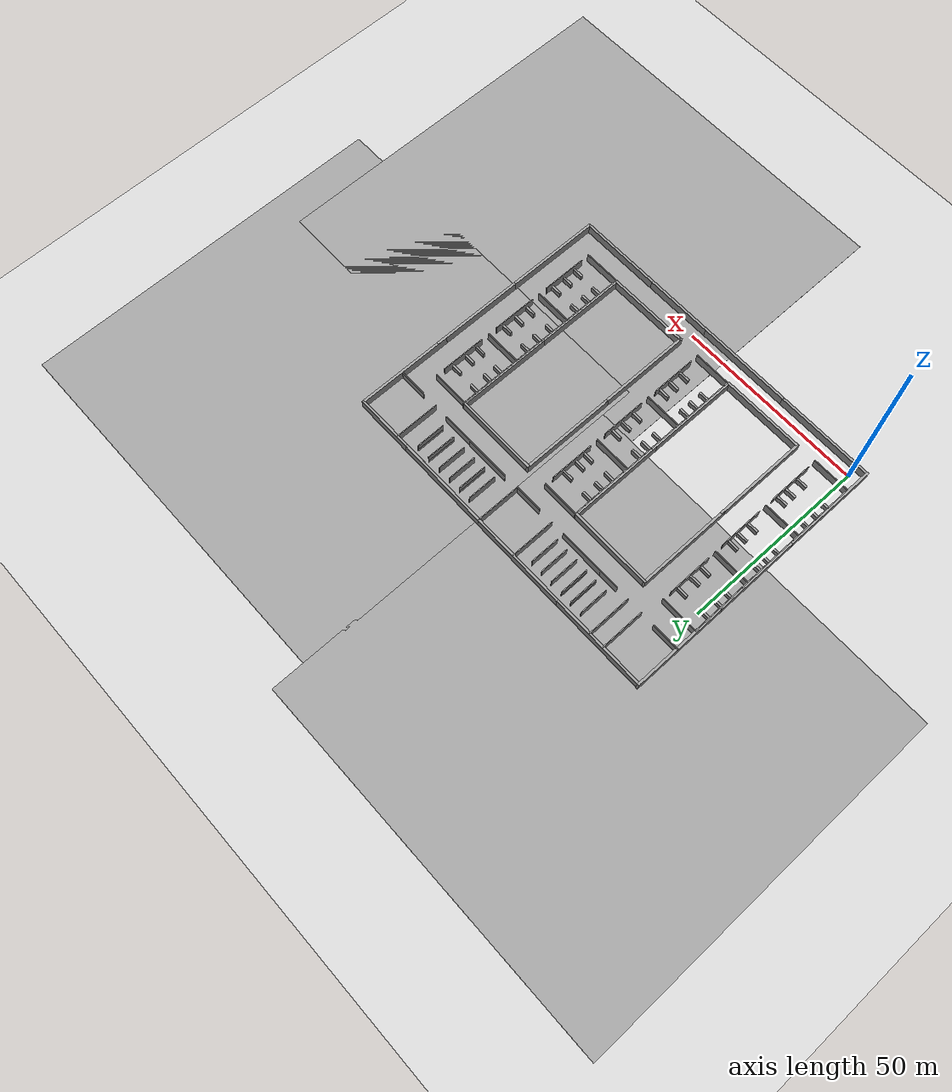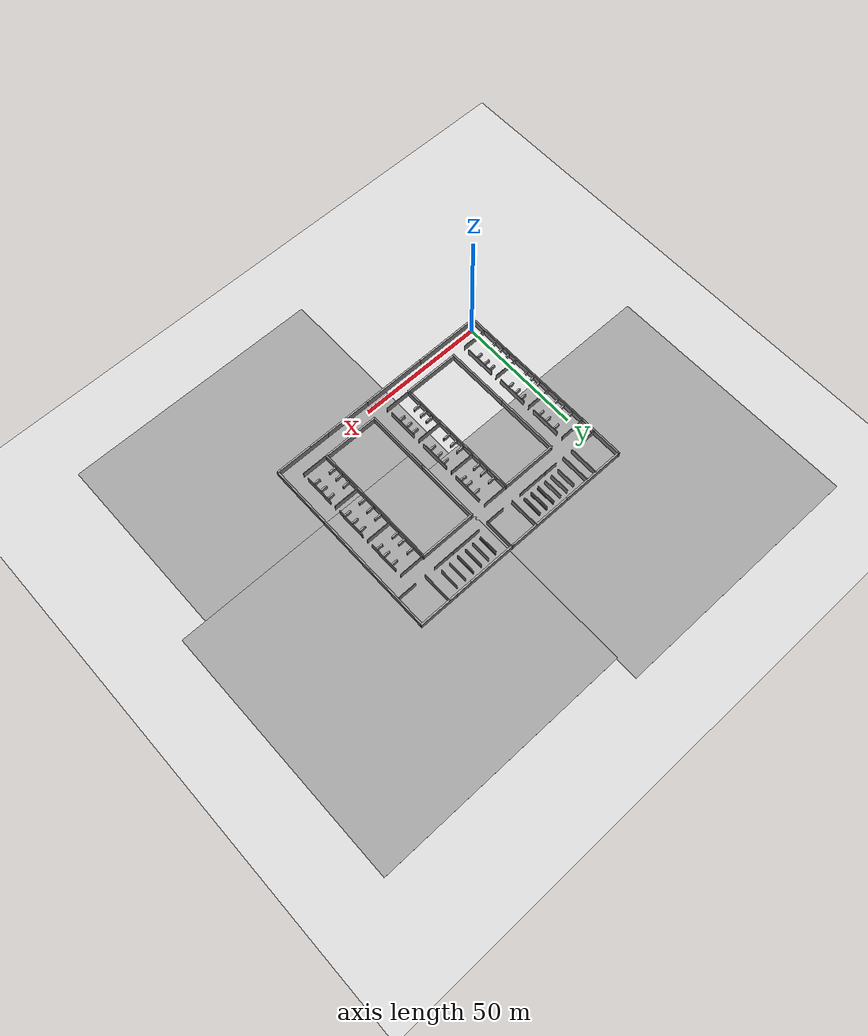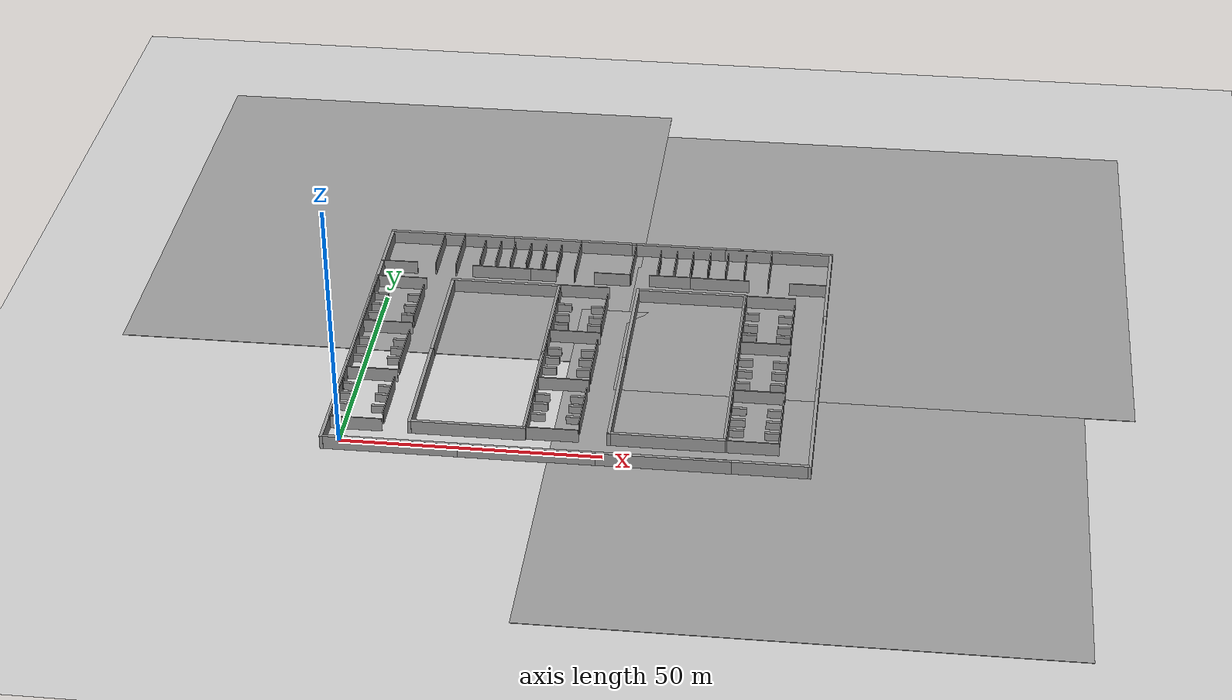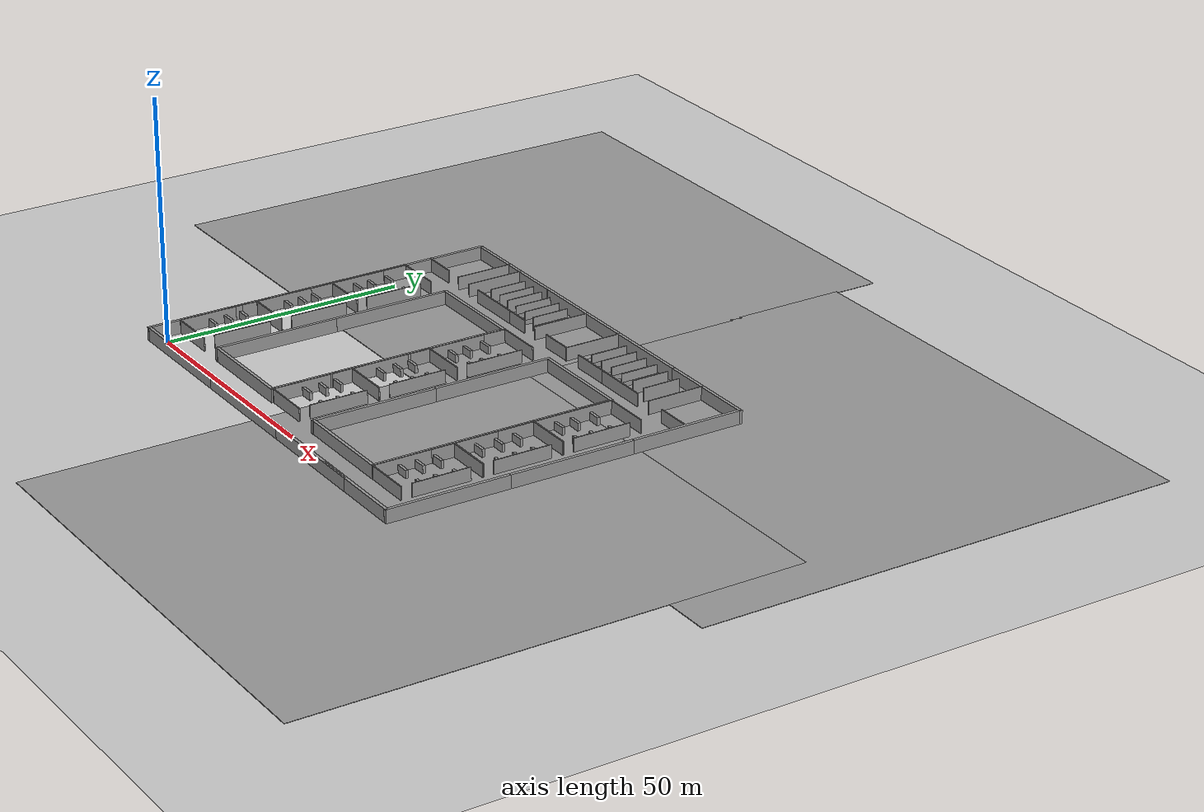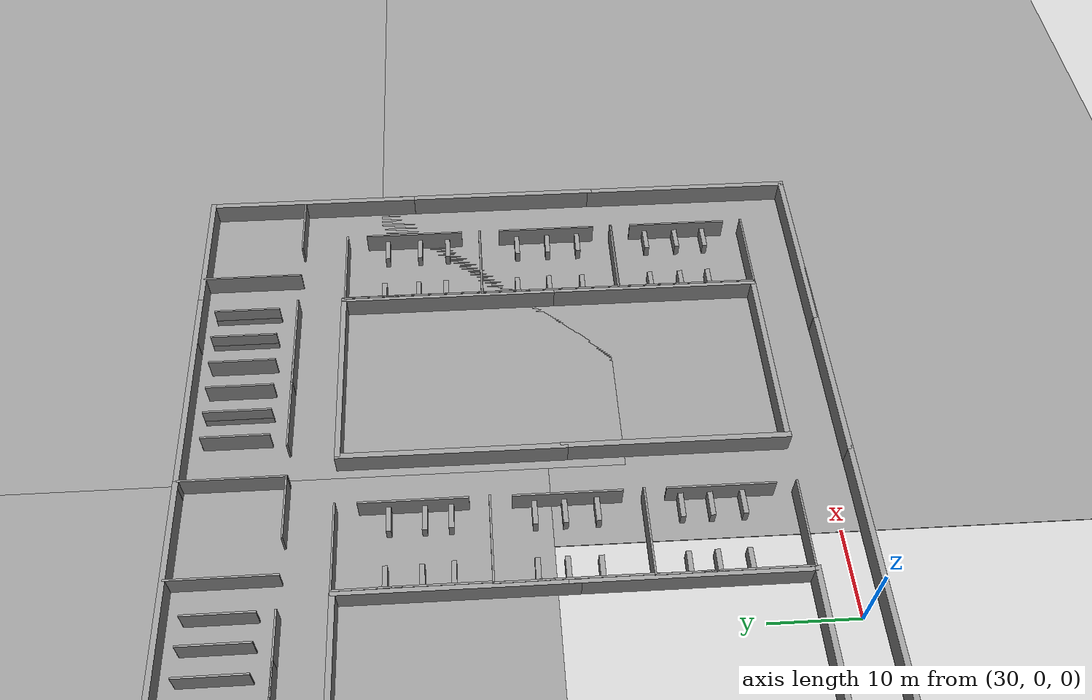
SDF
<sdf version="1.7">
 <world name="default">
  <light name="sun" type="directional">
   <pose>0 0 10 0 -0 0</pose>
   <diffuse>0.8 0.8 0.8 1</diffuse>
   <specular>0.2 0.2 0.2 1</specular>
   <attenuation>
    <range>1000</range>
    <constant>0.9</constant>
    <linear>0.01</linear>
    <quadratic>0.001</quadratic>
   </attenuation>
   <direction>-0.5 0.1 -0.9</direction>
   <spot><inner_angle>0</inner_angle><outer_angle>0</outer_angle><falloff>0</falloff></spot>
  </light>
  <plugin name="ros_interface_plugin" filename="librotors_gazebo_ros_interface_plugin.so"/>
  <model name="ground_plane">
   <static>1</static>
   <link name="link">
    <collision name="collision">
     <geometry><plane><normal>0 0 1</normal><size>100 100</size></plane></geometry>
     <surface><friction><ode><mu>100</mu><mu2>50</mu2></ode></friction></surface>
    </collision>
    <visual name="visual">
     <cast_shadows>0</cast_shadows>
     <geometry><plane><normal>0 0 1</normal><size>100 100</size></plane></geometry>
     <material>
      <script><uri>file://media/materials/scripts/gazebo.material</uri><name>Gazebo/Grey</name></script>
     </material>
    </visual>
   </link>
  </model>
  <gravity>0 0 -9.8</gravity>
  <magnetic_field>6e-06 2.3e-05 -4.2e-05</magnetic_field>
  <atmosphere type="adiabatic"/>
  <physics name="default_physics" default="0" type="ode">
   <max_step_size>0.001</max_step_size>
   <real_time_factor>1</real_time_factor>
   <real_time_update_rate>1000</real_time_update_rate>
  </physics>
  <scene><ambient>0.4 0.4 0.4 1</ambient><background>0.7 0.7 0.7 1</background><shadows>1</shadows></scene>
  <spherical_coordinates>
   <surface_model>EARTH_WGS84</surface_model>
   <latitude_deg>0</latitude_deg>
   <longitude_deg>0</longitude_deg>
   <elevation>0</elevation>
   <heading_deg>0</heading_deg>
  </spherical_coordinates>
  <model name="grey_wall_long">
   <link name="link">
    <pose>0 0 1.37589 0 -0 0</pose>
    <inertial>
     <inertia><ixx>0</ixx><ixy>0</ixy><ixz>0</ixz><iyy>0</iyy><iyz>0</iyz><izz>0</izz></inertia>
     <mass>0</mass>
    </inertial>
    <visual name="visual">
     <cast_shadows>0</cast_shadows>
     <geometry><box><size>25.8815 0.642976 2.8</size></box></geometry>
     <material>
      <script>
       <uri>model://grey_wall/materials/scripts</uri>
       <uri>model://grey_wall/materials/textures</uri>
       <name>vrc/grey_wall</name>
      </script>
      <shader type="pixel"><normal_map>__default__</normal_map></shader>
      <ambient>1 1 1 1</ambient>
      <diffuse>1 1 1 1</diffuse>
      <specular>0 0 0 1</specular>
      <emissive>0 0 0 1</emissive>
     </material>
    </visual>
    <collision name="collision">
     <geometry><box><size>25.8815 0.642976 2.8</size></box></geometry>
     <surface>
      <friction>
       <ode><mu>1</mu><mu2>1</mu2><fdir1>0 0 0</fdir1><slip1>0</slip1><slip2>0</slip2></ode>
       <torsional>
        <coefficient>1</coefficient>
        <patch_radius>0</patch_radius>
        <surface_radius>0</surface_radius>
        <use_patch_radius>1</use_patch_radius>
        <ode><slip>0</slip></ode>
       </torsional>
      </friction>
      <bounce><restitution_coefficient>0</restitution_coefficient><threshold>1e+06</threshold></bounce>
      <contact>
       <collide_without_contact>0</collide_without_contact>
       <collide_without_contact_bitmask>1</collide_without_contact_bitmask>
       <collide_bitmask>1</collide_bitmask>
       <ode>
        <soft_cfm>0</soft_cfm>
        <soft_erp>0.2</soft_erp>
        <kp>1e+13</kp>
        <kd>1</kd>
        <max_vel>0.01</max_vel>
        <min_depth>0</min_depth>
       </ode>
       <bullet>
        <split_impulse>1</split_impulse>
        <split_impulse_penetration_threshold>-0.01</split_impulse_penetration_threshold>
        <soft_cfm>0</soft_cfm>
        <soft_erp>0.2</soft_erp>
        <kp>1e+13</kp>
        <kd>1</kd>
       </bullet>
      </contact>
     </surface>
    </collision>
   </link>
   <static>1</static>
   <pose>10.3524 -2.38269 0 0 -0 0</pose>
  </model>
  <model name="grew_wall_long_vertial">
   <model name="grey_wall_long">
    <link name="link">
     <pose>0 0 1.37589 0 -0 0</pose>
     <inertial>
      <inertia><ixx>0</ixx><ixy>0</ixy><ixz>0</ixz><iyy>0</iyy><iyz>0</iyz><izz>0</izz></inertia>
      <mass>0</mass>
     </inertial>
     <visual name="visual">
      <cast_shadows>0</cast_shadows>
      <geometry><box><size>25.8815 0.642976 2.8</size></box></geometry>
      <material>
       <script>
        <uri>model://grey_wall/materials/scripts</uri>
        <uri>model://grey_wall/materials/textures</uri>
        <name>vrc/grey_wall</name>
       </script>
       <shader type="pixel"><normal_map>__default__</normal_map></shader>
       <ambient>1 1 1 1</ambient>
       <diffuse>1 1 1 1</diffuse>
       <specular>0 0 0 1</specular>
       <emissive>0 0 0 1</emissive>
      </material>
     </visual>
     <collision name="collision">
      <geometry><box><size>25.8815 0.642976 2.8</size></box></geometry>
      <surface>
       <friction>
        <ode><mu>1</mu><mu2>1</mu2><fdir1>0 0 0</fdir1><slip1>0</slip1><slip2>0</slip2></ode>
        <torsional>
         <coefficient>1</coefficient>
         <patch_radius>0</patch_radius>
         <surface_radius>0</surface_radius>
         <use_patch_radius>1</use_patch_radius>
         <ode><slip>0</slip></ode>
        </torsional>
       </friction>
       <bounce><restitution_coefficient>0</restitution_coefficient><threshold>1e+06</threshold></bounce>
       <contact>
        <collide_without_contact>0</collide_without_contact>
        <collide_without_contact_bitmask>1</collide_without_contact_bitmask>
        <collide_bitmask>1</collide_bitmask>
        <ode>
         <soft_cfm>0</soft_cfm>
         <soft_erp>0.2</soft_erp>
         <kp>1e+13</kp>
         <kd>1</kd>
         <max_vel>0.01</max_vel>
         <min_depth>0</min_depth>
        </ode>
        <bullet>
         <split_impulse>1</split_impulse>
         <split_impulse_penetration_threshold>-0.01</split_impulse_penetration_threshold>
         <soft_cfm>0</soft_cfm>
         <soft_erp>0.2</soft_erp>
         <kp>1e+13</kp>
         <kd>1</kd>
        </bullet>
       </contact>
      </surface>
     </collision>
    </link>
    <static>1</static>
    <pose>1e-06 -0 0 0 -0 1.57003</pose>
   </model>
   <static>0</static>
   <pose>-2.8099 10.2266 0 0 -0 0</pose>
  </model>
  <model name="grew_wall_long_vertial_0">
   <model name="grey_wall_long">
    <link name="link">
     <pose>0 0 1.37589 0 -0 0</pose>
     <inertial>
      <inertia><ixx>0</ixx><ixy>0</ixy><ixz>0</ixz><iyy>0</iyy><iyz>0</iyz><izz>0</izz></inertia>
      <mass>0</mass>
     </inertial>
     <visual name="visual">
      <cast_shadows>0</cast_shadows>
      <geometry><box><size>25.8815 0.642976 2.8</size></box></geometry>
      <material>
       <script>
        <uri>model://grey_wall/materials/scripts</uri>
        <uri>model://grey_wall/materials/textures</uri>
        <name>vrc/grey_wall</name>
       </script>
       <shader type="pixel"><normal_map>__default__</normal_map></shader>
       <ambient>1 1 1 1</ambient>
       <diffuse>1 1 1 1</diffuse>
       <specular>0 0 0 1</specular>
       <emissive>0 0 0 1</emissive>
      </material>
     </visual>
     <collision name="collision">
      <geometry><box><size>25.8815 0.642976 2.8</size></box></geometry>
      <surface>
       <friction>
        <ode><mu>1</mu><mu2>1</mu2><fdir1>0 0 0</fdir1><slip1>0</slip1><slip2>0</slip2></ode>
        <torsional>
         <coefficient>1</coefficient>
         <patch_radius>0</patch_radius>
         <surface_radius>0</surface_radius>
         <use_patch_radius>1</use_patch_radius>
         <ode><slip>0</slip></ode>
        </torsional>
       </friction>
       <bounce><restitution_coefficient>0</restitution_coefficient><threshold>1e+06</threshold></bounce>
       <contact>
        <collide_without_contact>0</collide_without_contact>
        <collide_without_contact_bitmask>1</collide_without_contact_bitmask>
        <collide_bitmask>1</collide_bitmask>
        <ode>
         <soft_cfm>0</soft_cfm>
         <soft_erp>0.2</soft_erp>
         <kp>1e+13</kp>
         <kd>1</kd>
         <max_vel>0.01</max_vel>
         <min_depth>0</min_depth>
        </ode>
        <bullet>
         <split_impulse>1</split_impulse>
         <split_impulse_penetration_threshold>-0.01</split_impulse_penetration_threshold>
         <soft_cfm>0</soft_cfm>
         <soft_erp>0.2</soft_erp>
         <kp>1e+13</kp>
         <kd>1</kd>
        </bullet>
       </contact>
      </surface>
     </collision>
    </link>
    <static>1</static>
    <pose>1e-06 -0 0 0 -0 1.57003</pose>
   </model>
   <static>0</static>
   <pose>-2.79602 36.045 0 0 -0 0</pose>
  </model>
  <model name="grey_wall_long_0">
   <link name="link">
    <pose>0 0 1.37589 0 -0 0</pose>
    <inertial>
     <inertia><ixx>0</ixx><ixy>0</ixy><ixz>0</ixz><iyy>0</iyy><iyz>0</iyz><izz>0</izz></inertia>
     <mass>0</mass>
    </inertial>
    <visual name="visual">
     <cast_shadows>0</cast_shadows>
     <geometry><box><size>25.8815 0.642976 2.8</size></box></geometry>
     <material>
      <script>
       <uri>model://grey_wall/materials/scripts</uri>
       <uri>model://grey_wall/materials/textures</uri>
       <name>vrc/grey_wall</name>
      </script>
      <shader type="pixel"><normal_map>__default__</normal_map></shader>
      <ambient>1 1 1 1</ambient>
      <diffuse>1 1 1 1</diffuse>
      <specular>0 0 0 1</specular>
      <emissive>0 0 0 1</emissive>
     </material>
    </visual>
    <collision name="collision">
     <geometry><box><size>25.8815 0.642976 2.8</size></box></geometry>
     <surface>
      <friction>
       <ode><mu>1</mu><mu2>1</mu2><fdir1>0 0 0</fdir1><slip1>0</slip1><slip2>0</slip2></ode>
       <torsional>
        <coefficient>1</coefficient>
        <patch_radius>0</patch_radius>
        <surface_radius>0</surface_radius>
        <use_patch_radius>1</use_patch_radius>
        <ode><slip>0</slip></ode>
       </torsional>
      </friction>
      <bounce><restitution_coefficient>0</restitution_coefficient><threshold>1e+06</threshold></bounce>
      <contact>
       <collide_without_contact>0</collide_without_contact>
       <collide_without_contact_bitmask>1</collide_without_contact_bitmask>
       <collide_bitmask>1</collide_bitmask>
       <ode>
        <soft_cfm>0</soft_cfm>
        <soft_erp>0.2</soft_erp>
        <kp>1e+13</kp>
        <kd>1</kd>
        <max_vel>0.01</max_vel>
        <min_depth>0</min_depth>
       </ode>
       <bullet>
        <split_impulse>1</split_impulse>
        <split_impulse_penetration_threshold>-0.01</split_impulse_penetration_threshold>
        <soft_cfm>0</soft_cfm>
        <soft_erp>0.2</soft_erp>
        <kp>1e+13</kp>
        <kd>1</kd>
       </bullet>
      </contact>
     </surface>
    </collision>
   </link>
   <static>1</static>
   <pose>35.9605 -2.39418 0 0 -0 0</pose>
  </model>
  <model name="grey_wall_long_1">
   <link name="link">
    <pose>0 0 1.37589 0 -0 0</pose>
    <inertial>
     <inertia><ixx>0</ixx><ixy>0</ixy><ixz>0</ixz><iyy>0</iyy><iyz>0</iyz><izz>0</izz></inertia>
     <mass>0</mass>
    </inertial>
    <visual name="visual">
     <cast_shadows>0</cast_shadows>
     <geometry><box><size>25.8815 0.642976 2.8</size></box></geometry>
     <material>
      <script>
       <uri>model://grey_wall/materials/scripts</uri>
       <uri>model://grey_wall/materials/textures</uri>
       <name>vrc/grey_wall</name>
      </script>
      <shader type="pixel"><normal_map>__default__</normal_map></shader>
      <ambient>1 1 1 1</ambient>
      <diffuse>1 1 1 1</diffuse>
      <specular>0 0 0 1</specular>
      <emissive>0 0 0 1</emissive>
     </material>
    </visual>
    <collision name="collision">
     <geometry><box><size>25.8815 0.642976 2.8</size></box></geometry>
     <surface>
      <friction>
       <ode><mu>1</mu><mu2>1</mu2><fdir1>0 0 0</fdir1><slip1>0</slip1><slip2>0</slip2></ode>
       <torsional>
        <coefficient>1</coefficient>
        <patch_radius>0</patch_radius>
        <surface_radius>0</surface_radius>
        <use_patch_radius>1</use_patch_radius>
        <ode><slip>0</slip></ode>
       </torsional>
      </friction>
      <bounce><restitution_coefficient>0</restitution_coefficient><threshold>1e+06</threshold></bounce>
      <contact>
       <collide_without_contact>0</collide_without_contact>
       <collide_without_contact_bitmask>1</collide_without_contact_bitmask>
       <collide_bitmask>1</collide_bitmask>
       <ode>
        <soft_cfm>0</soft_cfm>
        <soft_erp>0.2</soft_erp>
        <kp>1e+13</kp>
        <kd>1</kd>
        <max_vel>0.01</max_vel>
        <min_depth>0</min_depth>
       </ode>
       <bullet>
        <split_impulse>1</split_impulse>
        <split_impulse_penetration_threshold>-0.01</split_impulse_penetration_threshold>
        <soft_cfm>0</soft_cfm>
        <soft_erp>0.2</soft_erp>
        <kp>1e+13</kp>
        <kd>1</kd>
       </bullet>
      </contact>
     </surface>
    </collision>
   </link>
   <static>1</static>
   <pose>61.3257 -2.37865 0 0 -0 0</pose>
  </model>
  <model name="jiaoshi">
   <model name="grey_wall">
    <static>1</static>
    <link name="link">
     <pose>0 0 1.4 0 -0 0</pose>
     <collision name="collision"><geometry><box><size>7.5 0.2 2.8</size></box></geometry></collision>
     <visual name="visual">
      <cast_shadows>0</cast_shadows>
      <geometry><box><size>7.5 0.2 2.8</size></box></geometry>
      <material>
       <script>
        <uri>model://grey_wall/materials/scripts</uri>
        <uri>model://grey_wall/materials/textures</uri>
        <name>vrc/grey_wall</name>
       </script>
      </material>
     </visual>
    </link>
    <pose>-3.38172 4.2623 0 0 0 -1.56473</pose>
   </model>
   <model name="grey_wall_10m">
    <link name="link">
     <pose>1.25079 -0.023082 1.4 0 -0 0</pose>
     <inertial>
      <inertia><ixx>0</ixx><ixy>0</ixy><ixz>0</ixz><iyy>0</iyy><iyz>0</iyz><izz>0</izz></inertia>
      <mass>0</mass>
     </inertial>
     <visual name="visual">
      <cast_shadows>0</cast_shadows>
      <geometry><box><size>10.0157 0.2 2.8</size></box></geometry>
      <material>
       <script>
        <uri>model://grey_wall/materials/scripts</uri>
        <uri>model://grey_wall/materials/textures</uri>
        <name>vrc/grey_wall</name>
       </script>
       <shader type="pixel"/>
       <ambient>1 1 1 1</ambient>
       <diffuse>1 1 1 1</diffuse>
       <specular>0 0 0 1</specular>
       <emissive>0 0 0 1</emissive>
      </material>
     </visual>
     <collision name="collision">
      <geometry><box><size>10.0157 0.2 2.8</size></box></geometry>
      <surface>
       <friction>
        <ode><mu>1</mu><mu2>1</mu2><fdir1>0 0 0</fdir1><slip1>0</slip1><slip2>0</slip2></ode>
        <torsional>
         <coefficient>1</coefficient>
         <patch_radius>0</patch_radius>
         <surface_radius>0</surface_radius>
         <use_patch_radius>1</use_patch_radius>
         <ode><slip>0</slip></ode>
        </torsional>
       </friction>
       <bounce><restitution_coefficient>0</restitution_coefficient><threshold>1e+06</threshold></bounce>
       <contact>
        <collide_without_contact>0</collide_without_contact>
        <collide_without_contact_bitmask>1</collide_without_contact_bitmask>
        <collide_bitmask>1</collide_bitmask>
        <ode>
         <soft_cfm>0</soft_cfm>
         <soft_erp>0.2</soft_erp>
         <kp>1e+13</kp>
         <kd>1</kd>
         <max_vel>0.01</max_vel>
         <min_depth>0</min_depth>
        </ode>
        <bullet>
         <split_impulse>1</split_impulse>
         <split_impulse_penetration_threshold>-0.01</split_impulse_penetration_threshold>
         <soft_cfm>0</soft_cfm>
         <soft_erp>0.2</soft_erp>
         <kp>1e+13</kp>
         <kd>1</kd>
        </bullet>
       </contact>
      </surface>
     </collision>
    </link>
    <static>1</static>
    <pose>0.433183 -8.77625 0 0 -0 0</pose>
   </model>
   <model name="grey_wall_10m_0">
    <link name="link">
     <pose>1.25079 -0.023082 1.4 0 -0 0</pose>
     <inertial>
      <inertia><ixx>0</ixx><ixy>0</ixy><ixz>0</ixz><iyy>0</iyy><iyz>0</iyz><izz>0</izz></inertia>
      <mass>0</mass>
     </inertial>
     <visual name="visual">
      <cast_shadows>0</cast_shadows>
      <geometry><box><size>10.0157 0.2 2.8</size></box></geometry>
      <material>
       <script>
        <uri>model://grey_wall/materials/scripts</uri>
        <uri>model://grey_wall/materials/textures</uri>
        <name>vrc/grey_wall</name>
       </script>
       <shader type="pixel"/>
       <ambient>1 1 1 1</ambient>
       <diffuse>1 1 1 1</diffuse>
       <specular>0 0 0 1</specular>
       <emissive>0 0 0 1</emissive>
      </material>
     </visual>
     <collision name="collision">
      <geometry><box><size>10.0157 0.2 2.8</size></box></geometry>
      <surface>
       <friction>
        <ode><mu>1</mu><mu2>1</mu2><fdir1>0 0 0</fdir1><slip1>0</slip1><slip2>0</slip2></ode>
        <torsional>
         <coefficient>1</coefficient>
         <patch_radius>0</patch_radius>
         <surface_radius>0</surface_radius>
         <use_patch_radius>1</use_patch_radius>
         <ode><slip>0</slip></ode>
        </torsional>
       </friction>
       <bounce><restitution_coefficient>0</restitution_coefficient><threshold>1e+06</threshold></bounce>
       <contact>
        <collide_without_contact>0</collide_without_contact>
        <collide_without_contact_bitmask>1</collide_without_contact_bitmask>
        <collide_bitmask>1</collide_bitmask>
        <ode>
         <soft_cfm>0</soft_cfm>
         <soft_erp>0.2</soft_erp>
         <kp>1e+13</kp>
         <kd>1</kd>
         <max_vel>0.01</max_vel>
         <min_depth>0</min_depth>
        </ode>
        <bullet>
         <split_impulse>1</split_impulse>
         <split_impulse_penetration_threshold>-0.01</split_impulse_penetration_threshold>
         <soft_cfm>0</soft_cfm>
         <soft_erp>0.2</soft_erp>
         <kp>1e+13</kp>
         <kd>1</kd>
        </bullet>
       </contact>
      </surface>
     </collision>
    </link>
    <static>1</static>
    <pose>0.377364 7.92573 0 0 -0 0</pose>
   </model>
   <model name="grey_wall_12m_vertial">
    <link name="link">
     <pose>0.289112 -0.003891 1.4 0 0 -1.5701</pose>
     <inertial>
      <inertia><ixx>0</ixx><ixy>0</ixy><ixz>0</ixz><iyy>0</iyy><iyz>0</iyz><izz>0</izz></inertia>
      <mass>0</mass>
     </inertial>
     <visual name="visual">
      <cast_shadows>0</cast_shadows>
      <geometry><box><size>12.0527 0.2 2.8</size></box></geometry>
      <material>
       <script>
        <uri>model://grey_wall/materials/scripts</uri>
        <uri>model://grey_wall/materials/textures</uri>
        <name>vrc/grey_wall</name>
       </script>
       <shader type="pixel"/>
       <ambient>1 1 1 1</ambient>
       <diffuse>1 1 1 1</diffuse>
       <specular>0 0 0 1</specular>
       <emissive>0 0 0 1</emissive>
      </material>
     </visual>
     <collision name="collision">
      <geometry><box><size>12.0527 0.2 2.8</size></box></geometry>
      <surface>
       <friction>
        <ode><mu>1</mu><mu2>1</mu2><fdir1>0 0 0</fdir1><slip1>0</slip1><slip2>0</slip2></ode>
        <torsional>
         <coefficient>1</coefficient>
         <patch_radius>0</patch_radius>
         <surface_radius>0</surface_radius>
         <use_patch_radius>1</use_patch_radius>
         <ode><slip>0</slip></ode>
        </torsional>
       </friction>
       <bounce><restitution_coefficient>0</restitution_coefficient><threshold>1e+06</threshold></bounce>
       <contact>
        <collide_without_contact>0</collide_without_contact>
        <collide_without_contact_bitmask>1</collide_without_contact_bitmask>
        <collide_bitmask>1</collide_bitmask>
        <ode>
         <soft_cfm>0</soft_cfm>
         <soft_erp>0.2</soft_erp>
         <kp>1e+13</kp>
         <kd>1</kd>
         <max_vel>0.01</max_vel>
         <min_depth>0</min_depth>
        </ode>
        <bullet>
         <split_impulse>1</split_impulse>
         <split_impulse_penetration_threshold>-0.01</split_impulse_penetration_threshold>
         <soft_cfm>0</soft_cfm>
         <soft_erp>0.2</soft_erp>
         <kp>1e+13</kp>
         <kd>1</kd>
        </bullet>
       </contact>
      </surface>
     </collision>
    </link>
    <static>1</static>
    <pose>-3.63668 -2.87268 0 0 -0 0</pose>
   </model>
   <model name="grey_wall_12m_vertial_0">
    <link name="link">
     <pose>0.289112 -0.003891 1.4 0 0 -1.5701</pose>
     <inertial>
      <inertia><ixx>0</ixx><ixy>0</ixy><ixz>0</ixz><iyy>0</iyy><iyz>0</iyz><izz>0</izz></inertia>
      <mass>0</mass>
     </inertial>
     <visual name="visual">
      <cast_shadows>0</cast_shadows>
      <geometry><box><size>12.0527 0.2 2.8</size></box></geometry>
      <material>
       <script>
        <uri>model://grey_wall/materials/scripts</uri>
        <uri>model://grey_wall/materials/textures</uri>
        <name>vrc/grey_wall</name>
       </script>
       <shader type="pixel"/>
       <ambient>1 1 1 1</ambient>
       <diffuse>1 1 1 1</diffuse>
       <specular>0 0 0 1</specular>
       <emissive>0 0 0 1</emissive>
      </material>
     </visual>
     <collision name="collision">
      <geometry><box><size>12.0527 0.2 2.8</size></box></geometry>
      <surface>
       <friction>
        <ode><mu>1</mu><mu2>1</mu2><fdir1>0 0 0</fdir1><slip1>0</slip1><slip2>0</slip2></ode>
        <torsional>
         <coefficient>1</coefficient>
         <patch_radius>0</patch_radius>
         <surface_radius>0</surface_radius>
         <use_patch_radius>1</use_patch_radius>
         <ode><slip>0</slip></ode>
        </torsional>
       </friction>
       <bounce><restitution_coefficient>0</restitution_coefficient><threshold>1e+06</threshold></bounce>
       <contact>
        <collide_without_contact>0</collide_without_contact>
        <collide_without_contact_bitmask>1</collide_without_contact_bitmask>
        <collide_bitmask>1</collide_bitmask>
        <ode>
         <soft_cfm>0</soft_cfm>
         <soft_erp>0.2</soft_erp>
         <kp>1e+13</kp>
         <kd>1</kd>
         <max_vel>0.01</max_vel>
         <min_depth>0</min_depth>
        </ode>
        <bullet>
         <split_impulse>1</split_impulse>
         <split_impulse_penetration_threshold>-0.01</split_impulse_penetration_threshold>
         <soft_cfm>0</soft_cfm>
         <soft_erp>0.2</soft_erp>
         <kp>1e+13</kp>
         <kd>1</kd>
        </bullet>
       </contact>
      </surface>
     </collision>
    </link>
    <static>1</static>
    <pose>6.20786 -0.539083 0 0 -0 0</pose>
   </model>
   <static>0</static>
   <pose>0.80037 12.8654 0 0 -0 0</pose>
  </model>
  <model name="jiaoshi_clone">
   <model name="grey_wall">
    <static>1</static>
    <link name="link">
     <pose>0 0 1.4 0 -0 0</pose>
     <collision name="collision"><geometry><box><size>7.5 0.2 2.8</size></box></geometry></collision>
     <visual name="visual">
      <cast_shadows>0</cast_shadows>
      <geometry><box><size>7.5 0.2 2.8</size></box></geometry>
      <material>
       <script>
        <uri>model://grey_wall/materials/scripts</uri>
        <uri>model://grey_wall/materials/textures</uri>
        <name>vrc/grey_wall</name>
       </script>
      </material>
     </visual>
    </link>
    <pose>-3.38172 4.2623 0 0 0 -1.56473</pose>
   </model>
   <model name="grey_wall_10m">
    <link name="link">
     <pose>1.25079 -0.023082 1.4 0 -0 0</pose>
     <inertial>
      <inertia><ixx>0</ixx><ixy>0</ixy><ixz>0</ixz><iyy>0</iyy><iyz>0</iyz><izz>0</izz></inertia>
      <mass>0</mass>
     </inertial>
     <visual name="visual">
      <cast_shadows>0</cast_shadows>
      <geometry><box><size>10.0157 0.2 2.8</size></box></geometry>
      <material>
       <script>
        <uri>model://grey_wall/materials/scripts</uri>
        <uri>model://grey_wall/materials/textures</uri>
        <name>vrc/grey_wall</name>
       </script>
       <shader type="pixel"/>
       <ambient>1 1 1 1</ambient>
       <diffuse>1 1 1 1</diffuse>
       <specular>0 0 0 1</specular>
       <emissive>0 0 0 1</emissive>
      </material>
     </visual>
     <collision name="collision">
      <geometry><box><size>10.0157 0.2 2.8</size></box></geometry>
      <surface>
       <friction>
        <ode><mu>1</mu><mu2>1</mu2><fdir1>0 0 0</fdir1><slip1>0</slip1><slip2>0</slip2></ode>
        <torsional>
         <coefficient>1</coefficient>
         <patch_radius>0</patch_radius>
         <surface_radius>0</surface_radius>
         <use_patch_radius>1</use_patch_radius>
         <ode><slip>0</slip></ode>
        </torsional>
       </friction>
       <bounce><restitution_coefficient>0</restitution_coefficient><threshold>1e+06</threshold></bounce>
       <contact>
        <collide_without_contact>0</collide_without_contact>
        <collide_without_contact_bitmask>1</collide_without_contact_bitmask>
        <collide_bitmask>1</collide_bitmask>
        <ode>
         <soft_cfm>0</soft_cfm>
         <soft_erp>0.2</soft_erp>
         <kp>1e+13</kp>
         <kd>1</kd>
         <max_vel>0.01</max_vel>
         <min_depth>0</min_depth>
        </ode>
        <bullet>
         <split_impulse>1</split_impulse>
         <split_impulse_penetration_threshold>-0.01</split_impulse_penetration_threshold>
         <soft_cfm>0</soft_cfm>
         <soft_erp>0.2</soft_erp>
         <kp>1e+13</kp>
         <kd>1</kd>
        </bullet>
       </contact>
      </surface>
     </collision>
    </link>
    <static>1</static>
    <pose>0.433183 -8.77625 0 0 -0 0</pose>
   </model>
   <model name="grey_wall_10m_0">
    <link name="link">
     <pose>1.25079 -0.023082 1.4 0 -0 0</pose>
     <inertial>
      <inertia><ixx>0</ixx><ixy>0</ixy><ixz>0</ixz><iyy>0</iyy><iyz>0</iyz><izz>0</izz></inertia>
      <mass>0</mass>
     </inertial>
     <visual name="visual">
      <cast_shadows>0</cast_shadows>
      <geometry><box><size>10.0157 0.2 2.8</size></box></geometry>
      <material>
       <script>
        <uri>model://grey_wall/materials/scripts</uri>
        <uri>model://grey_wall/materials/textures</uri>
        <name>vrc/grey_wall</name>
       </script>
       <shader type="pixel"/>
       <ambient>1 1 1 1</ambient>
       <diffuse>1 1 1 1</diffuse>
       <specular>0 0 0 1</specular>
       <emissive>0 0 0 1</emissive>
      </material>
     </visual>
     <collision name="collision">
      <geometry><box><size>10.0157 0.2 2.8</size></box></geometry>
      <surface>
       <friction>
        <ode><mu>1</mu><mu2>1</mu2><fdir1>0 0 0</fdir1><slip1>0</slip1><slip2>0</slip2></ode>
        <torsional>
         <coefficient>1</coefficient>
         <patch_radius>0</patch_radius>
         <surface_radius>0</surface_radius>
         <use_patch_radius>1</use_patch_radius>
         <ode><slip>0</slip></ode>
        </torsional>
       </friction>
       <bounce><restitution_coefficient>0</restitution_coefficient><threshold>1e+06</threshold></bounce>
       <contact>
        <collide_without_contact>0</collide_without_contact>
        <collide_without_contact_bitmask>1</collide_without_contact_bitmask>
        <collide_bitmask>1</collide_bitmask>
        <ode>
         <soft_cfm>0</soft_cfm>
         <soft_erp>0.2</soft_erp>
         <kp>1e+13</kp>
         <kd>1</kd>
         <max_vel>0.01</max_vel>
         <min_depth>0</min_depth>
        </ode>
        <bullet>
         <split_impulse>1</split_impulse>
         <split_impulse_penetration_threshold>-0.01</split_impulse_penetration_threshold>
         <soft_cfm>0</soft_cfm>
         <soft_erp>0.2</soft_erp>
         <kp>1e+13</kp>
         <kd>1</kd>
        </bullet>
       </contact>
      </surface>
     </collision>
    </link>
    <static>1</static>
    <pose>0.377364 7.92573 0 0 -0 0</pose>
   </model>
   <model name="grey_wall_12m_vertial">
    <link name="link">
     <pose>0.289112 -0.003891 1.4 0 0 -1.5701</pose>
     <inertial>
      <inertia><ixx>0</ixx><ixy>0</ixy><ixz>0</ixz><iyy>0</iyy><iyz>0</iyz><izz>0</izz></inertia>
      <mass>0</mass>
     </inertial>
     <visual name="visual">
      <cast_shadows>0</cast_shadows>
      <geometry><box><size>12.0527 0.2 2.8</size></box></geometry>
      <material>
       <script>
        <uri>model://grey_wall/materials/scripts</uri>
        <uri>model://grey_wall/materials/textures</uri>
        <name>vrc/grey_wall</name>
       </script>
       <shader type="pixel"/>
       <ambient>1 1 1 1</ambient>
       <diffuse>1 1 1 1</diffuse>
       <specular>0 0 0 1</specular>
       <emissive>0 0 0 1</emissive>
      </material>
     </visual>
     <collision name="collision">
      <geometry><box><size>12.0527 0.2 2.8</size></box></geometry>
      <surface>
       <friction>
        <ode><mu>1</mu><mu2>1</mu2><fdir1>0 0 0</fdir1><slip1>0</slip1><slip2>0</slip2></ode>
        <torsional>
         <coefficient>1</coefficient>
         <patch_radius>0</patch_radius>
         <surface_radius>0</surface_radius>
         <use_patch_radius>1</use_patch_radius>
         <ode><slip>0</slip></ode>
        </torsional>
       </friction>
       <bounce><restitution_coefficient>0</restitution_coefficient><threshold>1e+06</threshold></bounce>
       <contact>
        <collide_without_contact>0</collide_without_contact>
        <collide_without_contact_bitmask>1</collide_without_contact_bitmask>
        <collide_bitmask>1</collide_bitmask>
        <ode>
         <soft_cfm>0</soft_cfm>
         <soft_erp>0.2</soft_erp>
         <kp>1e+13</kp>
         <kd>1</kd>
         <max_vel>0.01</max_vel>
         <min_depth>0</min_depth>
        </ode>
        <bullet>
         <split_impulse>1</split_impulse>
         <split_impulse_penetration_threshold>-0.01</split_impulse_penetration_threshold>
         <soft_cfm>0</soft_cfm>
         <soft_erp>0.2</soft_erp>
         <kp>1e+13</kp>
         <kd>1</kd>
        </bullet>
       </contact>
      </surface>
     </collision>
    </link>
    <static>1</static>
    <pose>-3.63668 -2.87268 0 0 -0 0</pose>
   </model>
   <model name="grey_wall_12m_vertial_0">
    <link name="link">
     <pose>0.289112 -0.003891 1.4 0 0 -1.5701</pose>
     <inertial>
      <inertia><ixx>0</ixx><ixy>0</ixy><ixz>0</ixz><iyy>0</iyy><iyz>0</iyz><izz>0</izz></inertia>
      <mass>0</mass>
     </inertial>
     <visual name="visual">
      <cast_shadows>0</cast_shadows>
      <geometry><box><size>12.0527 0.2 2.8</size></box></geometry>
      <material>
       <script>
        <uri>model://grey_wall/materials/scripts</uri>
        <uri>model://grey_wall/materials/textures</uri>
        <name>vrc/grey_wall</name>
       </script>
       <shader type="pixel"/>
       <ambient>1 1 1 1</ambient>
       <diffuse>1 1 1 1</diffuse>
       <specular>0 0 0 1</specular>
       <emissive>0 0 0 1</emissive>
      </material>
     </visual>
     <collision name="collision">
      <geometry><box><size>12.0527 0.2 2.8</size></box></geometry>
      <surface>
       <friction>
        <ode><mu>1</mu><mu2>1</mu2><fdir1>0 0 0</fdir1><slip1>0</slip1><slip2>0</slip2></ode>
        <torsional>
         <coefficient>1</coefficient>
         <patch_radius>0</patch_radius>
         <surface_radius>0</surface_radius>
         <use_patch_radius>1</use_patch_radius>
         <ode><slip>0</slip></ode>
        </torsional>
       </friction>
       <bounce><restitution_coefficient>0</restitution_coefficient><threshold>1e+06</threshold></bounce>
       <contact>
        <collide_without_contact>0</collide_without_contact>
        <collide_without_contact_bitmask>1</collide_without_contact_bitmask>
        <collide_bitmask>1</collide_bitmask>
        <ode>
         <soft_cfm>0</soft_cfm>
         <soft_erp>0.2</soft_erp>
         <kp>1e+13</kp>
         <kd>1</kd>
         <max_vel>0.01</max_vel>
         <min_depth>0</min_depth>
        </ode>
        <bullet>
         <split_impulse>1</split_impulse>
         <split_impulse_penetration_threshold>-0.01</split_impulse_penetration_threshold>
         <soft_cfm>0</soft_cfm>
         <soft_erp>0.2</soft_erp>
         <kp>1e+13</kp>
         <kd>1</kd>
        </bullet>
       </contact>
      </surface>
     </collision>
    </link>
    <static>1</static>
    <pose>6.20786 -0.539083 0 0 -0 0</pose>
   </model>
   <static>0</static>
   <pose>0.77997 29.5098 0 0 -0 0</pose>
  </model>
  <model name="ground_plane_0">
   <static>1</static>
   <link name="link">
    <collision name="collision">
     <geometry><plane><normal>0 0 1</normal><size>100 100</size></plane></geometry>
     <surface><friction><ode><mu>100</mu><mu2>50</mu2></ode></friction></surface>
    </collision>
    <visual name="visual">
     <cast_shadows>0</cast_shadows>
     <geometry><plane><normal>0 0 1</normal><size>100 100</size></plane></geometry>
     <material>
      <script><uri>file://media/materials/scripts/gazebo.material</uri><name>Gazebo/Grey</name></script>
     </material>
    </visual>
   </link>
   <pose>-0.073857 81.0851 0 0 -0 0</pose>
  </model>
  <model name="ground_plane_1">
   <static>1</static>
   <link name="link">
    <collision name="collision">
     <geometry><plane><normal>0 0 1</normal><size>100 100</size></plane></geometry>
     <surface><friction><ode><mu>100</mu><mu2>50</mu2></ode></friction></surface>
    </collision>
    <visual name="visual">
     <cast_shadows>0</cast_shadows>
     <geometry><plane><normal>0 0 1</normal><size>100 100</size></plane></geometry>
     <material>
      <script><uri>file://media/materials/scripts/gazebo.material</uri><name>Gazebo/Grey</name></script>
     </material>
    </visual>
   </link>
   <pose>89.798 0.232818 0 0 -0 0</pose>
  </model>
  <model name="ground_plane_2">
   <static>1</static>
   <link name="link">
    <collision name="collision">
     <geometry><plane><normal>0 0 1</normal><size>100 100</size></plane></geometry>
     <surface><friction><ode><mu>100</mu><mu2>50</mu2></ode></friction></surface>
    </collision>
    <visual name="visual">
     <cast_shadows>0</cast_shadows>
     <geometry><plane><normal>0 0 1</normal><size>100 100</size></plane></geometry>
     <material>
      <script><uri>file://media/materials/scripts/gazebo.material</uri><name>Gazebo/Grey</name></script>
     </material>
    </visual>
   </link>
   <pose>99.3631 72.3911 0 0 -0 0</pose>
  </model>
  <model name="grew_wall_long_vertial_0_clone">
   <model name="grey_wall_long">
    <link name="link">
     <pose>0 0 1.37589 0 -0 0</pose>
     <inertial>
      <inertia><ixx>0</ixx><ixy>0</ixy><ixz>0</ixz><iyy>0</iyy><iyz>0</iyz><izz>0</izz></inertia>
      <mass>0</mass>
     </inertial>
     <visual name="visual">
      <cast_shadows>0</cast_shadows>
      <geometry><box><size>25.8815 0.642976 2.8</size></box></geometry>
      <material>
       <script>
        <uri>model://grey_wall/materials/scripts</uri>
        <uri>model://grey_wall/materials/textures</uri>
        <name>vrc/grey_wall</name>
       </script>
       <shader type="pixel"><normal_map>__default__</normal_map></shader>
       <ambient>1 1 1 1</ambient>
       <diffuse>1 1 1 1</diffuse>
       <specular>0 0 0 1</specular>
       <emissive>0 0 0 1</emissive>
      </material>
     </visual>
     <collision name="collision">
      <geometry><box><size>25.8815 0.642976 2.8</size></box></geometry>
      <surface>
       <friction>
        <ode><mu>1</mu><mu2>1</mu2><fdir1>0 0 0</fdir1><slip1>0</slip1><slip2>0</slip2></ode>
        <torsional>
         <coefficient>1</coefficient>
         <patch_radius>0</patch_radius>
         <surface_radius>0</surface_radius>
         <use_patch_radius>1</use_patch_radius>
         <ode><slip>0</slip></ode>
        </torsional>
       </friction>
       <bounce><restitution_coefficient>0</restitution_coefficient><threshold>1e+06</threshold></bounce>
       <contact>
        <collide_without_contact>0</collide_without_contact>
        <collide_without_contact_bitmask>1</collide_without_contact_bitmask>
        <collide_bitmask>1</collide_bitmask>
        <ode>
         <soft_cfm>0</soft_cfm>
         <soft_erp>0.2</soft_erp>
         <kp>1e+13</kp>
         <kd>1</kd>
         <max_vel>0.01</max_vel>
         <min_depth>0</min_depth>
        </ode>
        <bullet>
         <split_impulse>1</split_impulse>
         <split_impulse_penetration_threshold>-0.01</split_impulse_penetration_threshold>
         <soft_cfm>0</soft_cfm>
         <soft_erp>0.2</soft_erp>
         <kp>1e+13</kp>
         <kd>1</kd>
        </bullet>
       </contact>
      </surface>
     </collision>
    </link>
    <static>1</static>
    <pose>1e-06 -0 0 0 -0 1.57003</pose>
   </model>
   <static>0</static>
   <pose>-2.80084 59.1647 0 0 -0 0</pose>
  </model>
  <model name="jiaoshi_clone_clone">
   <model name="grey_wall">
    <static>1</static>
    <link name="link">
     <pose>0 0 1.4 0 -0 0</pose>
     <collision name="collision"><geometry><box><size>7.5 0.2 2.8</size></box></geometry></collision>
     <visual name="visual">
      <cast_shadows>0</cast_shadows>
      <geometry><box><size>7.5 0.2 2.8</size></box></geometry>
      <material>
       <script>
        <uri>model://grey_wall/materials/scripts</uri>
        <uri>model://grey_wall/materials/textures</uri>
        <name>vrc/grey_wall</name>
       </script>
      </material>
     </visual>
    </link>
    <pose>-3.38172 4.2623 0 0 0 -1.56473</pose>
   </model>
   <model name="grey_wall_10m">
    <link name="link">
     <pose>1.25079 -0.023082 1.4 0 -0 0</pose>
     <inertial>
      <inertia><ixx>0</ixx><ixy>0</ixy><ixz>0</ixz><iyy>0</iyy><iyz>0</iyz><izz>0</izz></inertia>
      <mass>0</mass>
     </inertial>
     <visual name="visual">
      <cast_shadows>0</cast_shadows>
      <geometry><box><size>10.0157 0.2 2.8</size></box></geometry>
      <material>
       <script>
        <uri>model://grey_wall/materials/scripts</uri>
        <uri>model://grey_wall/materials/textures</uri>
        <name>vrc/grey_wall</name>
       </script>
       <shader type="pixel"/>
       <ambient>1 1 1 1</ambient>
       <diffuse>1 1 1 1</diffuse>
       <specular>0 0 0 1</specular>
       <emissive>0 0 0 1</emissive>
      </material>
     </visual>
     <collision name="collision">
      <geometry><box><size>10.0157 0.2 2.8</size></box></geometry>
      <surface>
       <friction>
        <ode><mu>1</mu><mu2>1</mu2><fdir1>0 0 0</fdir1><slip1>0</slip1><slip2>0</slip2></ode>
        <torsional>
         <coefficient>1</coefficient>
         <patch_radius>0</patch_radius>
         <surface_radius>0</surface_radius>
         <use_patch_radius>1</use_patch_radius>
         <ode><slip>0</slip></ode>
        </torsional>
       </friction>
       <bounce><restitution_coefficient>0</restitution_coefficient><threshold>1e+06</threshold></bounce>
       <contact>
        <collide_without_contact>0</collide_without_contact>
        <collide_without_contact_bitmask>1</collide_without_contact_bitmask>
        <collide_bitmask>1</collide_bitmask>
        <ode>
         <soft_cfm>0</soft_cfm>
         <soft_erp>0.2</soft_erp>
         <kp>1e+13</kp>
         <kd>1</kd>
         <max_vel>0.01</max_vel>
         <min_depth>0</min_depth>
        </ode>
        <bullet>
         <split_impulse>1</split_impulse>
         <split_impulse_penetration_threshold>-0.01</split_impulse_penetration_threshold>
         <soft_cfm>0</soft_cfm>
         <soft_erp>0.2</soft_erp>
         <kp>1e+13</kp>
         <kd>1</kd>
        </bullet>
       </contact>
      </surface>
     </collision>
    </link>
    <static>1</static>
    <pose>0.433183 -8.77625 0 0 -0 0</pose>
   </model>
   <model name="grey_wall_10m_0">
    <link name="link">
     <pose>1.25079 -0.023082 1.4 0 -0 0</pose>
     <inertial>
      <inertia><ixx>0</ixx><ixy>0</ixy><ixz>0</ixz><iyy>0</iyy><iyz>0</iyz><izz>0</izz></inertia>
      <mass>0</mass>
     </inertial>
     <visual name="visual">
      <cast_shadows>0</cast_shadows>
      <geometry><box><size>10.0157 0.2 2.8</size></box></geometry>
      <material>
       <script>
        <uri>model://grey_wall/materials/scripts</uri>
        <uri>model://grey_wall/materials/textures</uri>
        <name>vrc/grey_wall</name>
       </script>
       <shader type="pixel"/>
       <ambient>1 1 1 1</ambient>
       <diffuse>1 1 1 1</diffuse>
       <specular>0 0 0 1</specular>
       <emissive>0 0 0 1</emissive>
      </material>
     </visual>
     <collision name="collision">
      <geometry><box><size>10.0157 0.2 2.8</size></box></geometry>
      <surface>
       <friction>
        <ode><mu>1</mu><mu2>1</mu2><fdir1>0 0 0</fdir1><slip1>0</slip1><slip2>0</slip2></ode>
        <torsional>
         <coefficient>1</coefficient>
         <patch_radius>0</patch_radius>
         <surface_radius>0</surface_radius>
         <use_patch_radius>1</use_patch_radius>
         <ode><slip>0</slip></ode>
        </torsional>
       </friction>
       <bounce><restitution_coefficient>0</restitution_coefficient><threshold>1e+06</threshold></bounce>
       <contact>
        <collide_without_contact>0</collide_without_contact>
        <collide_without_contact_bitmask>1</collide_without_contact_bitmask>
        <collide_bitmask>1</collide_bitmask>
        <ode>
         <soft_cfm>0</soft_cfm>
         <soft_erp>0.2</soft_erp>
         <kp>1e+13</kp>
         <kd>1</kd>
         <max_vel>0.01</max_vel>
         <min_depth>0</min_depth>
        </ode>
        <bullet>
         <split_impulse>1</split_impulse>
         <split_impulse_penetration_threshold>-0.01</split_impulse_penetration_threshold>
         <soft_cfm>0</soft_cfm>
         <soft_erp>0.2</soft_erp>
         <kp>1e+13</kp>
         <kd>1</kd>
        </bullet>
       </contact>
      </surface>
     </collision>
    </link>
    <static>1</static>
    <pose>0.377364 7.92573 0 0 -0 0</pose>
   </model>
   <model name="grey_wall_12m_vertial">
    <link name="link">
     <pose>0.289112 -0.003891 1.4 0 0 -1.5701</pose>
     <inertial>
      <inertia><ixx>0</ixx><ixy>0</ixy><ixz>0</ixz><iyy>0</iyy><iyz>0</iyz><izz>0</izz></inertia>
      <mass>0</mass>
     </inertial>
     <visual name="visual">
      <cast_shadows>0</cast_shadows>
      <geometry><box><size>12.0527 0.2 2.8</size></box></geometry>
      <material>
       <script>
        <uri>model://grey_wall/materials/scripts</uri>
        <uri>model://grey_wall/materials/textures</uri>
        <name>vrc/grey_wall</name>
       </script>
       <shader type="pixel"/>
       <ambient>1 1 1 1</ambient>
       <diffuse>1 1 1 1</diffuse>
       <specular>0 0 0 1</specular>
       <emissive>0 0 0 1</emissive>
      </material>
     </visual>
     <collision name="collision">
      <geometry><box><size>12.0527 0.2 2.8</size></box></geometry>
      <surface>
       <friction>
        <ode><mu>1</mu><mu2>1</mu2><fdir1>0 0 0</fdir1><slip1>0</slip1><slip2>0</slip2></ode>
        <torsional>
         <coefficient>1</coefficient>
         <patch_radius>0</patch_radius>
         <surface_radius>0</surface_radius>
         <use_patch_radius>1</use_patch_radius>
         <ode><slip>0</slip></ode>
        </torsional>
       </friction>
       <bounce><restitution_coefficient>0</restitution_coefficient><threshold>1e+06</threshold></bounce>
       <contact>
        <collide_without_contact>0</collide_without_contact>
        <collide_without_contact_bitmask>1</collide_without_contact_bitmask>
        <collide_bitmask>1</collide_bitmask>
        <ode>
         <soft_cfm>0</soft_cfm>
         <soft_erp>0.2</soft_erp>
         <kp>1e+13</kp>
         <kd>1</kd>
         <max_vel>0.01</max_vel>
         <min_depth>0</min_depth>
        </ode>
        <bullet>
         <split_impulse>1</split_impulse>
         <split_impulse_penetration_threshold>-0.01</split_impulse_penetration_threshold>
         <soft_cfm>0</soft_cfm>
         <soft_erp>0.2</soft_erp>
         <kp>1e+13</kp>
         <kd>1</kd>
        </bullet>
       </contact>
      </surface>
     </collision>
    </link>
    <static>1</static>
    <pose>-3.63668 -2.87268 0 0 -0 0</pose>
   </model>
   <model name="grey_wall_12m_vertial_0">
    <link name="link">
     <pose>0.289112 -0.003891 1.4 0 0 -1.5701</pose>
     <inertial>
      <inertia><ixx>0</ixx><ixy>0</ixy><ixz>0</ixz><iyy>0</iyy><iyz>0</iyz><izz>0</izz></inertia>
      <mass>0</mass>
     </inertial>
     <visual name="visual">
      <cast_shadows>0</cast_shadows>
      <geometry><box><size>12.0527 0.2 2.8</size></box></geometry>
      <material>
       <script>
        <uri>model://grey_wall/materials/scripts</uri>
        <uri>model://grey_wall/materials/textures</uri>
        <name>vrc/grey_wall</name>
       </script>
       <shader type="pixel"/>
       <ambient>1 1 1 1</ambient>
       <diffuse>1 1 1 1</diffuse>
       <specular>0 0 0 1</specular>
       <emissive>0 0 0 1</emissive>
      </material>
     </visual>
     <collision name="collision">
      <geometry><box><size>12.0527 0.2 2.8</size></box></geometry>
      <surface>
       <friction>
        <ode><mu>1</mu><mu2>1</mu2><fdir1>0 0 0</fdir1><slip1>0</slip1><slip2>0</slip2></ode>
        <torsional>
         <coefficient>1</coefficient>
         <patch_radius>0</patch_radius>
         <surface_radius>0</surface_radius>
         <use_patch_radius>1</use_patch_radius>
         <ode><slip>0</slip></ode>
        </torsional>
       </friction>
       <bounce><restitution_coefficient>0</restitution_coefficient><threshold>1e+06</threshold></bounce>
       <contact>
        <collide_without_contact>0</collide_without_contact>
        <collide_without_contact_bitmask>1</collide_without_contact_bitmask>
        <collide_bitmask>1</collide_bitmask>
        <ode>
         <soft_cfm>0</soft_cfm>
         <soft_erp>0.2</soft_erp>
         <kp>1e+13</kp>
         <kd>1</kd>
         <max_vel>0.01</max_vel>
         <min_depth>0</min_depth>
        </ode>
        <bullet>
         <split_impulse>1</split_impulse>
         <split_impulse_penetration_threshold>-0.01</split_impulse_penetration_threshold>
         <soft_cfm>0</soft_cfm>
         <soft_erp>0.2</soft_erp>
         <kp>1e+13</kp>
         <kd>1</kd>
        </bullet>
       </contact>
      </surface>
     </collision>
    </link>
    <static>1</static>
    <pose>6.20786 -0.539083 0 0 -0 0</pose>
   </model>
   <static>0</static>
   <pose>0.70017 46.2344 0 0 -0 0</pose>
  </model>
  <model name="grew_wall_long_vertial_1">
   <model name="grey_wall_long">
    <link name="link">
     <pose>0 0 1.37589 0 -0 0</pose>
     <inertial>
      <inertia><ixx>0</ixx><ixy>0</ixy><ixz>0</ixz><iyy>0</iyy><iyz>0</iyz><izz>0</izz></inertia>
      <mass>0</mass>
     </inertial>
     <visual name="visual">
      <cast_shadows>0</cast_shadows>
      <geometry><box><size>25.8815 0.642976 2.8</size></box></geometry>
      <material>
       <script>
        <uri>model://grey_wall/materials/scripts</uri>
        <uri>model://grey_wall/materials/textures</uri>
        <name>vrc/grey_wall</name>
       </script>
       <shader type="pixel"><normal_map>__default__</normal_map></shader>
       <ambient>1 1 1 1</ambient>
       <diffuse>1 1 1 1</diffuse>
       <specular>0 0 0 1</specular>
       <emissive>0 0 0 1</emissive>
      </material>
     </visual>
     <collision name="collision">
      <geometry><box><size>25.8815 0.642976 2.8</size></box></geometry>
      <surface>
       <friction>
        <ode><mu>1</mu><mu2>1</mu2><fdir1>0 0 0</fdir1><slip1>0</slip1><slip2>0</slip2></ode>
        <torsional>
         <coefficient>1</coefficient>
         <patch_radius>0</patch_radius>
         <surface_radius>0</surface_radius>
         <use_patch_radius>1</use_patch_radius>
         <ode><slip>0</slip></ode>
        </torsional>
       </friction>
       <bounce><restitution_coefficient>0</restitution_coefficient><threshold>1e+06</threshold></bounce>
       <contact>
        <collide_without_contact>0</collide_without_contact>
        <collide_without_contact_bitmask>1</collide_without_contact_bitmask>
        <collide_bitmask>1</collide_bitmask>
        <ode>
         <soft_cfm>0</soft_cfm>
         <soft_erp>0.2</soft_erp>
         <kp>1e+13</kp>
         <kd>1</kd>
         <max_vel>0.01</max_vel>
         <min_depth>0</min_depth>
        </ode>
        <bullet>
         <split_impulse>1</split_impulse>
         <split_impulse_penetration_threshold>-0.01</split_impulse_penetration_threshold>
         <soft_cfm>0</soft_cfm>
         <soft_erp>0.2</soft_erp>
         <kp>1e+13</kp>
         <kd>1</kd>
        </bullet>
       </contact>
      </surface>
     </collision>
    </link>
    <static>1</static>
    <pose>1e-06 -0 0 0 -0 1.57003</pose>
   </model>
   <static>0</static>
   <pose>12.7747 16.7856 0 0 -0 0</pose>
  </model>
  <model name="grew_wall_long_vertial_1_clone">
   <model name="grey_wall_long">
    <link name="link">
     <pose>0 0 1.37589 0 -0 0</pose>
     <inertial>
      <inertia><ixx>0</ixx><ixy>0</ixy><ixz>0</ixz><iyy>0</iyy><iyz>0</iyz><izz>0</izz></inertia>
      <mass>0</mass>
     </inertial>
     <visual name="visual">
      <cast_shadows>0</cast_shadows>
      <geometry><box><size>25.8815 0.642976 2.8</size></box></geometry>
      <material>
       <script>
        <uri>model://grey_wall/materials/scripts</uri>
        <uri>model://grey_wall/materials/textures</uri>
        <name>vrc/grey_wall</name>
       </script>
       <shader type="pixel"><normal_map>__default__</normal_map></shader>
       <ambient>1 1 1 1</ambient>
       <diffuse>1 1 1 1</diffuse>
       <specular>0 0 0 1</specular>
       <emissive>0 0 0 1</emissive>
      </material>
     </visual>
     <collision name="collision">
      <geometry><box><size>25.8815 0.642976 2.8</size></box></geometry>
      <surface>
       <friction>
        <ode><mu>1</mu><mu2>1</mu2><fdir1>0 0 0</fdir1><slip1>0</slip1><slip2>0</slip2></ode>
        <torsional>
         <coefficient>1</coefficient>
         <patch_radius>0</patch_radius>
         <surface_radius>0</surface_radius>
         <use_patch_radius>1</use_patch_radius>
         <ode><slip>0</slip></ode>
        </torsional>
       </friction>
       <bounce><restitution_coefficient>0</restitution_coefficient><threshold>1e+06</threshold></bounce>
       <contact>
        <collide_without_contact>0</collide_without_contact>
        <collide_without_contact_bitmask>1</collide_without_contact_bitmask>
        <collide_bitmask>1</collide_bitmask>
        <ode>
         <soft_cfm>0</soft_cfm>
         <soft_erp>0.2</soft_erp>
         <kp>1e+13</kp>
         <kd>1</kd>
         <max_vel>0.01</max_vel>
         <min_depth>0</min_depth>
        </ode>
        <bullet>
         <split_impulse>1</split_impulse>
         <split_impulse_penetration_threshold>-0.01</split_impulse_penetration_threshold>
         <soft_cfm>0</soft_cfm>
         <soft_erp>0.2</soft_erp>
         <kp>1e+13</kp>
         <kd>1</kd>
        </bullet>
       </contact>
      </surface>
     </collision>
    </link>
    <static>1</static>
    <pose>1e-06 -0 0 0 -0 1.57003</pose>
   </model>
   <static>0</static>
   <pose>12.7931 41.69 0 0 -0 0</pose>
  </model>
  <model name="grey_wall_long_2">
   <link name="link">
    <pose>0 0 1.37589 0 -0 0</pose>
    <inertial>
     <inertia><ixx>0</ixx><ixy>0</ixy><ixz>0</ixz><iyy>0</iyy><iyz>0</iyz><izz>0</izz></inertia>
     <mass>0</mass>
    </inertial>
    <visual name="visual">
     <cast_shadows>0</cast_shadows>
     <geometry><box><size>25.8815 0.642976 2.8</size></box></geometry>
     <material>
      <script>
       <uri>model://grey_wall/materials/scripts</uri>
       <uri>model://grey_wall/materials/textures</uri>
       <name>vrc/grey_wall</name>
      </script>
      <shader type="pixel"><normal_map>__default__</normal_map></shader>
      <ambient>1 1 1 1</ambient>
      <diffuse>1 1 1 1</diffuse>
      <specular>0 0 0 1</specular>
      <emissive>0 0 0 1</emissive>
     </material>
    </visual>
    <collision name="collision">
     <geometry><box><size>25.8815 0.642976 2.8</size></box></geometry>
     <surface>
      <friction>
       <ode><mu>1</mu><mu2>1</mu2><fdir1>0 0 0</fdir1><slip1>0</slip1><slip2>0</slip2></ode>
       <torsional>
        <coefficient>1</coefficient>
        <patch_radius>0</patch_radius>
        <surface_radius>0</surface_radius>
        <use_patch_radius>1</use_patch_radius>
        <ode><slip>0</slip></ode>
       </torsional>
      </friction>
      <bounce><restitution_coefficient>0</restitution_coefficient><threshold>1e+06</threshold></bounce>
      <contact>
       <collide_without_contact>0</collide_without_contact>
       <collide_without_contact_bitmask>1</collide_without_contact_bitmask>
       <collide_bitmask>1</collide_bitmask>
       <ode>
        <soft_cfm>0</soft_cfm>
        <soft_erp>0.2</soft_erp>
        <kp>1e+13</kp>
        <kd>1</kd>
        <max_vel>0.01</max_vel>
        <min_depth>0</min_depth>
       </ode>
       <bullet>
        <split_impulse>1</split_impulse>
        <split_impulse_penetration_threshold>-0.01</split_impulse_penetration_threshold>
        <soft_cfm>0</soft_cfm>
        <soft_erp>0.2</soft_erp>
        <kp>1e+13</kp>
        <kd>1</kd>
       </bullet>
      </contact>
     </surface>
    </collision>
   </link>
   <static>1</static>
   <pose>9.87003 71.7729 0 0 -0 0</pose>
  </model>
  <model name="grew_wall_long_vertial_1_clone_clone">
   <model name="grey_wall_long">
    <link name="link">
     <pose>0 0 1.37589 0 -0 0</pose>
     <inertial>
      <inertia><ixx>0</ixx><ixy>0</ixy><ixz>0</ixz><iyy>0</iyy><iyz>0</iyz><izz>0</izz></inertia>
      <mass>0</mass>
     </inertial>
     <visual name="visual">
      <cast_shadows>0</cast_shadows>
      <geometry><box><size>25.8815 0.642976 2.8</size></box></geometry>
      <material>
       <script>
        <uri>model://grey_wall/materials/scripts</uri>
        <uri>model://grey_wall/materials/textures</uri>
        <name>vrc/grey_wall</name>
       </script>
       <shader type="pixel"><normal_map>__default__</normal_map></shader>
       <ambient>1 1 1 1</ambient>
       <diffuse>1 1 1 1</diffuse>
       <specular>0 0 0 1</specular>
       <emissive>0 0 0 1</emissive>
      </material>
     </visual>
     <collision name="collision">
      <geometry><box><size>25.8815 0.642976 2.8</size></box></geometry>
      <surface>
       <friction>
        <ode><mu>1</mu><mu2>1</mu2><fdir1>0 0 0</fdir1><slip1>0</slip1><slip2>0</slip2></ode>
        <torsional>
         <coefficient>1</coefficient>
         <patch_radius>0</patch_radius>
         <surface_radius>0</surface_radius>
         <use_patch_radius>1</use_patch_radius>
         <ode><slip>0</slip></ode>
        </torsional>
       </friction>
       <bounce><restitution_coefficient>0</restitution_coefficient><threshold>1e+06</threshold></bounce>
       <contact>
        <collide_without_contact>0</collide_without_contact>
        <collide_without_contact_bitmask>1</collide_without_contact_bitmask>
        <collide_bitmask>1</collide_bitmask>
        <ode>
         <soft_cfm>0</soft_cfm>
         <soft_erp>0.2</soft_erp>
         <kp>1e+13</kp>
         <kd>1</kd>
         <max_vel>0.01</max_vel>
         <min_depth>0</min_depth>
        </ode>
        <bullet>
         <split_impulse>1</split_impulse>
         <split_impulse_penetration_threshold>-0.01</split_impulse_penetration_threshold>
         <soft_cfm>0</soft_cfm>
         <soft_erp>0.2</soft_erp>
         <kp>1e+13</kp>
         <kd>1</kd>
        </bullet>
       </contact>
      </surface>
     </collision>
    </link>
    <static>1</static>
    <pose>1e-06 -0 0 0 -0 1.57003</pose>
   </model>
   <static>0</static>
   <pose>34.6302 41.653 0 0 -0 0</pose>
  </model>
  <model name="grew_wall_long_vertial_1_clone_clone_0">
   <model name="grey_wall_long">
    <link name="link">
     <pose>0 0 1.37589 0 -0 0</pose>
     <inertial>
      <inertia><ixx>0</ixx><ixy>0</ixy><ixz>0</ixz><iyy>0</iyy><iyz>0</iyz><izz>0</izz></inertia>
      <mass>0</mass>
     </inertial>
     <visual name="visual">
      <cast_shadows>0</cast_shadows>
      <geometry><box><size>25.8815 0.642976 2.8</size></box></geometry>
      <material>
       <script>
        <uri>model://grey_wall/materials/scripts</uri>
        <uri>model://grey_wall/materials/textures</uri>
        <name>vrc/grey_wall</name>
       </script>
       <shader type="pixel"><normal_map>__default__</normal_map></shader>
       <ambient>1 1 1 1</ambient>
       <diffuse>1 1 1 1</diffuse>
       <specular>0 0 0 1</specular>
       <emissive>0 0 0 1</emissive>
      </material>
     </visual>
     <collision name="collision">
      <geometry><box><size>25.8815 0.642976 2.8</size></box></geometry>
      <surface>
       <friction>
        <ode><mu>1</mu><mu2>1</mu2><fdir1>0 0 0</fdir1><slip1>0</slip1><slip2>0</slip2></ode>
        <torsional>
         <coefficient>1</coefficient>
         <patch_radius>0</patch_radius>
         <surface_radius>0</surface_radius>
         <use_patch_radius>1</use_patch_radius>
         <ode><slip>0</slip></ode>
        </torsional>
       </friction>
       <bounce><restitution_coefficient>0</restitution_coefficient><threshold>1e+06</threshold></bounce>
       <contact>
        <collide_without_contact>0</collide_without_contact>
        <collide_without_contact_bitmask>1</collide_without_contact_bitmask>
        <collide_bitmask>1</collide_bitmask>
        <ode>
         <soft_cfm>0</soft_cfm>
         <soft_erp>0.2</soft_erp>
         <kp>1e+13</kp>
         <kd>1</kd>
         <max_vel>0.01</max_vel>
         <min_depth>0</min_depth>
        </ode>
        <bullet>
         <split_impulse>1</split_impulse>
         <split_impulse_penetration_threshold>-0.01</split_impulse_penetration_threshold>
         <soft_cfm>0</soft_cfm>
         <soft_erp>0.2</soft_erp>
         <kp>1e+13</kp>
         <kd>1</kd>
        </bullet>
       </contact>
      </surface>
     </collision>
    </link>
    <static>1</static>
    <pose>1e-06 -0 0 0 -0 1.57003</pose>
   </model>
   <static>0</static>
   <pose>34.6201 17.1407 0 0 -0 0</pose>
  </model>
  <model name="jiaoshi_clone_clone_clone_0">
   <model name="grey_wall">
    <static>1</static>
    <link name="link">
     <pose>0 0 1.4 0 -0 0</pose>
     <collision name="collision"><geometry><box><size>7.5 0.2 2.8</size></box></geometry></collision>
     <visual name="visual">
      <cast_shadows>0</cast_shadows>
      <geometry><box><size>7.5 0.2 2.8</size></box></geometry>
      <material>
       <script>
        <uri>model://grey_wall/materials/scripts</uri>
        <uri>model://grey_wall/materials/textures</uri>
        <name>vrc/grey_wall</name>
       </script>
      </material>
     </visual>
    </link>
    <pose>-3.38172 4.2623 0 0 0 -1.56473</pose>
   </model>
   <model name="grey_wall_10m">
    <link name="link">
     <pose>1.25079 -0.023082 1.4 0 -0 0</pose>
     <inertial>
      <inertia><ixx>0</ixx><ixy>0</ixy><ixz>0</ixz><iyy>0</iyy><iyz>0</iyz><izz>0</izz></inertia>
      <mass>0</mass>
     </inertial>
     <visual name="visual">
      <cast_shadows>0</cast_shadows>
      <geometry><box><size>10.0157 0.2 2.8</size></box></geometry>
      <material>
       <script>
        <uri>model://grey_wall/materials/scripts</uri>
        <uri>model://grey_wall/materials/textures</uri>
        <name>vrc/grey_wall</name>
       </script>
       <shader type="pixel"/>
       <ambient>1 1 1 1</ambient>
       <diffuse>1 1 1 1</diffuse>
       <specular>0 0 0 1</specular>
       <emissive>0 0 0 1</emissive>
      </material>
     </visual>
     <collision name="collision">
      <geometry><box><size>10.0157 0.2 2.8</size></box></geometry>
      <surface>
       <friction>
        <ode><mu>1</mu><mu2>1</mu2><fdir1>0 0 0</fdir1><slip1>0</slip1><slip2>0</slip2></ode>
        <torsional>
         <coefficient>1</coefficient>
         <patch_radius>0</patch_radius>
         <surface_radius>0</surface_radius>
         <use_patch_radius>1</use_patch_radius>
         <ode><slip>0</slip></ode>
        </torsional>
       </friction>
       <bounce><restitution_coefficient>0</restitution_coefficient><threshold>1e+06</threshold></bounce>
       <contact>
        <collide_without_contact>0</collide_without_contact>
        <collide_without_contact_bitmask>1</collide_without_contact_bitmask>
        <collide_bitmask>1</collide_bitmask>
        <ode>
         <soft_cfm>0</soft_cfm>
         <soft_erp>0.2</soft_erp>
         <kp>1e+13</kp>
         <kd>1</kd>
         <max_vel>0.01</max_vel>
         <min_depth>0</min_depth>
        </ode>
        <bullet>
         <split_impulse>1</split_impulse>
         <split_impulse_penetration_threshold>-0.01</split_impulse_penetration_threshold>
         <soft_cfm>0</soft_cfm>
         <soft_erp>0.2</soft_erp>
         <kp>1e+13</kp>
         <kd>1</kd>
        </bullet>
       </contact>
      </surface>
     </collision>
    </link>
    <static>1</static>
    <pose>0.433183 -8.77625 0 0 -0 0</pose>
   </model>
   <model name="grey_wall_10m_0">
    <link name="link">
     <pose>1.25079 -0.023082 1.4 0 -0 0</pose>
     <inertial>
      <inertia><ixx>0</ixx><ixy>0</ixy><ixz>0</ixz><iyy>0</iyy><iyz>0</iyz><izz>0</izz></inertia>
      <mass>0</mass>
     </inertial>
     <visual name="visual">
      <cast_shadows>0</cast_shadows>
      <geometry><box><size>10.0157 0.2 2.8</size></box></geometry>
      <material>
       <script>
        <uri>model://grey_wall/materials/scripts</uri>
        <uri>model://grey_wall/materials/textures</uri>
        <name>vrc/grey_wall</name>
       </script>
       <shader type="pixel"/>
       <ambient>1 1 1 1</ambient>
       <diffuse>1 1 1 1</diffuse>
       <specular>0 0 0 1</specular>
       <emissive>0 0 0 1</emissive>
      </material>
     </visual>
     <collision name="collision">
      <geometry><box><size>10.0157 0.2 2.8</size></box></geometry>
      <surface>
       <friction>
        <ode><mu>1</mu><mu2>1</mu2><fdir1>0 0 0</fdir1><slip1>0</slip1><slip2>0</slip2></ode>
        <torsional>
         <coefficient>1</coefficient>
         <patch_radius>0</patch_radius>
         <surface_radius>0</surface_radius>
         <use_patch_radius>1</use_patch_radius>
         <ode><slip>0</slip></ode>
        </torsional>
       </friction>
       <bounce><restitution_coefficient>0</restitution_coefficient><threshold>1e+06</threshold></bounce>
       <contact>
        <collide_without_contact>0</collide_without_contact>
        <collide_without_contact_bitmask>1</collide_without_contact_bitmask>
        <collide_bitmask>1</collide_bitmask>
        <ode>
         <soft_cfm>0</soft_cfm>
         <soft_erp>0.2</soft_erp>
         <kp>1e+13</kp>
         <kd>1</kd>
         <max_vel>0.01</max_vel>
         <min_depth>0</min_depth>
        </ode>
        <bullet>
         <split_impulse>1</split_impulse>
         <split_impulse_penetration_threshold>-0.01</split_impulse_penetration_threshold>
         <soft_cfm>0</soft_cfm>
         <soft_erp>0.2</soft_erp>
         <kp>1e+13</kp>
         <kd>1</kd>
        </bullet>
       </contact>
      </surface>
     </collision>
    </link>
    <static>1</static>
    <pose>0.377364 7.92573 0 0 -0 0</pose>
   </model>
   <model name="grey_wall_12m_vertial">
    <link name="link">
     <pose>0.289112 -0.003891 1.4 0 0 -1.5701</pose>
     <inertial>
      <inertia><ixx>0</ixx><ixy>0</ixy><ixz>0</ixz><iyy>0</iyy><iyz>0</iyz><izz>0</izz></inertia>
      <mass>0</mass>
     </inertial>
     <visual name="visual">
      <cast_shadows>0</cast_shadows>
      <geometry><box><size>12.0527 0.2 2.8</size></box></geometry>
      <material>
       <script>
        <uri>model://grey_wall/materials/scripts</uri>
        <uri>model://grey_wall/materials/textures</uri>
        <name>vrc/grey_wall</name>
       </script>
       <shader type="pixel"/>
       <ambient>1 1 1 1</ambient>
       <diffuse>1 1 1 1</diffuse>
       <specular>0 0 0 1</specular>
       <emissive>0 0 0 1</emissive>
      </material>
     </visual>
     <collision name="collision">
      <geometry><box><size>12.0527 0.2 2.8</size></box></geometry>
      <surface>
       <friction>
        <ode><mu>1</mu><mu2>1</mu2><fdir1>0 0 0</fdir1><slip1>0</slip1><slip2>0</slip2></ode>
        <torsional>
         <coefficient>1</coefficient>
         <patch_radius>0</patch_radius>
         <surface_radius>0</surface_radius>
         <use_patch_radius>1</use_patch_radius>
         <ode><slip>0</slip></ode>
        </torsional>
       </friction>
       <bounce><restitution_coefficient>0</restitution_coefficient><threshold>1e+06</threshold></bounce>
       <contact>
        <collide_without_contact>0</collide_without_contact>
        <collide_without_contact_bitmask>1</collide_without_contact_bitmask>
        <collide_bitmask>1</collide_bitmask>
        <ode>
         <soft_cfm>0</soft_cfm>
         <soft_erp>0.2</soft_erp>
         <kp>1e+13</kp>
         <kd>1</kd>
         <max_vel>0.01</max_vel>
         <min_depth>0</min_depth>
        </ode>
        <bullet>
         <split_impulse>1</split_impulse>
         <split_impulse_penetration_threshold>-0.01</split_impulse_penetration_threshold>
         <soft_cfm>0</soft_cfm>
         <soft_erp>0.2</soft_erp>
         <kp>1e+13</kp>
         <kd>1</kd>
        </bullet>
       </contact>
      </surface>
     </collision>
    </link>
    <static>1</static>
    <pose>-3.63668 -2.87268 0 0 -0 0</pose>
   </model>
   <model name="grey_wall_12m_vertial_0">
    <link name="link">
     <pose>0.289112 -0.003891 1.4 0 0 -1.5701</pose>
     <inertial>
      <inertia><ixx>0</ixx><ixy>0</ixy><ixz>0</ixz><iyy>0</iyy><iyz>0</iyz><izz>0</izz></inertia>
      <mass>0</mass>
     </inertial>
     <visual name="visual">
      <cast_shadows>0</cast_shadows>
      <geometry><box><size>12.0527 0.2 2.8</size></box></geometry>
      <material>
       <script>
        <uri>model://grey_wall/materials/scripts</uri>
        <uri>model://grey_wall/materials/textures</uri>
        <name>vrc/grey_wall</name>
       </script>
       <shader type="pixel"/>
       <ambient>1 1 1 1</ambient>
       <diffuse>1 1 1 1</diffuse>
       <specular>0 0 0 1</specular>
       <emissive>0 0 0 1</emissive>
      </material>
     </visual>
     <collision name="collision">
      <geometry><box><size>12.0527 0.2 2.8</size></box></geometry>
      <surface>
       <friction>
        <ode><mu>1</mu><mu2>1</mu2><fdir1>0 0 0</fdir1><slip1>0</slip1><slip2>0</slip2></ode>
        <torsional>
         <coefficient>1</coefficient>
         <patch_radius>0</patch_radius>
         <surface_radius>0</surface_radius>
         <use_patch_radius>1</use_patch_radius>
         <ode><slip>0</slip></ode>
        </torsional>
       </friction>
       <bounce><restitution_coefficient>0</restitution_coefficient><threshold>1e+06</threshold></bounce>
       <contact>
        <collide_without_contact>0</collide_without_contact>
        <collide_without_contact_bitmask>1</collide_without_contact_bitmask>
        <collide_bitmask>1</collide_bitmask>
        <ode>
         <soft_cfm>0</soft_cfm>
         <soft_erp>0.2</soft_erp>
         <kp>1e+13</kp>
         <kd>1</kd>
         <max_vel>0.01</max_vel>
         <min_depth>0</min_depth>
        </ode>
        <bullet>
         <split_impulse>1</split_impulse>
         <split_impulse_penetration_threshold>-0.01</split_impulse_penetration_threshold>
         <soft_cfm>0</soft_cfm>
         <soft_erp>0.2</soft_erp>
         <kp>1e+13</kp>
         <kd>1</kd>
        </bullet>
       </contact>
      </surface>
     </collision>
    </link>
    <static>1</static>
    <pose>6.20786 -0.539083 0 0 -0 0</pose>
   </model>
   <static>0</static>
   <pose>38.2716 46.5887 0 0 -0 0</pose>
  </model>
  <model name="jiaoshi_clone_clone_clone_1">
   <model name="grey_wall">
    <static>1</static>
    <link name="link">
     <pose>0 0 1.4 0 -0 0</pose>
     <collision name="collision"><geometry><box><size>7.5 0.2 2.8</size></box></geometry></collision>
     <visual name="visual">
      <cast_shadows>0</cast_shadows>
      <geometry><box><size>7.5 0.2 2.8</size></box></geometry>
      <material>
       <script>
        <uri>model://grey_wall/materials/scripts</uri>
        <uri>model://grey_wall/materials/textures</uri>
        <name>vrc/grey_wall</name>
       </script>
      </material>
     </visual>
    </link>
    <pose>-3.38172 4.2623 0 0 0 -1.56473</pose>
   </model>
   <model name="grey_wall_10m">
    <link name="link">
     <pose>1.25079 -0.023082 1.4 0 -0 0</pose>
     <inertial>
      <inertia><ixx>0</ixx><ixy>0</ixy><ixz>0</ixz><iyy>0</iyy><iyz>0</iyz><izz>0</izz></inertia>
      <mass>0</mass>
     </inertial>
     <visual name="visual">
      <cast_shadows>0</cast_shadows>
      <geometry><box><size>10.0157 0.2 2.8</size></box></geometry>
      <material>
       <script>
        <uri>model://grey_wall/materials/scripts</uri>
        <uri>model://grey_wall/materials/textures</uri>
        <name>vrc/grey_wall</name>
       </script>
       <shader type="pixel"/>
       <ambient>1 1 1 1</ambient>
       <diffuse>1 1 1 1</diffuse>
       <specular>0 0 0 1</specular>
       <emissive>0 0 0 1</emissive>
      </material>
     </visual>
     <collision name="collision">
      <geometry><box><size>10.0157 0.2 2.8</size></box></geometry>
      <surface>
       <friction>
        <ode><mu>1</mu><mu2>1</mu2><fdir1>0 0 0</fdir1><slip1>0</slip1><slip2>0</slip2></ode>
        <torsional>
         <coefficient>1</coefficient>
         <patch_radius>0</patch_radius>
         <surface_radius>0</surface_radius>
         <use_patch_radius>1</use_patch_radius>
         <ode><slip>0</slip></ode>
        </torsional>
       </friction>
       <bounce><restitution_coefficient>0</restitution_coefficient><threshold>1e+06</threshold></bounce>
       <contact>
        <collide_without_contact>0</collide_without_contact>
        <collide_without_contact_bitmask>1</collide_without_contact_bitmask>
        <collide_bitmask>1</collide_bitmask>
        <ode>
         <soft_cfm>0</soft_cfm>
         <soft_erp>0.2</soft_erp>
         <kp>1e+13</kp>
         <kd>1</kd>
         <max_vel>0.01</max_vel>
         <min_depth>0</min_depth>
        </ode>
        <bullet>
         <split_impulse>1</split_impulse>
         <split_impulse_penetration_threshold>-0.01</split_impulse_penetration_threshold>
         <soft_cfm>0</soft_cfm>
         <soft_erp>0.2</soft_erp>
         <kp>1e+13</kp>
         <kd>1</kd>
        </bullet>
       </contact>
      </surface>
     </collision>
    </link>
    <static>1</static>
    <pose>0.433183 -8.77625 0 0 -0 0</pose>
   </model>
   <model name="grey_wall_10m_0">
    <link name="link">
     <pose>1.25079 -0.023082 1.4 0 -0 0</pose>
     <inertial>
      <inertia><ixx>0</ixx><ixy>0</ixy><ixz>0</ixz><iyy>0</iyy><iyz>0</iyz><izz>0</izz></inertia>
      <mass>0</mass>
     </inertial>
     <visual name="visual">
      <cast_shadows>0</cast_shadows>
      <geometry><box><size>10.0157 0.2 2.8</size></box></geometry>
      <material>
       <script>
        <uri>model://grey_wall/materials/scripts</uri>
        <uri>model://grey_wall/materials/textures</uri>
        <name>vrc/grey_wall</name>
       </script>
       <shader type="pixel"/>
       <ambient>1 1 1 1</ambient>
       <diffuse>1 1 1 1</diffuse>
       <specular>0 0 0 1</specular>
       <emissive>0 0 0 1</emissive>
      </material>
     </visual>
     <collision name="collision">
      <geometry><box><size>10.0157 0.2 2.8</size></box></geometry>
      <surface>
       <friction>
        <ode><mu>1</mu><mu2>1</mu2><fdir1>0 0 0</fdir1><slip1>0</slip1><slip2>0</slip2></ode>
        <torsional>
         <coefficient>1</coefficient>
         <patch_radius>0</patch_radius>
         <surface_radius>0</surface_radius>
         <use_patch_radius>1</use_patch_radius>
         <ode><slip>0</slip></ode>
        </torsional>
       </friction>
       <bounce><restitution_coefficient>0</restitution_coefficient><threshold>1e+06</threshold></bounce>
       <contact>
        <collide_without_contact>0</collide_without_contact>
        <collide_without_contact_bitmask>1</collide_without_contact_bitmask>
        <collide_bitmask>1</collide_bitmask>
        <ode>
         <soft_cfm>0</soft_cfm>
         <soft_erp>0.2</soft_erp>
         <kp>1e+13</kp>
         <kd>1</kd>
         <max_vel>0.01</max_vel>
         <min_depth>0</min_depth>
        </ode>
        <bullet>
         <split_impulse>1</split_impulse>
         <split_impulse_penetration_threshold>-0.01</split_impulse_penetration_threshold>
         <soft_cfm>0</soft_cfm>
         <soft_erp>0.2</soft_erp>
         <kp>1e+13</kp>
         <kd>1</kd>
        </bullet>
       </contact>
      </surface>
     </collision>
    </link>
    <static>1</static>
    <pose>0.377364 7.92573 0 0 -0 0</pose>
   </model>
   <model name="grey_wall_12m_vertial">
    <link name="link">
     <pose>0.289112 -0.003891 1.4 0 0 -1.5701</pose>
     <inertial>
      <inertia><ixx>0</ixx><ixy>0</ixy><ixz>0</ixz><iyy>0</iyy><iyz>0</iyz><izz>0</izz></inertia>
      <mass>0</mass>
     </inertial>
     <visual name="visual">
      <cast_shadows>0</cast_shadows>
      <geometry><box><size>12.0527 0.2 2.8</size></box></geometry>
      <material>
       <script>
        <uri>model://grey_wall/materials/scripts</uri>
        <uri>model://grey_wall/materials/textures</uri>
        <name>vrc/grey_wall</name>
       </script>
       <shader type="pixel"/>
       <ambient>1 1 1 1</ambient>
       <diffuse>1 1 1 1</diffuse>
       <specular>0 0 0 1</specular>
       <emissive>0 0 0 1</emissive>
      </material>
     </visual>
     <collision name="collision">
      <geometry><box><size>12.0527 0.2 2.8</size></box></geometry>
      <surface>
       <friction>
        <ode><mu>1</mu><mu2>1</mu2><fdir1>0 0 0</fdir1><slip1>0</slip1><slip2>0</slip2></ode>
        <torsional>
         <coefficient>1</coefficient>
         <patch_radius>0</patch_radius>
         <surface_radius>0</surface_radius>
         <use_patch_radius>1</use_patch_radius>
         <ode><slip>0</slip></ode>
        </torsional>
       </friction>
       <bounce><restitution_coefficient>0</restitution_coefficient><threshold>1e+06</threshold></bounce>
       <contact>
        <collide_without_contact>0</collide_without_contact>
        <collide_without_contact_bitmask>1</collide_without_contact_bitmask>
        <collide_bitmask>1</collide_bitmask>
        <ode>
         <soft_cfm>0</soft_cfm>
         <soft_erp>0.2</soft_erp>
         <kp>1e+13</kp>
         <kd>1</kd>
         <max_vel>0.01</max_vel>
         <min_depth>0</min_depth>
        </ode>
        <bullet>
         <split_impulse>1</split_impulse>
         <split_impulse_penetration_threshold>-0.01</split_impulse_penetration_threshold>
         <soft_cfm>0</soft_cfm>
         <soft_erp>0.2</soft_erp>
         <kp>1e+13</kp>
         <kd>1</kd>
        </bullet>
       </contact>
      </surface>
     </collision>
    </link>
    <static>1</static>
    <pose>-3.63668 -2.87268 0 0 -0 0</pose>
   </model>
   <model name="grey_wall_12m_vertial_0">
    <link name="link">
     <pose>0.289112 -0.003891 1.4 0 0 -1.5701</pose>
     <inertial>
      <inertia><ixx>0</ixx><ixy>0</ixy><ixz>0</ixz><iyy>0</iyy><iyz>0</iyz><izz>0</izz></inertia>
      <mass>0</mass>
     </inertial>
     <visual name="visual">
      <cast_shadows>0</cast_shadows>
      <geometry><box><size>12.0527 0.2 2.8</size></box></geometry>
      <material>
       <script>
        <uri>model://grey_wall/materials/scripts</uri>
        <uri>model://grey_wall/materials/textures</uri>
        <name>vrc/grey_wall</name>
       </script>
       <shader type="pixel"/>
       <ambient>1 1 1 1</ambient>
       <diffuse>1 1 1 1</diffuse>
       <specular>0 0 0 1</specular>
       <emissive>0 0 0 1</emissive>
      </material>
     </visual>
     <collision name="collision">
      <geometry><box><size>12.0527 0.2 2.8</size></box></geometry>
      <surface>
       <friction>
        <ode><mu>1</mu><mu2>1</mu2><fdir1>0 0 0</fdir1><slip1>0</slip1><slip2>0</slip2></ode>
        <torsional>
         <coefficient>1</coefficient>
         <patch_radius>0</patch_radius>
         <surface_radius>0</surface_radius>
         <use_patch_radius>1</use_patch_radius>
         <ode><slip>0</slip></ode>
        </torsional>
       </friction>
       <bounce><restitution_coefficient>0</restitution_coefficient><threshold>1e+06</threshold></bounce>
       <contact>
        <collide_without_contact>0</collide_without_contact>
        <collide_without_contact_bitmask>1</collide_without_contact_bitmask>
        <collide_bitmask>1</collide_bitmask>
        <ode>
         <soft_cfm>0</soft_cfm>
         <soft_erp>0.2</soft_erp>
         <kp>1e+13</kp>
         <kd>1</kd>
         <max_vel>0.01</max_vel>
         <min_depth>0</min_depth>
        </ode>
        <bullet>
         <split_impulse>1</split_impulse>
         <split_impulse_penetration_threshold>-0.01</split_impulse_penetration_threshold>
         <soft_cfm>0</soft_cfm>
         <soft_erp>0.2</soft_erp>
         <kp>1e+13</kp>
         <kd>1</kd>
        </bullet>
       </contact>
      </surface>
     </collision>
    </link>
    <static>1</static>
    <pose>6.20786 -0.539083 0 0 -0 0</pose>
   </model>
   <static>0</static>
   <pose>38.2231 29.9014 0 0 -0 0</pose>
  </model>
  <model name="jiaoshi_clone_clone_clone_2">
   <model name="grey_wall">
    <static>1</static>
    <link name="link">
     <pose>0 0 1.4 0 -0 0</pose>
     <collision name="collision"><geometry><box><size>7.5 0.2 2.8</size></box></geometry></collision>
     <visual name="visual">
      <cast_shadows>0</cast_shadows>
      <geometry><box><size>7.5 0.2 2.8</size></box></geometry>
      <material>
       <script>
        <uri>model://grey_wall/materials/scripts</uri>
        <uri>model://grey_wall/materials/textures</uri>
        <name>vrc/grey_wall</name>
       </script>
      </material>
     </visual>
    </link>
    <pose>-3.38172 4.2623 0 0 0 -1.56473</pose>
   </model>
   <model name="grey_wall_10m">
    <link name="link">
     <pose>1.25079 -0.023082 1.4 0 -0 0</pose>
     <inertial>
      <inertia><ixx>0</ixx><ixy>0</ixy><ixz>0</ixz><iyy>0</iyy><iyz>0</iyz><izz>0</izz></inertia>
      <mass>0</mass>
     </inertial>
     <visual name="visual">
      <cast_shadows>0</cast_shadows>
      <geometry><box><size>10.0157 0.2 2.8</size></box></geometry>
      <material>
       <script>
        <uri>model://grey_wall/materials/scripts</uri>
        <uri>model://grey_wall/materials/textures</uri>
        <name>vrc/grey_wall</name>
       </script>
       <shader type="pixel"/>
       <ambient>1 1 1 1</ambient>
       <diffuse>1 1 1 1</diffuse>
       <specular>0 0 0 1</specular>
       <emissive>0 0 0 1</emissive>
      </material>
     </visual>
     <collision name="collision">
      <geometry><box><size>10.0157 0.2 2.8</size></box></geometry>
      <surface>
       <friction>
        <ode><mu>1</mu><mu2>1</mu2><fdir1>0 0 0</fdir1><slip1>0</slip1><slip2>0</slip2></ode>
        <torsional>
         <coefficient>1</coefficient>
         <patch_radius>0</patch_radius>
         <surface_radius>0</surface_radius>
         <use_patch_radius>1</use_patch_radius>
         <ode><slip>0</slip></ode>
        </torsional>
       </friction>
       <bounce><restitution_coefficient>0</restitution_coefficient><threshold>1e+06</threshold></bounce>
       <contact>
        <collide_without_contact>0</collide_without_contact>
        <collide_without_contact_bitmask>1</collide_without_contact_bitmask>
        <collide_bitmask>1</collide_bitmask>
        <ode>
         <soft_cfm>0</soft_cfm>
         <soft_erp>0.2</soft_erp>
         <kp>1e+13</kp>
         <kd>1</kd>
         <max_vel>0.01</max_vel>
         <min_depth>0</min_depth>
        </ode>
        <bullet>
         <split_impulse>1</split_impulse>
         <split_impulse_penetration_threshold>-0.01</split_impulse_penetration_threshold>
         <soft_cfm>0</soft_cfm>
         <soft_erp>0.2</soft_erp>
         <kp>1e+13</kp>
         <kd>1</kd>
        </bullet>
       </contact>
      </surface>
     </collision>
    </link>
    <static>1</static>
    <pose>0.433183 -8.77625 0 0 -0 0</pose>
   </model>
   <model name="grey_wall_10m_0">
    <link name="link">
     <pose>1.25079 -0.023082 1.4 0 -0 0</pose>
     <inertial>
      <inertia><ixx>0</ixx><ixy>0</ixy><ixz>0</ixz><iyy>0</iyy><iyz>0</iyz><izz>0</izz></inertia>
      <mass>0</mass>
     </inertial>
     <visual name="visual">
      <cast_shadows>0</cast_shadows>
      <geometry><box><size>10.0157 0.2 2.8</size></box></geometry>
      <material>
       <script>
        <uri>model://grey_wall/materials/scripts</uri>
        <uri>model://grey_wall/materials/textures</uri>
        <name>vrc/grey_wall</name>
       </script>
       <shader type="pixel"/>
       <ambient>1 1 1 1</ambient>
       <diffuse>1 1 1 1</diffuse>
       <specular>0 0 0 1</specular>
       <emissive>0 0 0 1</emissive>
      </material>
     </visual>
     <collision name="collision">
      <geometry><box><size>10.0157 0.2 2.8</size></box></geometry>
      <surface>
       <friction>
        <ode><mu>1</mu><mu2>1</mu2><fdir1>0 0 0</fdir1><slip1>0</slip1><slip2>0</slip2></ode>
        <torsional>
         <coefficient>1</coefficient>
         <patch_radius>0</patch_radius>
         <surface_radius>0</surface_radius>
         <use_patch_radius>1</use_patch_radius>
         <ode><slip>0</slip></ode>
        </torsional>
       </friction>
       <bounce><restitution_coefficient>0</restitution_coefficient><threshold>1e+06</threshold></bounce>
       <contact>
        <collide_without_contact>0</collide_without_contact>
        <collide_without_contact_bitmask>1</collide_without_contact_bitmask>
        <collide_bitmask>1</collide_bitmask>
        <ode>
         <soft_cfm>0</soft_cfm>
         <soft_erp>0.2</soft_erp>
         <kp>1e+13</kp>
         <kd>1</kd>
         <max_vel>0.01</max_vel>
         <min_depth>0</min_depth>
        </ode>
        <bullet>
         <split_impulse>1</split_impulse>
         <split_impulse_penetration_threshold>-0.01</split_impulse_penetration_threshold>
         <soft_cfm>0</soft_cfm>
         <soft_erp>0.2</soft_erp>
         <kp>1e+13</kp>
         <kd>1</kd>
        </bullet>
       </contact>
      </surface>
     </collision>
    </link>
    <static>1</static>
    <pose>0.377364 7.92573 0 0 -0 0</pose>
   </model>
   <model name="grey_wall_12m_vertial">
    <link name="link">
     <pose>0.289112 -0.003891 1.4 0 0 -1.5701</pose>
     <inertial>
      <inertia><ixx>0</ixx><ixy>0</ixy><ixz>0</ixz><iyy>0</iyy><iyz>0</iyz><izz>0</izz></inertia>
      <mass>0</mass>
     </inertial>
     <visual name="visual">
      <cast_shadows>0</cast_shadows>
      <geometry><box><size>12.0527 0.2 2.8</size></box></geometry>
      <material>
       <script>
        <uri>model://grey_wall/materials/scripts</uri>
        <uri>model://grey_wall/materials/textures</uri>
        <name>vrc/grey_wall</name>
       </script>
       <shader type="pixel"/>
       <ambient>1 1 1 1</ambient>
       <diffuse>1 1 1 1</diffuse>
       <specular>0 0 0 1</specular>
       <emissive>0 0 0 1</emissive>
      </material>
     </visual>
     <collision name="collision">
      <geometry><box><size>12.0527 0.2 2.8</size></box></geometry>
      <surface>
       <friction>
        <ode><mu>1</mu><mu2>1</mu2><fdir1>0 0 0</fdir1><slip1>0</slip1><slip2>0</slip2></ode>
        <torsional>
         <coefficient>1</coefficient>
         <patch_radius>0</patch_radius>
         <surface_radius>0</surface_radius>
         <use_patch_radius>1</use_patch_radius>
         <ode><slip>0</slip></ode>
        </torsional>
       </friction>
       <bounce><restitution_coefficient>0</restitution_coefficient><threshold>1e+06</threshold></bounce>
       <contact>
        <collide_without_contact>0</collide_without_contact>
        <collide_without_contact_bitmask>1</collide_without_contact_bitmask>
        <collide_bitmask>1</collide_bitmask>
        <ode>
         <soft_cfm>0</soft_cfm>
         <soft_erp>0.2</soft_erp>
         <kp>1e+13</kp>
         <kd>1</kd>
         <max_vel>0.01</max_vel>
         <min_depth>0</min_depth>
        </ode>
        <bullet>
         <split_impulse>1</split_impulse>
         <split_impulse_penetration_threshold>-0.01</split_impulse_penetration_threshold>
         <soft_cfm>0</soft_cfm>
         <soft_erp>0.2</soft_erp>
         <kp>1e+13</kp>
         <kd>1</kd>
        </bullet>
       </contact>
      </surface>
     </collision>
    </link>
    <static>1</static>
    <pose>-3.63668 -2.87268 0 0 -0 0</pose>
   </model>
   <model name="grey_wall_12m_vertial_0">
    <link name="link">
     <pose>0.289112 -0.003891 1.4 0 0 -1.5701</pose>
     <inertial>
      <inertia><ixx>0</ixx><ixy>0</ixy><ixz>0</ixz><iyy>0</iyy><iyz>0</iyz><izz>0</izz></inertia>
      <mass>0</mass>
     </inertial>
     <visual name="visual">
      <cast_shadows>0</cast_shadows>
      <geometry><box><size>12.0527 0.2 2.8</size></box></geometry>
      <material>
       <script>
        <uri>model://grey_wall/materials/scripts</uri>
        <uri>model://grey_wall/materials/textures</uri>
        <name>vrc/grey_wall</name>
       </script>
       <shader type="pixel"/>
       <ambient>1 1 1 1</ambient>
       <diffuse>1 1 1 1</diffuse>
       <specular>0 0 0 1</specular>
       <emissive>0 0 0 1</emissive>
      </material>
     </visual>
     <collision name="collision">
      <geometry><box><size>12.0527 0.2 2.8</size></box></geometry>
      <surface>
       <friction>
        <ode><mu>1</mu><mu2>1</mu2><fdir1>0 0 0</fdir1><slip1>0</slip1><slip2>0</slip2></ode>
        <torsional>
         <coefficient>1</coefficient>
         <patch_radius>0</patch_radius>
         <surface_radius>0</surface_radius>
         <use_patch_radius>1</use_patch_radius>
         <ode><slip>0</slip></ode>
        </torsional>
       </friction>
       <bounce><restitution_coefficient>0</restitution_coefficient><threshold>1e+06</threshold></bounce>
       <contact>
        <collide_without_contact>0</collide_without_contact>
        <collide_without_contact_bitmask>1</collide_without_contact_bitmask>
        <collide_bitmask>1</collide_bitmask>
        <ode>
         <soft_cfm>0</soft_cfm>
         <soft_erp>0.2</soft_erp>
         <kp>1e+13</kp>
         <kd>1</kd>
         <max_vel>0.01</max_vel>
         <min_depth>0</min_depth>
        </ode>
        <bullet>
         <split_impulse>1</split_impulse>
         <split_impulse_penetration_threshold>-0.01</split_impulse_penetration_threshold>
         <soft_cfm>0</soft_cfm>
         <soft_erp>0.2</soft_erp>
         <kp>1e+13</kp>
         <kd>1</kd>
        </bullet>
       </contact>
      </surface>
     </collision>
    </link>
    <static>1</static>
    <pose>6.20786 -0.539083 0 0 -0 0</pose>
   </model>
   <static>0</static>
   <pose>38.2185 13.1543 0 0 -0 0</pose>
  </model>
  <model name="grew_wall_long_vertial_1_clone_clone_1">
   <model name="grey_wall_long">
    <link name="link">
     <pose>0 0 1.37589 0 -0 0</pose>
     <inertial>
      <inertia><ixx>0</ixx><ixy>0</ixy><ixz>0</ixz><iyy>0</iyy><iyz>0</iyz><izz>0</izz></inertia>
      <mass>0</mass>
     </inertial>
     <visual name="visual">
      <cast_shadows>0</cast_shadows>
      <geometry><box><size>25.8815 0.642976 2.8</size></box></geometry>
      <material>
       <script>
        <uri>model://grey_wall/materials/scripts</uri>
        <uri>model://grey_wall/materials/textures</uri>
        <name>vrc/grey_wall</name>
       </script>
       <shader type="pixel"><normal_map>__default__</normal_map></shader>
       <ambient>1 1 1 1</ambient>
       <diffuse>1 1 1 1</diffuse>
       <specular>0 0 0 1</specular>
       <emissive>0 0 0 1</emissive>
      </material>
     </visual>
     <collision name="collision">
      <geometry><box><size>25.8815 0.642976 2.8</size></box></geometry>
      <surface>
       <friction>
        <ode><mu>1</mu><mu2>1</mu2><fdir1>0 0 0</fdir1><slip1>0</slip1><slip2>0</slip2></ode>
        <torsional>
         <coefficient>1</coefficient>
         <patch_radius>0</patch_radius>
         <surface_radius>0</surface_radius>
         <use_patch_radius>1</use_patch_radius>
         <ode><slip>0</slip></ode>
        </torsional>
       </friction>
       <bounce><restitution_coefficient>0</restitution_coefficient><threshold>1e+06</threshold></bounce>
       <contact>
        <collide_without_contact>0</collide_without_contact>
        <collide_without_contact_bitmask>1</collide_without_contact_bitmask>
        <collide_bitmask>1</collide_bitmask>
        <ode>
         <soft_cfm>0</soft_cfm>
         <soft_erp>0.2</soft_erp>
         <kp>1e+13</kp>
         <kd>1</kd>
         <max_vel>0.01</max_vel>
         <min_depth>0</min_depth>
        </ode>
        <bullet>
         <split_impulse>1</split_impulse>
         <split_impulse_penetration_threshold>-0.01</split_impulse_penetration_threshold>
         <soft_cfm>0</soft_cfm>
         <soft_erp>0.2</soft_erp>
         <kp>1e+13</kp>
         <kd>1</kd>
        </bullet>
       </contact>
      </surface>
     </collision>
    </link>
    <static>1</static>
    <pose>1e-06 -0 0 0 -0 1.57003</pose>
   </model>
   <static>0</static>
   <pose>50.6453 41.7944 0 0 -0 0</pose>
  </model>
  <model name="grew_wall_long_vertial_1_clone_clone_2">
   <model name="grey_wall_long">
    <link name="link">
     <pose>0 0 1.37589 0 -0 0</pose>
     <inertial>
      <inertia><ixx>0</ixx><ixy>0</ixy><ixz>0</ixz><iyy>0</iyy><iyz>0</iyz><izz>0</izz></inertia>
      <mass>0</mass>
     </inertial>
     <visual name="visual">
      <cast_shadows>0</cast_shadows>
      <geometry><box><size>25.8815 0.642976 2.8</size></box></geometry>
      <material>
       <script>
        <uri>model://grey_wall/materials/scripts</uri>
        <uri>model://grey_wall/materials/textures</uri>
        <name>vrc/grey_wall</name>
       </script>
       <shader type="pixel"><normal_map>__default__</normal_map></shader>
       <ambient>1 1 1 1</ambient>
       <diffuse>1 1 1 1</diffuse>
       <specular>0 0 0 1</specular>
       <emissive>0 0 0 1</emissive>
      </material>
     </visual>
     <collision name="collision">
      <geometry><box><size>25.8815 0.642976 2.8</size></box></geometry>
      <surface>
       <friction>
        <ode><mu>1</mu><mu2>1</mu2><fdir1>0 0 0</fdir1><slip1>0</slip1><slip2>0</slip2></ode>
        <torsional>
         <coefficient>1</coefficient>
         <patch_radius>0</patch_radius>
         <surface_radius>0</surface_radius>
         <use_patch_radius>1</use_patch_radius>
         <ode><slip>0</slip></ode>
        </torsional>
       </friction>
       <bounce><restitution_coefficient>0</restitution_coefficient><threshold>1e+06</threshold></bounce>
       <contact>
        <collide_without_contact>0</collide_without_contact>
        <collide_without_contact_bitmask>1</collide_without_contact_bitmask>
        <collide_bitmask>1</collide_bitmask>
        <ode>
         <soft_cfm>0</soft_cfm>
         <soft_erp>0.2</soft_erp>
         <kp>1e+13</kp>
         <kd>1</kd>
         <max_vel>0.01</max_vel>
         <min_depth>0</min_depth>
        </ode>
        <bullet>
         <split_impulse>1</split_impulse>
         <split_impulse_penetration_threshold>-0.01</split_impulse_penetration_threshold>
         <soft_cfm>0</soft_cfm>
         <soft_erp>0.2</soft_erp>
         <kp>1e+13</kp>
         <kd>1</kd>
        </bullet>
       </contact>
      </surface>
     </collision>
    </link>
    <static>1</static>
    <pose>1e-06 -0 0 0 -0 1.57003</pose>
   </model>
   <static>0</static>
   <pose>50.6699 16.7376 0 0 -0 0</pose>
  </model>
  <model name="grey_wall_long_term">
   <link name="link">
    <pose>-1.74587 -0.378849 1.37589 0 -0 0</pose>
    <inertial>
     <inertia><ixx>0</ixx><ixy>0</ixy><ixz>0</ixz><iyy>0</iyy><iyz>0</iyz><izz>0</izz></inertia>
     <mass>0</mass>
    </inertial>
    <visual name="visual">
     <cast_shadows>0</cast_shadows>
     <geometry><box><size>22.1596 0.642976 2.8</size></box></geometry>
     <material>
      <script>
       <uri>model://grey_wall/materials/scripts</uri>
       <uri>model://grey_wall/materials/textures</uri>
       <name>vrc/grey_wall</name>
      </script>
      <shader type="pixel"><normal_map>__default__</normal_map></shader>
      <ambient>1 1 1 1</ambient>
      <diffuse>1 1 1 1</diffuse>
      <specular>0 0 0 1</specular>
      <emissive>0 0 0 1</emissive>
     </material>
    </visual>
    <collision name="collision">
     <geometry><box><size>22.1596 0.642976 2.8</size></box></geometry>
     <surface>
      <friction>
       <ode><mu>1</mu><mu2>1</mu2><fdir1>0 0 0</fdir1><slip1>0</slip1><slip2>0</slip2></ode>
       <torsional>
        <coefficient>1</coefficient>
        <patch_radius>0</patch_radius>
        <surface_radius>0</surface_radius>
        <use_patch_radius>1</use_patch_radius>
        <ode><slip>0</slip></ode>
       </torsional>
      </friction>
      <bounce><restitution_coefficient>0</restitution_coefficient><threshold>1e+06</threshold></bounce>
      <contact>
       <collide_without_contact>0</collide_without_contact>
       <collide_without_contact_bitmask>1</collide_without_contact_bitmask>
       <collide_bitmask>1</collide_bitmask>
       <ode>
        <soft_cfm>0</soft_cfm>
        <soft_erp>0.2</soft_erp>
        <kp>1e+13</kp>
        <kd>1</kd>
        <max_vel>0.01</max_vel>
        <min_depth>0</min_depth>
       </ode>
       <bullet>
        <split_impulse>1</split_impulse>
        <split_impulse_penetration_threshold>-0.01</split_impulse_penetration_threshold>
        <soft_cfm>0</soft_cfm>
        <soft_erp>0.2</soft_erp>
        <kp>1e+13</kp>
        <kd>1</kd>
       </bullet>
      </contact>
     </surface>
    </collision>
   </link>
   <static>1</static>
   <pose>25.4016 54.6879 0 0 -0 0</pose>
  </model>
  <model name="grey_wall_long_2_clone">
   <link name="link">
    <pose>0 0 1.37589 0 -0 0</pose>
    <inertial>
     <inertia><ixx>0</ixx><ixy>0</ixy><ixz>0</ixz><iyy>0</iyy><iyz>0</iyz><izz>0</izz></inertia>
     <mass>0</mass>
    </inertial>
    <visual name="visual">
     <cast_shadows>0</cast_shadows>
     <geometry><box><size>25.8815 0.642976 2.8</size></box></geometry>
     <material>
      <script>
       <uri>model://grey_wall/materials/scripts</uri>
       <uri>model://grey_wall/materials/textures</uri>
       <name>vrc/grey_wall</name>
      </script>
      <shader type="pixel"><normal_map>__default__</normal_map></shader>
      <ambient>1 1 1 1</ambient>
      <diffuse>1 1 1 1</diffuse>
      <specular>0 0 0 1</specular>
      <emissive>0 0 0 1</emissive>
     </material>
    </visual>
    <collision name="collision">
     <geometry><box><size>25.8815 0.642976 2.8</size></box></geometry>
     <surface>
      <friction>
       <ode><mu>1</mu><mu2>1</mu2><fdir1>0 0 0</fdir1><slip1>0</slip1><slip2>0</slip2></ode>
       <torsional>
        <coefficient>1</coefficient>
        <patch_radius>0</patch_radius>
        <surface_radius>0</surface_radius>
        <use_patch_radius>1</use_patch_radius>
        <ode><slip>0</slip></ode>
       </torsional>
      </friction>
      <bounce><restitution_coefficient>0</restitution_coefficient><threshold>1e+06</threshold></bounce>
      <contact>
       <collide_without_contact>0</collide_without_contact>
       <collide_without_contact_bitmask>1</collide_without_contact_bitmask>
       <collide_bitmask>1</collide_bitmask>
       <ode>
        <soft_cfm>0</soft_cfm>
        <soft_erp>0.2</soft_erp>
        <kp>1e+13</kp>
        <kd>1</kd>
        <max_vel>0.01</max_vel>
        <min_depth>0</min_depth>
       </ode>
       <bullet>
        <split_impulse>1</split_impulse>
        <split_impulse_penetration_threshold>-0.01</split_impulse_penetration_threshold>
        <soft_cfm>0</soft_cfm>
        <soft_erp>0.2</soft_erp>
        <kp>1e+13</kp>
        <kd>1</kd>
       </bullet>
      </contact>
     </surface>
    </collision>
   </link>
   <static>1</static>
   <pose>35.559 71.815 0 0 -0 0</pose>
  </model>
  <model name="grey_wall_long_2_clone_0">
   <link name="link">
    <pose>0 0 1.37589 0 -0 0</pose>
    <inertial>
     <inertia><ixx>0</ixx><ixy>0</ixy><ixz>0</ixz><iyy>0</iyy><iyz>0</iyz><izz>0</izz></inertia>
     <mass>0</mass>
    </inertial>
    <visual name="visual">
     <cast_shadows>0</cast_shadows>
     <geometry><box><size>25.8815 0.642976 2.8</size></box></geometry>
     <material>
      <script>
       <uri>model://grey_wall/materials/scripts</uri>
       <uri>model://grey_wall/materials/textures</uri>
       <name>vrc/grey_wall</name>
      </script>
      <shader type="pixel"><normal_map>__default__</normal_map></shader>
      <ambient>1 1 1 1</ambient>
      <diffuse>1 1 1 1</diffuse>
      <specular>0 0 0 1</specular>
      <emissive>0 0 0 1</emissive>
     </material>
    </visual>
    <collision name="collision">
     <geometry><box><size>25.8815 0.642976 2.8</size></box></geometry>
     <surface>
      <friction>
       <ode><mu>1</mu><mu2>1</mu2><fdir1>0 0 0</fdir1><slip1>0</slip1><slip2>0</slip2></ode>
       <torsional>
        <coefficient>1</coefficient>
        <patch_radius>0</patch_radius>
        <surface_radius>0</surface_radius>
        <use_patch_radius>1</use_patch_radius>
        <ode><slip>0</slip></ode>
       </torsional>
      </friction>
      <bounce><restitution_coefficient>0</restitution_coefficient><threshold>1e+06</threshold></bounce>
      <contact>
       <collide_without_contact>0</collide_without_contact>
       <collide_without_contact_bitmask>1</collide_without_contact_bitmask>
       <collide_bitmask>1</collide_bitmask>
       <ode>
        <soft_cfm>0</soft_cfm>
        <soft_erp>0.2</soft_erp>
        <kp>1e+13</kp>
        <kd>1</kd>
        <max_vel>0.01</max_vel>
        <min_depth>0</min_depth>
       </ode>
       <bullet>
        <split_impulse>1</split_impulse>
        <split_impulse_penetration_threshold>-0.01</split_impulse_penetration_threshold>
        <soft_cfm>0</soft_cfm>
        <soft_erp>0.2</soft_erp>
        <kp>1e+13</kp>
        <kd>1</kd>
       </bullet>
      </contact>
     </surface>
    </collision>
   </link>
   <static>1</static>
   <pose>60.5181 71.8016 0 0 -0 0</pose>
  </model>
  <model name="grey_wall_long_term_clone">
   <link name="link">
    <pose>-1.74587 -0.378849 1.37589 0 -0 0</pose>
    <inertial>
     <inertia><ixx>0</ixx><ixy>0</ixy><ixz>0</ixz><iyy>0</iyy><iyz>0</iyz><izz>0</izz></inertia>
     <mass>0</mass>
    </inertial>
    <visual name="visual">
     <cast_shadows>0</cast_shadows>
     <geometry><box><size>22.1596 0.642976 2.8</size></box></geometry>
     <material>
      <script>
       <uri>model://grey_wall/materials/scripts</uri>
       <uri>model://grey_wall/materials/textures</uri>
       <name>vrc/grey_wall</name>
      </script>
      <shader type="pixel"><normal_map>__default__</normal_map></shader>
      <ambient>1 1 1 1</ambient>
      <diffuse>1 1 1 1</diffuse>
      <specular>0 0 0 1</specular>
      <emissive>0 0 0 1</emissive>
     </material>
    </visual>
    <collision name="collision">
     <geometry><box><size>22.1596 0.642976 2.8</size></box></geometry>
     <surface>
      <friction>
       <ode><mu>1</mu><mu2>1</mu2><fdir1>0 0 0</fdir1><slip1>0</slip1><slip2>0</slip2></ode>
       <torsional>
        <coefficient>1</coefficient>
        <patch_radius>0</patch_radius>
        <surface_radius>0</surface_radius>
        <use_patch_radius>1</use_patch_radius>
        <ode><slip>0</slip></ode>
       </torsional>
      </friction>
      <bounce><restitution_coefficient>0</restitution_coefficient><threshold>1e+06</threshold></bounce>
      <contact>
       <collide_without_contact>0</collide_without_contact>
       <collide_without_contact_bitmask>1</collide_without_contact_bitmask>
       <collide_bitmask>1</collide_bitmask>
       <ode>
        <soft_cfm>0</soft_cfm>
        <soft_erp>0.2</soft_erp>
        <kp>1e+13</kp>
        <kd>1</kd>
        <max_vel>0.01</max_vel>
        <min_depth>0</min_depth>
       </ode>
       <bullet>
        <split_impulse>1</split_impulse>
        <split_impulse_penetration_threshold>-0.01</split_impulse_penetration_threshold>
        <soft_cfm>0</soft_cfm>
        <soft_erp>0.2</soft_erp>
        <kp>1e+13</kp>
        <kd>1</kd>
       </bullet>
      </contact>
     </surface>
    </collision>
   </link>
   <static>1</static>
   <pose>25.5567 4.60243 0 0 -0 0</pose>
  </model>
  <model name="grey_wall_long_term_clone_0">
   <link name="link">
    <pose>-1.74587 -0.378849 1.37589 0 -0 0</pose>
    <inertial>
     <inertia><ixx>0</ixx><ixy>0</ixy><ixz>0</ixz><iyy>0</iyy><iyz>0</iyz><izz>0</izz></inertia>
     <mass>0</mass>
    </inertial>
    <visual name="visual">
     <cast_shadows>0</cast_shadows>
     <geometry><box><size>22.1596 0.642976 2.8</size></box></geometry>
     <material>
      <script>
       <uri>model://grey_wall/materials/scripts</uri>
       <uri>model://grey_wall/materials/textures</uri>
       <name>vrc/grey_wall</name>
      </script>
      <shader type="pixel"><normal_map>__default__</normal_map></shader>
      <ambient>1 1 1 1</ambient>
      <diffuse>1 1 1 1</diffuse>
      <specular>0 0 0 1</specular>
      <emissive>0 0 0 1</emissive>
     </material>
    </visual>
    <collision name="collision">
     <geometry><box><size>22.1596 0.642976 2.8</size></box></geometry>
     <surface>
      <friction>
       <ode><mu>1</mu><mu2>1</mu2><fdir1>0 0 0</fdir1><slip1>0</slip1><slip2>0</slip2></ode>
       <torsional>
        <coefficient>1</coefficient>
        <patch_radius>0</patch_radius>
        <surface_radius>0</surface_radius>
        <use_patch_radius>1</use_patch_radius>
        <ode><slip>0</slip></ode>
       </torsional>
      </friction>
      <bounce><restitution_coefficient>0</restitution_coefficient><threshold>1e+06</threshold></bounce>
      <contact>
       <collide_without_contact>0</collide_without_contact>
       <collide_without_contact_bitmask>1</collide_without_contact_bitmask>
       <collide_bitmask>1</collide_bitmask>
       <ode>
        <soft_cfm>0</soft_cfm>
        <soft_erp>0.2</soft_erp>
        <kp>1e+13</kp>
        <kd>1</kd>
        <max_vel>0.01</max_vel>
        <min_depth>0</min_depth>
       </ode>
       <bullet>
        <split_impulse>1</split_impulse>
        <split_impulse_penetration_threshold>-0.01</split_impulse_penetration_threshold>
        <soft_cfm>0</soft_cfm>
        <soft_erp>0.2</soft_erp>
        <kp>1e+13</kp>
        <kd>1</kd>
       </bullet>
      </contact>
     </surface>
    </collision>
   </link>
   <static>1</static>
   <pose>63.4001 54.7813 0 0 -0 0</pose>
  </model>
  <model name="grey_wall_long_term_clone_1">
   <link name="link">
    <pose>-1.74587 -0.378849 1.37589 0 -0 0</pose>
    <inertial>
     <inertia><ixx>0</ixx><ixy>0</ixy><ixz>0</ixz><iyy>0</iyy><iyz>0</iyz><izz>0</izz></inertia>
     <mass>0</mass>
    </inertial>
    <visual name="visual">
     <cast_shadows>0</cast_shadows>
     <geometry><box><size>22.1596 0.642976 2.8</size></box></geometry>
     <material>
      <script>
       <uri>model://grey_wall/materials/scripts</uri>
       <uri>model://grey_wall/materials/textures</uri>
       <name>vrc/grey_wall</name>
      </script>
      <shader type="pixel"><normal_map>__default__</normal_map></shader>
      <ambient>1 1 1 1</ambient>
      <diffuse>1 1 1 1</diffuse>
      <specular>0 0 0 1</specular>
      <emissive>0 0 0 1</emissive>
     </material>
    </visual>
    <collision name="collision">
     <geometry><box><size>22.1596 0.642976 2.8</size></box></geometry>
     <surface>
      <friction>
       <ode><mu>1</mu><mu2>1</mu2><fdir1>0 0 0</fdir1><slip1>0</slip1><slip2>0</slip2></ode>
       <torsional>
        <coefficient>1</coefficient>
        <patch_radius>0</patch_radius>
        <surface_radius>0</surface_radius>
        <use_patch_radius>1</use_patch_radius>
        <ode><slip>0</slip></ode>
       </torsional>
      </friction>
      <bounce><restitution_coefficient>0</restitution_coefficient><threshold>1e+06</threshold></bounce>
      <contact>
       <collide_without_contact>0</collide_without_contact>
       <collide_without_contact_bitmask>1</collide_without_contact_bitmask>
       <collide_bitmask>1</collide_bitmask>
       <ode>
        <soft_cfm>0</soft_cfm>
        <soft_erp>0.2</soft_erp>
        <kp>1e+13</kp>
        <kd>1</kd>
        <max_vel>0.01</max_vel>
        <min_depth>0</min_depth>
       </ode>
       <bullet>
        <split_impulse>1</split_impulse>
        <split_impulse_penetration_threshold>-0.01</split_impulse_penetration_threshold>
        <soft_cfm>0</soft_cfm>
        <soft_erp>0.2</soft_erp>
        <kp>1e+13</kp>
        <kd>1</kd>
       </bullet>
      </contact>
     </surface>
    </collision>
   </link>
   <static>1</static>
   <pose>63.3055 4.59056 0 0 -0 0</pose>
  </model>
  <model name="grew_wall_long_vertial_1_clone_clone_3">
   <model name="grey_wall_long">
    <link name="link">
     <pose>0 0 1.37589 0 -0 0</pose>
     <inertial>
      <inertia><ixx>0</ixx><ixy>0</ixy><ixz>0</ixz><iyy>0</iyy><iyz>0</iyz><izz>0</izz></inertia>
      <mass>0</mass>
     </inertial>
     <visual name="visual">
      <cast_shadows>0</cast_shadows>
      <geometry><box><size>25.8815 0.642976 2.8</size></box></geometry>
      <material>
       <script>
        <uri>model://grey_wall/materials/scripts</uri>
        <uri>model://grey_wall/materials/textures</uri>
        <name>vrc/grey_wall</name>
       </script>
       <shader type="pixel"><normal_map>__default__</normal_map></shader>
       <ambient>1 1 1 1</ambient>
       <diffuse>1 1 1 1</diffuse>
       <specular>0 0 0 1</specular>
       <emissive>0 0 0 1</emissive>
      </material>
     </visual>
     <collision name="collision">
      <geometry><box><size>25.8815 0.642976 2.8</size></box></geometry>
      <surface>
       <friction>
        <ode><mu>1</mu><mu2>1</mu2><fdir1>0 0 0</fdir1><slip1>0</slip1><slip2>0</slip2></ode>
        <torsional>
         <coefficient>1</coefficient>
         <patch_radius>0</patch_radius>
         <surface_radius>0</surface_radius>
         <use_patch_radius>1</use_patch_radius>
         <ode><slip>0</slip></ode>
        </torsional>
       </friction>
       <bounce><restitution_coefficient>0</restitution_coefficient><threshold>1e+06</threshold></bounce>
       <contact>
        <collide_without_contact>0</collide_without_contact>
        <collide_without_contact_bitmask>1</collide_without_contact_bitmask>
        <collide_bitmask>1</collide_bitmask>
        <ode>
         <soft_cfm>0</soft_cfm>
         <soft_erp>0.2</soft_erp>
         <kp>1e+13</kp>
         <kd>1</kd>
         <max_vel>0.01</max_vel>
         <min_depth>0</min_depth>
        </ode>
        <bullet>
         <split_impulse>1</split_impulse>
         <split_impulse_penetration_threshold>-0.01</split_impulse_penetration_threshold>
         <soft_cfm>0</soft_cfm>
         <soft_erp>0.2</soft_erp>
         <kp>1e+13</kp>
         <kd>1</kd>
        </bullet>
       </contact>
      </surface>
     </collision>
    </link>
    <static>1</static>
    <pose>1e-06 -0 0 0 -0 1.57003</pose>
   </model>
   <static>0</static>
   <pose>72.5178 41.7329 0 0 -0 0</pose>
  </model>
  <model name="grew_wall_long_vertial_1_clone_clone_4">
   <model name="grey_wall_long">
    <link name="link">
     <pose>0 0 1.37589 0 -0 0</pose>
     <inertial>
      <inertia><ixx>0</ixx><ixy>0</ixy><ixz>0</ixz><iyy>0</iyy><iyz>0</iyz><izz>0</izz></inertia>
      <mass>0</mass>
     </inertial>
     <visual name="visual">
      <cast_shadows>0</cast_shadows>
      <geometry><box><size>25.8815 0.642976 2.8</size></box></geometry>
      <material>
       <script>
        <uri>model://grey_wall/materials/scripts</uri>
        <uri>model://grey_wall/materials/textures</uri>
        <name>vrc/grey_wall</name>
       </script>
       <shader type="pixel"><normal_map>__default__</normal_map></shader>
       <ambient>1 1 1 1</ambient>
       <diffuse>1 1 1 1</diffuse>
       <specular>0 0 0 1</specular>
       <emissive>0 0 0 1</emissive>
      </material>
     </visual>
     <collision name="collision">
      <geometry><box><size>25.8815 0.642976 2.8</size></box></geometry>
      <surface>
       <friction>
        <ode><mu>1</mu><mu2>1</mu2><fdir1>0 0 0</fdir1><slip1>0</slip1><slip2>0</slip2></ode>
        <torsional>
         <coefficient>1</coefficient>
         <patch_radius>0</patch_radius>
         <surface_radius>0</surface_radius>
         <use_patch_radius>1</use_patch_radius>
         <ode><slip>0</slip></ode>
        </torsional>
       </friction>
       <bounce><restitution_coefficient>0</restitution_coefficient><threshold>1e+06</threshold></bounce>
       <contact>
        <collide_without_contact>0</collide_without_contact>
        <collide_without_contact_bitmask>1</collide_without_contact_bitmask>
        <collide_bitmask>1</collide_bitmask>
        <ode>
         <soft_cfm>0</soft_cfm>
         <soft_erp>0.2</soft_erp>
         <kp>1e+13</kp>
         <kd>1</kd>
         <max_vel>0.01</max_vel>
         <min_depth>0</min_depth>
        </ode>
        <bullet>
         <split_impulse>1</split_impulse>
         <split_impulse_penetration_threshold>-0.01</split_impulse_penetration_threshold>
         <soft_cfm>0</soft_cfm>
         <soft_erp>0.2</soft_erp>
         <kp>1e+13</kp>
         <kd>1</kd>
        </bullet>
       </contact>
      </surface>
     </collision>
    </link>
    <static>1</static>
    <pose>1e-06 -0 0 0 -0 1.57003</pose>
   </model>
   <static>0</static>
   <pose>72.5067 16.8857 0 0 -0 0</pose>
  </model>
  <model name="jiaoshi_clone_clone_clone_0_clone">
   <model name="grey_wall">
    <static>1</static>
    <link name="link">
     <pose>0 0 1.4 0 -0 0</pose>
     <collision name="collision"><geometry><box><size>7.5 0.2 2.8</size></box></geometry></collision>
     <visual name="visual">
      <cast_shadows>0</cast_shadows>
      <geometry><box><size>7.5 0.2 2.8</size></box></geometry>
      <material>
       <script>
        <uri>model://grey_wall/materials/scripts</uri>
        <uri>model://grey_wall/materials/textures</uri>
        <name>vrc/grey_wall</name>
       </script>
      </material>
     </visual>
    </link>
    <pose>-3.38172 4.2623 0 0 0 -1.56473</pose>
   </model>
   <model name="grey_wall_10m">
    <link name="link">
     <pose>1.25079 -0.023082 1.4 0 -0 0</pose>
     <inertial>
      <inertia><ixx>0</ixx><ixy>0</ixy><ixz>0</ixz><iyy>0</iyy><iyz>0</iyz><izz>0</izz></inertia>
      <mass>0</mass>
     </inertial>
     <visual name="visual">
      <cast_shadows>0</cast_shadows>
      <geometry><box><size>10.0157 0.2 2.8</size></box></geometry>
      <material>
       <script>
        <uri>model://grey_wall/materials/scripts</uri>
        <uri>model://grey_wall/materials/textures</uri>
        <name>vrc/grey_wall</name>
       </script>
       <shader type="pixel"/>
       <ambient>1 1 1 1</ambient>
       <diffuse>1 1 1 1</diffuse>
       <specular>0 0 0 1</specular>
       <emissive>0 0 0 1</emissive>
      </material>
     </visual>
     <collision name="collision">
      <geometry><box><size>10.0157 0.2 2.8</size></box></geometry>
      <surface>
       <friction>
        <ode><mu>1</mu><mu2>1</mu2><fdir1>0 0 0</fdir1><slip1>0</slip1><slip2>0</slip2></ode>
        <torsional>
         <coefficient>1</coefficient>
         <patch_radius>0</patch_radius>
         <surface_radius>0</surface_radius>
         <use_patch_radius>1</use_patch_radius>
         <ode><slip>0</slip></ode>
        </torsional>
       </friction>
       <bounce><restitution_coefficient>0</restitution_coefficient><threshold>1e+06</threshold></bounce>
       <contact>
        <collide_without_contact>0</collide_without_contact>
        <collide_without_contact_bitmask>1</collide_without_contact_bitmask>
        <collide_bitmask>1</collide_bitmask>
        <ode>
         <soft_cfm>0</soft_cfm>
         <soft_erp>0.2</soft_erp>
         <kp>1e+13</kp>
         <kd>1</kd>
         <max_vel>0.01</max_vel>
         <min_depth>0</min_depth>
        </ode>
        <bullet>
         <split_impulse>1</split_impulse>
         <split_impulse_penetration_threshold>-0.01</split_impulse_penetration_threshold>
         <soft_cfm>0</soft_cfm>
         <soft_erp>0.2</soft_erp>
         <kp>1e+13</kp>
         <kd>1</kd>
        </bullet>
       </contact>
      </surface>
     </collision>
    </link>
    <static>1</static>
    <pose>0.433183 -8.77625 0 0 -0 0</pose>
   </model>
   <model name="grey_wall_10m_0">
    <link name="link">
     <pose>1.25079 -0.023082 1.4 0 -0 0</pose>
     <inertial>
      <inertia><ixx>0</ixx><ixy>0</ixy><ixz>0</ixz><iyy>0</iyy><iyz>0</iyz><izz>0</izz></inertia>
      <mass>0</mass>
     </inertial>
     <visual name="visual">
      <cast_shadows>0</cast_shadows>
      <geometry><box><size>10.0157 0.2 2.8</size></box></geometry>
      <material>
       <script>
        <uri>model://grey_wall/materials/scripts</uri>
        <uri>model://grey_wall/materials/textures</uri>
        <name>vrc/grey_wall</name>
       </script>
       <shader type="pixel"/>
       <ambient>1 1 1 1</ambient>
       <diffuse>1 1 1 1</diffuse>
       <specular>0 0 0 1</specular>
       <emissive>0 0 0 1</emissive>
      </material>
     </visual>
     <collision name="collision">
      <geometry><box><size>10.0157 0.2 2.8</size></box></geometry>
      <surface>
       <friction>
        <ode><mu>1</mu><mu2>1</mu2><fdir1>0 0 0</fdir1><slip1>0</slip1><slip2>0</slip2></ode>
        <torsional>
         <coefficient>1</coefficient>
         <patch_radius>0</patch_radius>
         <surface_radius>0</surface_radius>
         <use_patch_radius>1</use_patch_radius>
         <ode><slip>0</slip></ode>
        </torsional>
       </friction>
       <bounce><restitution_coefficient>0</restitution_coefficient><threshold>1e+06</threshold></bounce>
       <contact>
        <collide_without_contact>0</collide_without_contact>
        <collide_without_contact_bitmask>1</collide_without_contact_bitmask>
        <collide_bitmask>1</collide_bitmask>
        <ode>
         <soft_cfm>0</soft_cfm>
         <soft_erp>0.2</soft_erp>
         <kp>1e+13</kp>
         <kd>1</kd>
         <max_vel>0.01</max_vel>
         <min_depth>0</min_depth>
        </ode>
        <bullet>
         <split_impulse>1</split_impulse>
         <split_impulse_penetration_threshold>-0.01</split_impulse_penetration_threshold>
         <soft_cfm>0</soft_cfm>
         <soft_erp>0.2</soft_erp>
         <kp>1e+13</kp>
         <kd>1</kd>
        </bullet>
       </contact>
      </surface>
     </collision>
    </link>
    <static>1</static>
    <pose>0.377364 7.92573 0 0 -0 0</pose>
   </model>
   <model name="grey_wall_12m_vertial">
    <link name="link">
     <pose>0.289112 -0.003891 1.4 0 0 -1.5701</pose>
     <inertial>
      <inertia><ixx>0</ixx><ixy>0</ixy><ixz>0</ixz><iyy>0</iyy><iyz>0</iyz><izz>0</izz></inertia>
      <mass>0</mass>
     </inertial>
     <visual name="visual">
      <cast_shadows>0</cast_shadows>
      <geometry><box><size>12.0527 0.2 2.8</size></box></geometry>
      <material>
       <script>
        <uri>model://grey_wall/materials/scripts</uri>
        <uri>model://grey_wall/materials/textures</uri>
        <name>vrc/grey_wall</name>
       </script>
       <shader type="pixel"/>
       <ambient>1 1 1 1</ambient>
       <diffuse>1 1 1 1</diffuse>
       <specular>0 0 0 1</specular>
       <emissive>0 0 0 1</emissive>
      </material>
     </visual>
     <collision name="collision">
      <geometry><box><size>12.0527 0.2 2.8</size></box></geometry>
      <surface>
       <friction>
        <ode><mu>1</mu><mu2>1</mu2><fdir1>0 0 0</fdir1><slip1>0</slip1><slip2>0</slip2></ode>
        <torsional>
         <coefficient>1</coefficient>
         <patch_radius>0</patch_radius>
         <surface_radius>0</surface_radius>
         <use_patch_radius>1</use_patch_radius>
         <ode><slip>0</slip></ode>
        </torsional>
       </friction>
       <bounce><restitution_coefficient>0</restitution_coefficient><threshold>1e+06</threshold></bounce>
       <contact>
        <collide_without_contact>0</collide_without_contact>
        <collide_without_contact_bitmask>1</collide_without_contact_bitmask>
        <collide_bitmask>1</collide_bitmask>
        <ode>
         <soft_cfm>0</soft_cfm>
         <soft_erp>0.2</soft_erp>
         <kp>1e+13</kp>
         <kd>1</kd>
         <max_vel>0.01</max_vel>
         <min_depth>0</min_depth>
        </ode>
        <bullet>
         <split_impulse>1</split_impulse>
         <split_impulse_penetration_threshold>-0.01</split_impulse_penetration_threshold>
         <soft_cfm>0</soft_cfm>
         <soft_erp>0.2</soft_erp>
         <kp>1e+13</kp>
         <kd>1</kd>
        </bullet>
       </contact>
      </surface>
     </collision>
    </link>
    <static>1</static>
    <pose>-3.63668 -2.87268 0 0 -0 0</pose>
   </model>
   <model name="grey_wall_12m_vertial_0">
    <link name="link">
     <pose>0.289112 -0.003891 1.4 0 0 -1.5701</pose>
     <inertial>
      <inertia><ixx>0</ixx><ixy>0</ixy><ixz>0</ixz><iyy>0</iyy><iyz>0</iyz><izz>0</izz></inertia>
      <mass>0</mass>
     </inertial>
     <visual name="visual">
      <cast_shadows>0</cast_shadows>
      <geometry><box><size>12.0527 0.2 2.8</size></box></geometry>
      <material>
       <script>
        <uri>model://grey_wall/materials/scripts</uri>
        <uri>model://grey_wall/materials/textures</uri>
        <name>vrc/grey_wall</name>
       </script>
       <shader type="pixel"/>
       <ambient>1 1 1 1</ambient>
       <diffuse>1 1 1 1</diffuse>
       <specular>0 0 0 1</specular>
       <emissive>0 0 0 1</emissive>
      </material>
     </visual>
     <collision name="collision">
      <geometry><box><size>12.0527 0.2 2.8</size></box></geometry>
      <surface>
       <friction>
        <ode><mu>1</mu><mu2>1</mu2><fdir1>0 0 0</fdir1><slip1>0</slip1><slip2>0</slip2></ode>
        <torsional>
         <coefficient>1</coefficient>
         <patch_radius>0</patch_radius>
         <surface_radius>0</surface_radius>
         <use_patch_radius>1</use_patch_radius>
         <ode><slip>0</slip></ode>
        </torsional>
       </friction>
       <bounce><restitution_coefficient>0</restitution_coefficient><threshold>1e+06</threshold></bounce>
       <contact>
        <collide_without_contact>0</collide_without_contact>
        <collide_without_contact_bitmask>1</collide_without_contact_bitmask>
        <collide_bitmask>1</collide_bitmask>
        <ode>
         <soft_cfm>0</soft_cfm>
         <soft_erp>0.2</soft_erp>
         <kp>1e+13</kp>
         <kd>1</kd>
         <max_vel>0.01</max_vel>
         <min_depth>0</min_depth>
        </ode>
        <bullet>
         <split_impulse>1</split_impulse>
         <split_impulse_penetration_threshold>-0.01</split_impulse_penetration_threshold>
         <soft_cfm>0</soft_cfm>
         <soft_erp>0.2</soft_erp>
         <kp>1e+13</kp>
         <kd>1</kd>
        </bullet>
       </contact>
      </surface>
     </collision>
    </link>
    <static>1</static>
    <pose>6.20786 -0.539083 0 0 -0 0</pose>
   </model>
   <static>0</static>
   <pose>76.0453 46.3831 0 0 -0 0</pose>
  </model>
  <model name="jiaoshi_clone_clone_clone_0_clone_0">
   <model name="grey_wall">
    <static>1</static>
    <link name="link">
     <pose>0 0 1.4 0 -0 0</pose>
     <collision name="collision"><geometry><box><size>7.5 0.2 2.8</size></box></geometry></collision>
     <visual name="visual">
      <cast_shadows>0</cast_shadows>
      <geometry><box><size>7.5 0.2 2.8</size></box></geometry>
      <material>
       <script>
        <uri>model://grey_wall/materials/scripts</uri>
        <uri>model://grey_wall/materials/textures</uri>
        <name>vrc/grey_wall</name>
       </script>
      </material>
     </visual>
    </link>
    <pose>-3.38172 4.2623 0 0 0 -1.56473</pose>
   </model>
   <model name="grey_wall_10m">
    <link name="link">
     <pose>1.25079 -0.023082 1.4 0 -0 0</pose>
     <inertial>
      <inertia><ixx>0</ixx><ixy>0</ixy><ixz>0</ixz><iyy>0</iyy><iyz>0</iyz><izz>0</izz></inertia>
      <mass>0</mass>
     </inertial>
     <visual name="visual">
      <cast_shadows>0</cast_shadows>
      <geometry><box><size>10.0157 0.2 2.8</size></box></geometry>
      <material>
       <script>
        <uri>model://grey_wall/materials/scripts</uri>
        <uri>model://grey_wall/materials/textures</uri>
        <name>vrc/grey_wall</name>
       </script>
       <shader type="pixel"/>
       <ambient>1 1 1 1</ambient>
       <diffuse>1 1 1 1</diffuse>
       <specular>0 0 0 1</specular>
       <emissive>0 0 0 1</emissive>
      </material>
     </visual>
     <collision name="collision">
      <geometry><box><size>10.0157 0.2 2.8</size></box></geometry>
      <surface>
       <friction>
        <ode><mu>1</mu><mu2>1</mu2><fdir1>0 0 0</fdir1><slip1>0</slip1><slip2>0</slip2></ode>
        <torsional>
         <coefficient>1</coefficient>
         <patch_radius>0</patch_radius>
         <surface_radius>0</surface_radius>
         <use_patch_radius>1</use_patch_radius>
         <ode><slip>0</slip></ode>
        </torsional>
       </friction>
       <bounce><restitution_coefficient>0</restitution_coefficient><threshold>1e+06</threshold></bounce>
       <contact>
        <collide_without_contact>0</collide_without_contact>
        <collide_without_contact_bitmask>1</collide_without_contact_bitmask>
        <collide_bitmask>1</collide_bitmask>
        <ode>
         <soft_cfm>0</soft_cfm>
         <soft_erp>0.2</soft_erp>
         <kp>1e+13</kp>
         <kd>1</kd>
         <max_vel>0.01</max_vel>
         <min_depth>0</min_depth>
        </ode>
        <bullet>
         <split_impulse>1</split_impulse>
         <split_impulse_penetration_threshold>-0.01</split_impulse_penetration_threshold>
         <soft_cfm>0</soft_cfm>
         <soft_erp>0.2</soft_erp>
         <kp>1e+13</kp>
         <kd>1</kd>
        </bullet>
       </contact>
      </surface>
     </collision>
    </link>
    <static>1</static>
    <pose>0.433183 -8.77625 0 0 -0 0</pose>
   </model>
   <model name="grey_wall_10m_0">
    <link name="link">
     <pose>1.25079 -0.023082 1.4 0 -0 0</pose>
     <inertial>
      <inertia><ixx>0</ixx><ixy>0</ixy><ixz>0</ixz><iyy>0</iyy><iyz>0</iyz><izz>0</izz></inertia>
      <mass>0</mass>
     </inertial>
     <visual name="visual">
      <cast_shadows>0</cast_shadows>
      <geometry><box><size>10.0157 0.2 2.8</size></box></geometry>
      <material>
       <script>
        <uri>model://grey_wall/materials/scripts</uri>
        <uri>model://grey_wall/materials/textures</uri>
        <name>vrc/grey_wall</name>
       </script>
       <shader type="pixel"/>
       <ambient>1 1 1 1</ambient>
       <diffuse>1 1 1 1</diffuse>
       <specular>0 0 0 1</specular>
       <emissive>0 0 0 1</emissive>
      </material>
     </visual>
     <collision name="collision">
      <geometry><box><size>10.0157 0.2 2.8</size></box></geometry>
      <surface>
       <friction>
        <ode><mu>1</mu><mu2>1</mu2><fdir1>0 0 0</fdir1><slip1>0</slip1><slip2>0</slip2></ode>
        <torsional>
         <coefficient>1</coefficient>
         <patch_radius>0</patch_radius>
         <surface_radius>0</surface_radius>
         <use_patch_radius>1</use_patch_radius>
         <ode><slip>0</slip></ode>
        </torsional>
       </friction>
       <bounce><restitution_coefficient>0</restitution_coefficient><threshold>1e+06</threshold></bounce>
       <contact>
        <collide_without_contact>0</collide_without_contact>
        <collide_without_contact_bitmask>1</collide_without_contact_bitmask>
        <collide_bitmask>1</collide_bitmask>
        <ode>
         <soft_cfm>0</soft_cfm>
         <soft_erp>0.2</soft_erp>
         <kp>1e+13</kp>
         <kd>1</kd>
         <max_vel>0.01</max_vel>
         <min_depth>0</min_depth>
        </ode>
        <bullet>
         <split_impulse>1</split_impulse>
         <split_impulse_penetration_threshold>-0.01</split_impulse_penetration_threshold>
         <soft_cfm>0</soft_cfm>
         <soft_erp>0.2</soft_erp>
         <kp>1e+13</kp>
         <kd>1</kd>
        </bullet>
       </contact>
      </surface>
     </collision>
    </link>
    <static>1</static>
    <pose>0.377364 7.92573 0 0 -0 0</pose>
   </model>
   <model name="grey_wall_12m_vertial">
    <link name="link">
     <pose>0.289112 -0.003891 1.4 0 0 -1.5701</pose>
     <inertial>
      <inertia><ixx>0</ixx><ixy>0</ixy><ixz>0</ixz><iyy>0</iyy><iyz>0</iyz><izz>0</izz></inertia>
      <mass>0</mass>
     </inertial>
     <visual name="visual">
      <cast_shadows>0</cast_shadows>
      <geometry><box><size>12.0527 0.2 2.8</size></box></geometry>
      <material>
       <script>
        <uri>model://grey_wall/materials/scripts</uri>
        <uri>model://grey_wall/materials/textures</uri>
        <name>vrc/grey_wall</name>
       </script>
       <shader type="pixel"/>
       <ambient>1 1 1 1</ambient>
       <diffuse>1 1 1 1</diffuse>
       <specular>0 0 0 1</specular>
       <emissive>0 0 0 1</emissive>
      </material>
     </visual>
     <collision name="collision">
      <geometry><box><size>12.0527 0.2 2.8</size></box></geometry>
      <surface>
       <friction>
        <ode><mu>1</mu><mu2>1</mu2><fdir1>0 0 0</fdir1><slip1>0</slip1><slip2>0</slip2></ode>
        <torsional>
         <coefficient>1</coefficient>
         <patch_radius>0</patch_radius>
         <surface_radius>0</surface_radius>
         <use_patch_radius>1</use_patch_radius>
         <ode><slip>0</slip></ode>
        </torsional>
       </friction>
       <bounce><restitution_coefficient>0</restitution_coefficient><threshold>1e+06</threshold></bounce>
       <contact>
        <collide_without_contact>0</collide_without_contact>
        <collide_without_contact_bitmask>1</collide_without_contact_bitmask>
        <collide_bitmask>1</collide_bitmask>
        <ode>
         <soft_cfm>0</soft_cfm>
         <soft_erp>0.2</soft_erp>
         <kp>1e+13</kp>
         <kd>1</kd>
         <max_vel>0.01</max_vel>
         <min_depth>0</min_depth>
        </ode>
        <bullet>
         <split_impulse>1</split_impulse>
         <split_impulse_penetration_threshold>-0.01</split_impulse_penetration_threshold>
         <soft_cfm>0</soft_cfm>
         <soft_erp>0.2</soft_erp>
         <kp>1e+13</kp>
         <kd>1</kd>
        </bullet>
       </contact>
      </surface>
     </collision>
    </link>
    <static>1</static>
    <pose>-3.63668 -2.87268 0 0 -0 0</pose>
   </model>
   <model name="grey_wall_12m_vertial_0">
    <link name="link">
     <pose>0.289112 -0.003891 1.4 0 0 -1.5701</pose>
     <inertial>
      <inertia><ixx>0</ixx><ixy>0</ixy><ixz>0</ixz><iyy>0</iyy><iyz>0</iyz><izz>0</izz></inertia>
      <mass>0</mass>
     </inertial>
     <visual name="visual">
      <cast_shadows>0</cast_shadows>
      <geometry><box><size>12.0527 0.2 2.8</size></box></geometry>
      <material>
       <script>
        <uri>model://grey_wall/materials/scripts</uri>
        <uri>model://grey_wall/materials/textures</uri>
        <name>vrc/grey_wall</name>
       </script>
       <shader type="pixel"/>
       <ambient>1 1 1 1</ambient>
       <diffuse>1 1 1 1</diffuse>
       <specular>0 0 0 1</specular>
       <emissive>0 0 0 1</emissive>
      </material>
     </visual>
     <collision name="collision">
      <geometry><box><size>12.0527 0.2 2.8</size></box></geometry>
      <surface>
       <friction>
        <ode><mu>1</mu><mu2>1</mu2><fdir1>0 0 0</fdir1><slip1>0</slip1><slip2>0</slip2></ode>
        <torsional>
         <coefficient>1</coefficient>
         <patch_radius>0</patch_radius>
         <surface_radius>0</surface_radius>
         <use_patch_radius>1</use_patch_radius>
         <ode><slip>0</slip></ode>
        </torsional>
       </friction>
       <bounce><restitution_coefficient>0</restitution_coefficient><threshold>1e+06</threshold></bounce>
       <contact>
        <collide_without_contact>0</collide_without_contact>
        <collide_without_contact_bitmask>1</collide_without_contact_bitmask>
        <collide_bitmask>1</collide_bitmask>
        <ode>
         <soft_cfm>0</soft_cfm>
         <soft_erp>0.2</soft_erp>
         <kp>1e+13</kp>
         <kd>1</kd>
         <max_vel>0.01</max_vel>
         <min_depth>0</min_depth>
        </ode>
        <bullet>
         <split_impulse>1</split_impulse>
         <split_impulse_penetration_threshold>-0.01</split_impulse_penetration_threshold>
         <soft_cfm>0</soft_cfm>
         <soft_erp>0.2</soft_erp>
         <kp>1e+13</kp>
         <kd>1</kd>
        </bullet>
       </contact>
      </surface>
     </collision>
    </link>
    <static>1</static>
    <pose>6.20786 -0.539083 0 0 -0 0</pose>
   </model>
   <static>0</static>
   <pose>76.058 29.6154 0 0 -0 0</pose>
  </model>
  <model name="jiaoshi_clone_clone_clone_0_clone_1">
   <model name="grey_wall">
    <static>1</static>
    <link name="link">
     <pose>0 0 1.4 0 -0 0</pose>
     <collision name="collision"><geometry><box><size>7.5 0.2 2.8</size></box></geometry></collision>
     <visual name="visual">
      <cast_shadows>0</cast_shadows>
      <geometry><box><size>7.5 0.2 2.8</size></box></geometry>
      <material>
       <script>
        <uri>model://grey_wall/materials/scripts</uri>
        <uri>model://grey_wall/materials/textures</uri>
        <name>vrc/grey_wall</name>
       </script>
      </material>
     </visual>
    </link>
    <pose>-3.38172 4.2623 0 0 0 -1.56473</pose>
   </model>
   <model name="grey_wall_10m">
    <link name="link">
     <pose>1.25079 -0.023082 1.4 0 -0 0</pose>
     <inertial>
      <inertia><ixx>0</ixx><ixy>0</ixy><ixz>0</ixz><iyy>0</iyy><iyz>0</iyz><izz>0</izz></inertia>
      <mass>0</mass>
     </inertial>
     <visual name="visual">
      <cast_shadows>0</cast_shadows>
      <geometry><box><size>10.0157 0.2 2.8</size></box></geometry>
      <material>
       <script>
        <uri>model://grey_wall/materials/scripts</uri>
        <uri>model://grey_wall/materials/textures</uri>
        <name>vrc/grey_wall</name>
       </script>
       <shader type="pixel"/>
       <ambient>1 1 1 1</ambient>
       <diffuse>1 1 1 1</diffuse>
       <specular>0 0 0 1</specular>
       <emissive>0 0 0 1</emissive>
      </material>
     </visual>
     <collision name="collision">
      <geometry><box><size>10.0157 0.2 2.8</size></box></geometry>
      <surface>
       <friction>
        <ode><mu>1</mu><mu2>1</mu2><fdir1>0 0 0</fdir1><slip1>0</slip1><slip2>0</slip2></ode>
        <torsional>
         <coefficient>1</coefficient>
         <patch_radius>0</patch_radius>
         <surface_radius>0</surface_radius>
         <use_patch_radius>1</use_patch_radius>
         <ode><slip>0</slip></ode>
        </torsional>
       </friction>
       <bounce><restitution_coefficient>0</restitution_coefficient><threshold>1e+06</threshold></bounce>
       <contact>
        <collide_without_contact>0</collide_without_contact>
        <collide_without_contact_bitmask>1</collide_without_contact_bitmask>
        <collide_bitmask>1</collide_bitmask>
        <ode>
         <soft_cfm>0</soft_cfm>
         <soft_erp>0.2</soft_erp>
         <kp>1e+13</kp>
         <kd>1</kd>
         <max_vel>0.01</max_vel>
         <min_depth>0</min_depth>
        </ode>
        <bullet>
         <split_impulse>1</split_impulse>
         <split_impulse_penetration_threshold>-0.01</split_impulse_penetration_threshold>
         <soft_cfm>0</soft_cfm>
         <soft_erp>0.2</soft_erp>
         <kp>1e+13</kp>
         <kd>1</kd>
        </bullet>
       </contact>
      </surface>
     </collision>
    </link>
    <static>1</static>
    <pose>0.433183 -8.77625 0 0 -0 0</pose>
   </model>
   <model name="grey_wall_10m_0">
    <link name="link">
     <pose>1.25079 -0.023082 1.4 0 -0 0</pose>
     <inertial>
      <inertia><ixx>0</ixx><ixy>0</ixy><ixz>0</ixz><iyy>0</iyy><iyz>0</iyz><izz>0</izz></inertia>
      <mass>0</mass>
     </inertial>
     <visual name="visual">
      <cast_shadows>0</cast_shadows>
      <geometry><box><size>10.0157 0.2 2.8</size></box></geometry>
      <material>
       <script>
        <uri>model://grey_wall/materials/scripts</uri>
        <uri>model://grey_wall/materials/textures</uri>
        <name>vrc/grey_wall</name>
       </script>
       <shader type="pixel"/>
       <ambient>1 1 1 1</ambient>
       <diffuse>1 1 1 1</diffuse>
       <specular>0 0 0 1</specular>
       <emissive>0 0 0 1</emissive>
      </material>
     </visual>
     <collision name="collision">
      <geometry><box><size>10.0157 0.2 2.8</size></box></geometry>
      <surface>
       <friction>
        <ode><mu>1</mu><mu2>1</mu2><fdir1>0 0 0</fdir1><slip1>0</slip1><slip2>0</slip2></ode>
        <torsional>
         <coefficient>1</coefficient>
         <patch_radius>0</patch_radius>
         <surface_radius>0</surface_radius>
         <use_patch_radius>1</use_patch_radius>
         <ode><slip>0</slip></ode>
        </torsional>
       </friction>
       <bounce><restitution_coefficient>0</restitution_coefficient><threshold>1e+06</threshold></bounce>
       <contact>
        <collide_without_contact>0</collide_without_contact>
        <collide_without_contact_bitmask>1</collide_without_contact_bitmask>
        <collide_bitmask>1</collide_bitmask>
        <ode>
         <soft_cfm>0</soft_cfm>
         <soft_erp>0.2</soft_erp>
         <kp>1e+13</kp>
         <kd>1</kd>
         <max_vel>0.01</max_vel>
         <min_depth>0</min_depth>
        </ode>
        <bullet>
         <split_impulse>1</split_impulse>
         <split_impulse_penetration_threshold>-0.01</split_impulse_penetration_threshold>
         <soft_cfm>0</soft_cfm>
         <soft_erp>0.2</soft_erp>
         <kp>1e+13</kp>
         <kd>1</kd>
        </bullet>
       </contact>
      </surface>
     </collision>
    </link>
    <static>1</static>
    <pose>0.377364 7.92573 0 0 -0 0</pose>
   </model>
   <model name="grey_wall_12m_vertial">
    <link name="link">
     <pose>0.289112 -0.003891 1.4 0 0 -1.5701</pose>
     <inertial>
      <inertia><ixx>0</ixx><ixy>0</ixy><ixz>0</ixz><iyy>0</iyy><iyz>0</iyz><izz>0</izz></inertia>
      <mass>0</mass>
     </inertial>
     <visual name="visual">
      <cast_shadows>0</cast_shadows>
      <geometry><box><size>12.0527 0.2 2.8</size></box></geometry>
      <material>
       <script>
        <uri>model://grey_wall/materials/scripts</uri>
        <uri>model://grey_wall/materials/textures</uri>
        <name>vrc/grey_wall</name>
       </script>
       <shader type="pixel"/>
       <ambient>1 1 1 1</ambient>
       <diffuse>1 1 1 1</diffuse>
       <specular>0 0 0 1</specular>
       <emissive>0 0 0 1</emissive>
      </material>
     </visual>
     <collision name="collision">
      <geometry><box><size>12.0527 0.2 2.8</size></box></geometry>
      <surface>
       <friction>
        <ode><mu>1</mu><mu2>1</mu2><fdir1>0 0 0</fdir1><slip1>0</slip1><slip2>0</slip2></ode>
        <torsional>
         <coefficient>1</coefficient>
         <patch_radius>0</patch_radius>
         <surface_radius>0</surface_radius>
         <use_patch_radius>1</use_patch_radius>
         <ode><slip>0</slip></ode>
        </torsional>
       </friction>
       <bounce><restitution_coefficient>0</restitution_coefficient><threshold>1e+06</threshold></bounce>
       <contact>
        <collide_without_contact>0</collide_without_contact>
        <collide_without_contact_bitmask>1</collide_without_contact_bitmask>
        <collide_bitmask>1</collide_bitmask>
        <ode>
         <soft_cfm>0</soft_cfm>
         <soft_erp>0.2</soft_erp>
         <kp>1e+13</kp>
         <kd>1</kd>
         <max_vel>0.01</max_vel>
         <min_depth>0</min_depth>
        </ode>
        <bullet>
         <split_impulse>1</split_impulse>
         <split_impulse_penetration_threshold>-0.01</split_impulse_penetration_threshold>
         <soft_cfm>0</soft_cfm>
         <soft_erp>0.2</soft_erp>
         <kp>1e+13</kp>
         <kd>1</kd>
        </bullet>
       </contact>
      </surface>
     </collision>
    </link>
    <static>1</static>
    <pose>-3.63668 -2.87268 0 0 -0 0</pose>
   </model>
   <model name="grey_wall_12m_vertial_0">
    <link name="link">
     <pose>0.289112 -0.003891 1.4 0 0 -1.5701</pose>
     <inertial>
      <inertia><ixx>0</ixx><ixy>0</ixy><ixz>0</ixz><iyy>0</iyy><iyz>0</iyz><izz>0</izz></inertia>
      <mass>0</mass>
     </inertial>
     <visual name="visual">
      <cast_shadows>0</cast_shadows>
      <geometry><box><size>12.0527 0.2 2.8</size></box></geometry>
      <material>
       <script>
        <uri>model://grey_wall/materials/scripts</uri>
        <uri>model://grey_wall/materials/textures</uri>
        <name>vrc/grey_wall</name>
       </script>
       <shader type="pixel"/>
       <ambient>1 1 1 1</ambient>
       <diffuse>1 1 1 1</diffuse>
       <specular>0 0 0 1</specular>
       <emissive>0 0 0 1</emissive>
      </material>
     </visual>
     <collision name="collision">
      <geometry><box><size>12.0527 0.2 2.8</size></box></geometry>
      <surface>
       <friction>
        <ode><mu>1</mu><mu2>1</mu2><fdir1>0 0 0</fdir1><slip1>0</slip1><slip2>0</slip2></ode>
        <torsional>
         <coefficient>1</coefficient>
         <patch_radius>0</patch_radius>
         <surface_radius>0</surface_radius>
         <use_patch_radius>1</use_patch_radius>
         <ode><slip>0</slip></ode>
        </torsional>
       </friction>
       <bounce><restitution_coefficient>0</restitution_coefficient><threshold>1e+06</threshold></bounce>
       <contact>
        <collide_without_contact>0</collide_without_contact>
        <collide_without_contact_bitmask>1</collide_without_contact_bitmask>
        <collide_bitmask>1</collide_bitmask>
        <ode>
         <soft_cfm>0</soft_cfm>
         <soft_erp>0.2</soft_erp>
         <kp>1e+13</kp>
         <kd>1</kd>
         <max_vel>0.01</max_vel>
         <min_depth>0</min_depth>
        </ode>
        <bullet>
         <split_impulse>1</split_impulse>
         <split_impulse_penetration_threshold>-0.01</split_impulse_penetration_threshold>
         <soft_cfm>0</soft_cfm>
         <soft_erp>0.2</soft_erp>
         <kp>1e+13</kp>
         <kd>1</kd>
        </bullet>
       </contact>
      </surface>
     </collision>
    </link>
    <static>1</static>
    <pose>6.20786 -0.539083 0 0 -0 0</pose>
   </model>
   <static>0</static>
   <pose>76.0857 12.842 0 0 -0 0</pose>
  </model>
  <model name="grew_wall_long_vertial_1_clone_clone_1_clone">
   <model name="grey_wall_long">
    <link name="link">
     <pose>0 0 1.37589 0 -0 0</pose>
     <inertial>
      <inertia><ixx>0</ixx><ixy>0</ixy><ixz>0</ixz><iyy>0</iyy><iyz>0</iyz><izz>0</izz></inertia>
      <mass>0</mass>
     </inertial>
     <visual name="visual">
      <cast_shadows>0</cast_shadows>
      <geometry><box><size>25.8815 0.642976 2.8</size></box></geometry>
      <material>
       <script>
        <uri>model://grey_wall/materials/scripts</uri>
        <uri>model://grey_wall/materials/textures</uri>
        <name>vrc/grey_wall</name>
       </script>
       <shader type="pixel"><normal_map>__default__</normal_map></shader>
       <ambient>1 1 1 1</ambient>
       <diffuse>1 1 1 1</diffuse>
       <specular>0 0 0 1</specular>
       <emissive>0 0 0 1</emissive>
      </material>
     </visual>
     <collision name="collision">
      <geometry><box><size>25.8815 0.642976 2.8</size></box></geometry>
      <surface>
       <friction>
        <ode><mu>1</mu><mu2>1</mu2><fdir1>0 0 0</fdir1><slip1>0</slip1><slip2>0</slip2></ode>
        <torsional>
         <coefficient>1</coefficient>
         <patch_radius>0</patch_radius>
         <surface_radius>0</surface_radius>
         <use_patch_radius>1</use_patch_radius>
         <ode><slip>0</slip></ode>
        </torsional>
       </friction>
       <bounce><restitution_coefficient>0</restitution_coefficient><threshold>1e+06</threshold></bounce>
       <contact>
        <collide_without_contact>0</collide_without_contact>
        <collide_without_contact_bitmask>1</collide_without_contact_bitmask>
        <collide_bitmask>1</collide_bitmask>
        <ode>
         <soft_cfm>0</soft_cfm>
         <soft_erp>0.2</soft_erp>
         <kp>1e+13</kp>
         <kd>1</kd>
         <max_vel>0.01</max_vel>
         <min_depth>0</min_depth>
        </ode>
        <bullet>
         <split_impulse>1</split_impulse>
         <split_impulse_penetration_threshold>-0.01</split_impulse_penetration_threshold>
         <soft_cfm>0</soft_cfm>
         <soft_erp>0.2</soft_erp>
         <kp>1e+13</kp>
         <kd>1</kd>
        </bullet>
       </contact>
      </surface>
     </collision>
    </link>
    <static>1</static>
    <pose>1e-06 -0 0 0 -0 1.57003</pose>
   </model>
   <static>0</static>
   <pose>88.7842 10.2506 0 0 -0 0</pose>
  </model>
  <model name="grew_wall_long_vertial_1_clone_clone_1_clone_0">
   <model name="grey_wall_long">
    <link name="link">
     <pose>0 0 1.37589 0 -0 0</pose>
     <inertial>
      <inertia><ixx>0</ixx><ixy>0</ixy><ixz>0</ixz><iyy>0</iyy><iyz>0</iyz><izz>0</izz></inertia>
      <mass>0</mass>
     </inertial>
     <visual name="visual">
      <cast_shadows>0</cast_shadows>
      <geometry><box><size>25.8815 0.642976 2.8</size></box></geometry>
      <material>
       <script>
        <uri>model://grey_wall/materials/scripts</uri>
        <uri>model://grey_wall/materials/textures</uri>
        <name>vrc/grey_wall</name>
       </script>
       <shader type="pixel"><normal_map>__default__</normal_map></shader>
       <ambient>1 1 1 1</ambient>
       <diffuse>1 1 1 1</diffuse>
       <specular>0 0 0 1</specular>
       <emissive>0 0 0 1</emissive>
      </material>
     </visual>
     <collision name="collision">
      <geometry><box><size>25.8815 0.642976 2.8</size></box></geometry>
      <surface>
       <friction>
        <ode><mu>1</mu><mu2>1</mu2><fdir1>0 0 0</fdir1><slip1>0</slip1><slip2>0</slip2></ode>
        <torsional>
         <coefficient>1</coefficient>
         <patch_radius>0</patch_radius>
         <surface_radius>0</surface_radius>
         <use_patch_radius>1</use_patch_radius>
         <ode><slip>0</slip></ode>
        </torsional>
       </friction>
       <bounce><restitution_coefficient>0</restitution_coefficient><threshold>1e+06</threshold></bounce>
       <contact>
        <collide_without_contact>0</collide_without_contact>
        <collide_without_contact_bitmask>1</collide_without_contact_bitmask>
        <collide_bitmask>1</collide_bitmask>
        <ode>
         <soft_cfm>0</soft_cfm>
         <soft_erp>0.2</soft_erp>
         <kp>1e+13</kp>
         <kd>1</kd>
         <max_vel>0.01</max_vel>
         <min_depth>0</min_depth>
        </ode>
        <bullet>
         <split_impulse>1</split_impulse>
         <split_impulse_penetration_threshold>-0.01</split_impulse_penetration_threshold>
         <soft_cfm>0</soft_cfm>
         <soft_erp>0.2</soft_erp>
         <kp>1e+13</kp>
         <kd>1</kd>
        </bullet>
       </contact>
      </surface>
     </collision>
    </link>
    <static>1</static>
    <pose>1e-06 -0 0 0 -0 1.57003</pose>
   </model>
   <static>0</static>
   <pose>88.8179 35.6019 0 0 -0 0</pose>
  </model>
  <model name="grew_wall_long_vertial_1_clone_clone_1_clone_1">
   <model name="grey_wall_long">
    <link name="link">
     <pose>0 0 1.37589 0 -0 0</pose>
     <inertial>
      <inertia><ixx>0</ixx><ixy>0</ixy><ixz>0</ixz><iyy>0</iyy><iyz>0</iyz><izz>0</izz></inertia>
      <mass>0</mass>
     </inertial>
     <visual name="visual">
      <cast_shadows>0</cast_shadows>
      <geometry><box><size>25.8815 0.642976 2.8</size></box></geometry>
      <material>
       <script>
        <uri>model://grey_wall/materials/scripts</uri>
        <uri>model://grey_wall/materials/textures</uri>
        <name>vrc/grey_wall</name>
       </script>
       <shader type="pixel"><normal_map>__default__</normal_map></shader>
       <ambient>1 1 1 1</ambient>
       <diffuse>1 1 1 1</diffuse>
       <specular>0 0 0 1</specular>
       <emissive>0 0 0 1</emissive>
      </material>
     </visual>
     <collision name="collision">
      <geometry><box><size>25.8815 0.642976 2.8</size></box></geometry>
      <surface>
       <friction>
        <ode><mu>1</mu><mu2>1</mu2><fdir1>0 0 0</fdir1><slip1>0</slip1><slip2>0</slip2></ode>
        <torsional>
         <coefficient>1</coefficient>
         <patch_radius>0</patch_radius>
         <surface_radius>0</surface_radius>
         <use_patch_radius>1</use_patch_radius>
         <ode><slip>0</slip></ode>
        </torsional>
       </friction>
       <bounce><restitution_coefficient>0</restitution_coefficient><threshold>1e+06</threshold></bounce>
       <contact>
        <collide_without_contact>0</collide_without_contact>
        <collide_without_contact_bitmask>1</collide_without_contact_bitmask>
        <collide_bitmask>1</collide_bitmask>
        <ode>
         <soft_cfm>0</soft_cfm>
         <soft_erp>0.2</soft_erp>
         <kp>1e+13</kp>
         <kd>1</kd>
         <max_vel>0.01</max_vel>
         <min_depth>0</min_depth>
        </ode>
        <bullet>
         <split_impulse>1</split_impulse>
         <split_impulse_penetration_threshold>-0.01</split_impulse_penetration_threshold>
         <soft_cfm>0</soft_cfm>
         <soft_erp>0.2</soft_erp>
         <kp>1e+13</kp>
         <kd>1</kd>
        </bullet>
       </contact>
      </surface>
     </collision>
    </link>
    <static>1</static>
    <pose>1e-06 -0 0 0 -0 1.57003</pose>
   </model>
   <static>0</static>
   <pose>88.8126 58.7743 0 0 -0 0</pose>
  </model>
  <model name="grey_wall_long_term_clone_0_clone">
   <link name="link">
    <pose>-1.74587 -0.378849 1.37589 0 -0 0</pose>
    <inertial>
     <inertia><ixx>0</ixx><ixy>0</ixy><ixz>0</ixz><iyy>0</iyy><iyz>0</iyz><izz>0</izz></inertia>
     <mass>0</mass>
    </inertial>
    <visual name="visual">
     <cast_shadows>0</cast_shadows>
     <geometry><box><size>22.1596 0.642976 2.8</size></box></geometry>
     <material>
      <script>
       <uri>model://grey_wall/materials/scripts</uri>
       <uri>model://grey_wall/materials/textures</uri>
       <name>vrc/grey_wall</name>
      </script>
      <shader type="pixel"><normal_map>__default__</normal_map></shader>
      <ambient>1 1 1 1</ambient>
      <diffuse>1 1 1 1</diffuse>
      <specular>0 0 0 1</specular>
      <emissive>0 0 0 1</emissive>
     </material>
    </visual>
    <collision name="collision">
     <geometry><box><size>22.1596 0.642976 2.8</size></box></geometry>
     <surface>
      <friction>
       <ode><mu>1</mu><mu2>1</mu2><fdir1>0 0 0</fdir1><slip1>0</slip1><slip2>0</slip2></ode>
       <torsional>
        <coefficient>1</coefficient>
        <patch_radius>0</patch_radius>
        <surface_radius>0</surface_radius>
        <use_patch_radius>1</use_patch_radius>
        <ode><slip>0</slip></ode>
       </torsional>
      </friction>
      <bounce><restitution_coefficient>0</restitution_coefficient><threshold>1e+06</threshold></bounce>
      <contact>
       <collide_without_contact>0</collide_without_contact>
       <collide_without_contact_bitmask>1</collide_without_contact_bitmask>
       <collide_bitmask>1</collide_bitmask>
       <ode>
        <soft_cfm>0</soft_cfm>
        <soft_erp>0.2</soft_erp>
        <kp>1e+13</kp>
        <kd>1</kd>
        <max_vel>0.01</max_vel>
        <min_depth>0</min_depth>
       </ode>
       <bullet>
        <split_impulse>1</split_impulse>
        <split_impulse_penetration_threshold>-0.01</split_impulse_penetration_threshold>
        <soft_cfm>0</soft_cfm>
        <soft_erp>0.2</soft_erp>
        <kp>1e+13</kp>
        <kd>1</kd>
       </bullet>
      </contact>
     </surface>
    </collision>
   </link>
   <static>1</static>
   <pose>79.8463 72.1693 0 0 -0 0</pose>
  </model>
  <model name="grey_wall_long_term_clone_0_clone_0">
   <link name="link">
    <pose>-1.74587 -0.378849 1.37589 0 -0 0</pose>
    <inertial>
     <inertia><ixx>0</ixx><ixy>0</ixy><ixz>0</ixz><iyy>0</iyy><iyz>0</iyz><izz>0</izz></inertia>
     <mass>0</mass>
    </inertial>
    <visual name="visual">
     <cast_shadows>0</cast_shadows>
     <geometry><box><size>22.1596 0.642976 2.8</size></box></geometry>
     <material>
      <script>
       <uri>model://grey_wall/materials/scripts</uri>
       <uri>model://grey_wall/materials/textures</uri>
       <name>vrc/grey_wall</name>
      </script>
      <shader type="pixel"><normal_map>__default__</normal_map></shader>
      <ambient>1 1 1 1</ambient>
      <diffuse>1 1 1 1</diffuse>
      <specular>0 0 0 1</specular>
      <emissive>0 0 0 1</emissive>
     </material>
    </visual>
    <collision name="collision">
     <geometry><box><size>22.1596 0.642976 2.8</size></box></geometry>
     <surface>
      <friction>
       <ode><mu>1</mu><mu2>1</mu2><fdir1>0 0 0</fdir1><slip1>0</slip1><slip2>0</slip2></ode>
       <torsional>
        <coefficient>1</coefficient>
        <patch_radius>0</patch_radius>
        <surface_radius>0</surface_radius>
        <use_patch_radius>1</use_patch_radius>
        <ode><slip>0</slip></ode>
       </torsional>
      </friction>
      <bounce><restitution_coefficient>0</restitution_coefficient><threshold>1e+06</threshold></bounce>
      <contact>
       <collide_without_contact>0</collide_without_contact>
       <collide_without_contact_bitmask>1</collide_without_contact_bitmask>
       <collide_bitmask>1</collide_bitmask>
       <ode>
        <soft_cfm>0</soft_cfm>
        <soft_erp>0.2</soft_erp>
        <kp>1e+13</kp>
        <kd>1</kd>
        <max_vel>0.01</max_vel>
        <min_depth>0</min_depth>
       </ode>
       <bullet>
        <split_impulse>1</split_impulse>
        <split_impulse_penetration_threshold>-0.01</split_impulse_penetration_threshold>
        <soft_cfm>0</soft_cfm>
        <soft_erp>0.2</soft_erp>
        <kp>1e+13</kp>
        <kd>1</kd>
       </bullet>
      </contact>
     </surface>
    </collision>
   </link>
   <static>1</static>
   <pose>79.4268 -1.97771 0 0 -0 0</pose>
  </model>
  <model name="grey_wall_12m_vertial_1">
   <link name="link">
    <pose>0.289112 -0.003891 1.4 0 0 -1.5701</pose>
    <inertial>
     <inertia><ixx>0</ixx><ixy>0</ixy><ixz>0</ixz><iyy>0</iyy><iyz>0</iyz><izz>0</izz></inertia>
     <mass>0</mass>
    </inertial>
    <visual name="visual">
     <cast_shadows>0</cast_shadows>
     <geometry><box><size>12.0527 0.2 2.8</size></box></geometry>
     <material>
      <script>
       <uri>model://grey_wall/materials/scripts</uri>
       <uri>model://grey_wall/materials/textures</uri>
       <name>vrc/grey_wall</name>
      </script>
      <shader type="pixel"/>
      <ambient>1 1 1 1</ambient>
      <diffuse>1 1 1 1</diffuse>
      <specular>0 0 0 1</specular>
      <emissive>0 0 0 1</emissive>
     </material>
    </visual>
    <collision name="collision">
     <geometry><box><size>12.0527 0.2 2.8</size></box></geometry>
     <surface>
      <friction>
       <ode><mu>1</mu><mu2>1</mu2><fdir1>0 0 0</fdir1><slip1>0</slip1><slip2>0</slip2></ode>
       <torsional>
        <coefficient>1</coefficient>
        <patch_radius>0</patch_radius>
        <surface_radius>0</surface_radius>
        <use_patch_radius>1</use_patch_radius>
        <ode><slip>0</slip></ode>
       </torsional>
      </friction>
      <bounce><restitution_coefficient>0</restitution_coefficient><threshold>1e+06</threshold></bounce>
      <contact>
       <collide_without_contact>0</collide_without_contact>
       <collide_without_contact_bitmask>1</collide_without_contact_bitmask>
       <collide_bitmask>1</collide_bitmask>
       <ode>
        <soft_cfm>0</soft_cfm>
        <soft_erp>0.2</soft_erp>
        <kp>1e+13</kp>
        <kd>1</kd>
        <max_vel>0.01</max_vel>
        <min_depth>0</min_depth>
       </ode>
       <bullet>
        <split_impulse>1</split_impulse>
        <split_impulse_penetration_threshold>-0.01</split_impulse_penetration_threshold>
        <soft_cfm>0</soft_cfm>
        <soft_erp>0.2</soft_erp>
        <kp>1e+13</kp>
        <kd>1</kd>
       </bullet>
      </contact>
     </surface>
    </collision>
   </link>
   <static>1</static>
   <pose>36.6721 65.8315 0 0 -0 0</pose>
  </model>
  <model name="grey_wall_12m_vertial_2">
   <link name="link">
    <pose>0.289112 -0.003891 1.4 0 0 -1.5701</pose>
    <inertial>
     <inertia><ixx>0</ixx><ixy>0</ixy><ixz>0</ixz><iyy>0</iyy><iyz>0</iyz><izz>0</izz></inertia>
     <mass>0</mass>
    </inertial>
    <visual name="visual">
     <cast_shadows>0</cast_shadows>
     <geometry><box><size>12.0527 0.2 2.8</size></box></geometry>
     <material>
      <script>
       <uri>model://grey_wall/materials/scripts</uri>
       <uri>model://grey_wall/materials/textures</uri>
       <name>vrc/grey_wall</name>
      </script>
      <shader type="pixel"/>
      <ambient>1 1 1 1</ambient>
      <diffuse>1 1 1 1</diffuse>
      <specular>0 0 0 1</specular>
      <emissive>0 0 0 1</emissive>
     </material>
    </visual>
    <collision name="collision">
     <geometry><box><size>12.0527 0.2 2.8</size></box></geometry>
     <surface>
      <friction>
       <ode><mu>1</mu><mu2>1</mu2><fdir1>0 0 0</fdir1><slip1>0</slip1><slip2>0</slip2></ode>
       <torsional>
        <coefficient>1</coefficient>
        <patch_radius>0</patch_radius>
        <surface_radius>0</surface_radius>
        <use_patch_radius>1</use_patch_radius>
        <ode><slip>0</slip></ode>
       </torsional>
      </friction>
      <bounce><restitution_coefficient>0</restitution_coefficient><threshold>1e+06</threshold></bounce>
      <contact>
       <collide_without_contact>0</collide_without_contact>
       <collide_without_contact_bitmask>1</collide_without_contact_bitmask>
       <collide_bitmask>1</collide_bitmask>
       <ode>
        <soft_cfm>0</soft_cfm>
        <soft_erp>0.2</soft_erp>
        <kp>1e+13</kp>
        <kd>1</kd>
        <max_vel>0.01</max_vel>
        <min_depth>0</min_depth>
       </ode>
       <bullet>
        <split_impulse>1</split_impulse>
        <split_impulse_penetration_threshold>-0.01</split_impulse_penetration_threshold>
        <soft_cfm>0</soft_cfm>
        <soft_erp>0.2</soft_erp>
        <kp>1e+13</kp>
        <kd>1</kd>
       </bullet>
      </contact>
     </surface>
    </collision>
   </link>
   <static>1</static>
   <pose>12.1481 65.8336 0 0 -0 0</pose>
  </model>
  <model name="grey_wall_12m_vertial_1_clone">
   <link name="link">
    <pose>0.289112 -0.003891 1.4 0 0 -1.5701</pose>
    <inertial>
     <inertia><ixx>0</ixx><ixy>0</ixy><ixz>0</ixz><iyy>0</iyy><iyz>0</iyz><izz>0</izz></inertia>
     <mass>0</mass>
    </inertial>
    <visual name="visual">
     <cast_shadows>0</cast_shadows>
     <geometry><box><size>12.0527 0.2 2.8</size></box></geometry>
     <material>
      <script>
       <uri>model://grey_wall/materials/scripts</uri>
       <uri>model://grey_wall/materials/textures</uri>
       <name>vrc/grey_wall</name>
      </script>
      <shader type="pixel"/>
      <ambient>1 1 1 1</ambient>
      <diffuse>1 1 1 1</diffuse>
      <specular>0 0 0 1</specular>
      <emissive>0 0 0 1</emissive>
     </material>
    </visual>
    <collision name="collision">
     <geometry><box><size>12.0527 0.2 2.8</size></box></geometry>
     <surface>
      <friction>
       <ode><mu>1</mu><mu2>1</mu2><fdir1>0 0 0</fdir1><slip1>0</slip1><slip2>0</slip2></ode>
       <torsional>
        <coefficient>1</coefficient>
        <patch_radius>0</patch_radius>
        <surface_radius>0</surface_radius>
        <use_patch_radius>1</use_patch_radius>
        <ode><slip>0</slip></ode>
       </torsional>
      </friction>
      <bounce><restitution_coefficient>0</restitution_coefficient><threshold>1e+06</threshold></bounce>
      <contact>
       <collide_without_contact>0</collide_without_contact>
       <collide_without_contact_bitmask>1</collide_without_contact_bitmask>
       <collide_bitmask>1</collide_bitmask>
       <ode>
        <soft_cfm>0</soft_cfm>
        <soft_erp>0.2</soft_erp>
        <kp>1e+13</kp>
        <kd>1</kd>
        <max_vel>0.01</max_vel>
        <min_depth>0</min_depth>
       </ode>
       <bullet>
        <split_impulse>1</split_impulse>
        <split_impulse_penetration_threshold>-0.01</split_impulse_penetration_threshold>
        <soft_cfm>0</soft_cfm>
        <soft_erp>0.2</soft_erp>
        <kp>1e+13</kp>
        <kd>1</kd>
       </bullet>
      </contact>
     </surface>
    </collision>
   </link>
   <static>1</static>
   <pose>48.1781 65.7119 0 0 -0 0</pose>
  </model>
  <model name="grey_wall_12m_vertial_1_clone_0">
   <link name="link">
    <pose>0.289112 -0.003891 1.4 0 0 -1.5701</pose>
    <inertial>
     <inertia><ixx>0</ixx><ixy>0</ixy><ixz>0</ixz><iyy>0</iyy><iyz>0</iyz><izz>0</izz></inertia>
     <mass>0</mass>
    </inertial>
    <visual name="visual">
     <cast_shadows>0</cast_shadows>
     <geometry><box><size>12.0527 0.2 2.8</size></box></geometry>
     <material>
      <script>
       <uri>model://grey_wall/materials/scripts</uri>
       <uri>model://grey_wall/materials/textures</uri>
       <name>vrc/grey_wall</name>
      </script>
      <shader type="pixel"/>
      <ambient>1 1 1 1</ambient>
      <diffuse>1 1 1 1</diffuse>
      <specular>0 0 0 1</specular>
      <emissive>0 0 0 1</emissive>
     </material>
    </visual>
    <collision name="collision">
     <geometry><box><size>12.0527 0.2 2.8</size></box></geometry>
     <surface>
      <friction>
       <ode><mu>1</mu><mu2>1</mu2><fdir1>0 0 0</fdir1><slip1>0</slip1><slip2>0</slip2></ode>
       <torsional>
        <coefficient>1</coefficient>
        <patch_radius>0</patch_radius>
        <surface_radius>0</surface_radius>
        <use_patch_radius>1</use_patch_radius>
        <ode><slip>0</slip></ode>
       </torsional>
      </friction>
      <bounce><restitution_coefficient>0</restitution_coefficient><threshold>1e+06</threshold></bounce>
      <contact>
       <collide_without_contact>0</collide_without_contact>
       <collide_without_contact_bitmask>1</collide_without_contact_bitmask>
       <collide_bitmask>1</collide_bitmask>
       <ode>
        <soft_cfm>0</soft_cfm>
        <soft_erp>0.2</soft_erp>
        <kp>1e+13</kp>
        <kd>1</kd>
        <max_vel>0.01</max_vel>
        <min_depth>0</min_depth>
       </ode>
       <bullet>
        <split_impulse>1</split_impulse>
        <split_impulse_penetration_threshold>-0.01</split_impulse_penetration_threshold>
        <soft_cfm>0</soft_cfm>
        <soft_erp>0.2</soft_erp>
        <kp>1e+13</kp>
        <kd>1</kd>
       </bullet>
      </contact>
     </surface>
    </collision>
   </link>
   <static>1</static>
   <pose>76.3792 65.8166 0 0 -0 0</pose>
  </model>
  <model name="grey_wall_12m">
   <link name="link">
    <pose>0.289112 -0.003891 1.4 0 -0 0</pose>
    <inertial>
     <inertia><ixx>0</ixx><ixy>0</ixy><ixz>0</ixz><iyy>0</iyy><iyz>0</iyz><izz>0</izz></inertia>
     <mass>0</mass>
    </inertial>
    <visual name="visual">
     <cast_shadows>0</cast_shadows>
     <geometry><box><size>12.0527 0.2 2.8</size></box></geometry>
     <material>
      <script>
       <uri>model://grey_wall/materials/scripts</uri>
       <uri>model://grey_wall/materials/textures</uri>
       <name>vrc/grey_wall</name>
      </script>
      <shader type="pixel"/>
      <ambient>1 1 1 1</ambient>
      <diffuse>1 1 1 1</diffuse>
      <specular>0 0 0 1</specular>
      <emissive>0 0 0 1</emissive>
     </material>
    </visual>
    <collision name="collision">
     <geometry><box><size>12.0527 0.2 2.8</size></box></geometry>
     <surface>
      <friction>
       <ode><mu>1</mu><mu2>1</mu2><fdir1>0 0 0</fdir1><slip1>0</slip1><slip2>0</slip2></ode>
       <torsional>
        <coefficient>1</coefficient>
        <patch_radius>0</patch_radius>
        <surface_radius>0</surface_radius>
        <use_patch_radius>1</use_patch_radius>
        <ode><slip>0</slip></ode>
       </torsional>
      </friction>
      <bounce><restitution_coefficient>0</restitution_coefficient><threshold>1e+06</threshold></bounce>
      <contact>
       <collide_without_contact>0</collide_without_contact>
       <collide_without_contact_bitmask>1</collide_without_contact_bitmask>
       <collide_bitmask>1</collide_bitmask>
       <ode>
        <soft_cfm>0</soft_cfm>
        <soft_erp>0.2</soft_erp>
        <kp>1e+13</kp>
        <kd>1</kd>
        <max_vel>0.01</max_vel>
        <min_depth>0</min_depth>
       </ode>
       <bullet>
        <split_impulse>1</split_impulse>
        <split_impulse_penetration_threshold>-0.01</split_impulse_penetration_threshold>
        <soft_cfm>0</soft_cfm>
        <soft_erp>0.2</soft_erp>
        <kp>1e+13</kp>
        <kd>1</kd>
       </bullet>
      </contact>
     </surface>
    </collision>
   </link>
   <static>1</static>
   <pose>21.5763 59.8868 0 0 -0 0</pose>
  </model>
  <model name="grey_wall_12m_clone">
   <link name="link">
    <pose>0.289112 -0.003891 1.4 0 -0 0</pose>
    <inertial>
     <inertia><ixx>0</ixx><ixy>0</ixy><ixz>0</ixz><iyy>0</iyy><iyz>0</iyz><izz>0</izz></inertia>
     <mass>0</mass>
    </inertial>
    <visual name="visual">
     <cast_shadows>0</cast_shadows>
     <geometry><box><size>12.0527 0.2 2.8</size></box></geometry>
     <material>
      <script>
       <uri>model://grey_wall/materials/scripts</uri>
       <uri>model://grey_wall/materials/textures</uri>
       <name>vrc/grey_wall</name>
      </script>
      <shader type="pixel"/>
      <ambient>1 1 1 1</ambient>
      <diffuse>1 1 1 1</diffuse>
      <specular>0 0 0 1</specular>
      <emissive>0 0 0 1</emissive>
     </material>
    </visual>
    <collision name="collision">
     <geometry><box><size>12.0527 0.2 2.8</size></box></geometry>
     <surface>
      <friction>
       <ode><mu>1</mu><mu2>1</mu2><fdir1>0 0 0</fdir1><slip1>0</slip1><slip2>0</slip2></ode>
       <torsional>
        <coefficient>1</coefficient>
        <patch_radius>0</patch_radius>
        <surface_radius>0</surface_radius>
        <use_patch_radius>1</use_patch_radius>
        <ode><slip>0</slip></ode>
       </torsional>
      </friction>
      <bounce><restitution_coefficient>0</restitution_coefficient><threshold>1e+06</threshold></bounce>
      <contact>
       <collide_without_contact>0</collide_without_contact>
       <collide_without_contact_bitmask>1</collide_without_contact_bitmask>
       <collide_bitmask>1</collide_bitmask>
       <ode>
        <soft_cfm>0</soft_cfm>
        <soft_erp>0.2</soft_erp>
        <kp>1e+13</kp>
        <kd>1</kd>
        <max_vel>0.01</max_vel>
        <min_depth>0</min_depth>
       </ode>
       <bullet>
        <split_impulse>1</split_impulse>
        <split_impulse_penetration_threshold>-0.01</split_impulse_penetration_threshold>
        <soft_cfm>0</soft_cfm>
        <soft_erp>0.2</soft_erp>
        <kp>1e+13</kp>
        <kd>1</kd>
       </bullet>
      </contact>
     </surface>
    </collision>
   </link>
   <static>1</static>
   <pose>26.9249 59.895 0 0 -0 0</pose>
  </model>
  <model name="grey_wall_12m_clone_0">
   <link name="link">
    <pose>0.289112 -0.003891 1.4 0 -0 0</pose>
    <inertial>
     <inertia><ixx>0</ixx><ixy>0</ixy><ixz>0</ixz><iyy>0</iyy><iyz>0</iyz><izz>0</izz></inertia>
     <mass>0</mass>
    </inertial>
    <visual name="visual">
     <cast_shadows>0</cast_shadows>
     <geometry><box><size>12.0527 0.2 2.8</size></box></geometry>
     <material>
      <script>
       <uri>model://grey_wall/materials/scripts</uri>
       <uri>model://grey_wall/materials/textures</uri>
       <name>vrc/grey_wall</name>
      </script>
      <shader type="pixel"/>
      <ambient>1 1 1 1</ambient>
      <diffuse>1 1 1 1</diffuse>
      <specular>0 0 0 1</specular>
      <emissive>0 0 0 1</emissive>
     </material>
    </visual>
    <collision name="collision">
     <geometry><box><size>12.0527 0.2 2.8</size></box></geometry>
     <surface>
      <friction>
       <ode><mu>1</mu><mu2>1</mu2><fdir1>0 0 0</fdir1><slip1>0</slip1><slip2>0</slip2></ode>
       <torsional>
        <coefficient>1</coefficient>
        <patch_radius>0</patch_radius>
        <surface_radius>0</surface_radius>
        <use_patch_radius>1</use_patch_radius>
        <ode><slip>0</slip></ode>
       </torsional>
      </friction>
      <bounce><restitution_coefficient>0</restitution_coefficient><threshold>1e+06</threshold></bounce>
      <contact>
       <collide_without_contact>0</collide_without_contact>
       <collide_without_contact_bitmask>1</collide_without_contact_bitmask>
       <collide_bitmask>1</collide_bitmask>
       <ode>
        <soft_cfm>0</soft_cfm>
        <soft_erp>0.2</soft_erp>
        <kp>1e+13</kp>
        <kd>1</kd>
        <max_vel>0.01</max_vel>
        <min_depth>0</min_depth>
       </ode>
       <bullet>
        <split_impulse>1</split_impulse>
        <split_impulse_penetration_threshold>-0.01</split_impulse_penetration_threshold>
        <soft_cfm>0</soft_cfm>
        <soft_erp>0.2</soft_erp>
        <kp>1e+13</kp>
        <kd>1</kd>
       </bullet>
      </contact>
     </surface>
    </collision>
   </link>
   <static>1</static>
   <pose>58.1271 60.0257 0 0 -0 0</pose>
  </model>
  <model name="grey_wall_12m_clone_1">
   <link name="link">
    <pose>0.289112 -0.003891 1.4 0 -0 0</pose>
    <inertial>
     <inertia><ixx>0</ixx><ixy>0</ixy><ixz>0</ixz><iyy>0</iyy><iyz>0</iyz><izz>0</izz></inertia>
     <mass>0</mass>
    </inertial>
    <visual name="visual">
     <cast_shadows>0</cast_shadows>
     <geometry><box><size>12.0527 0.2 2.8</size></box></geometry>
     <material>
      <script>
       <uri>model://grey_wall/materials/scripts</uri>
       <uri>model://grey_wall/materials/textures</uri>
       <name>vrc/grey_wall</name>
      </script>
      <shader type="pixel"/>
      <ambient>1 1 1 1</ambient>
      <diffuse>1 1 1 1</diffuse>
      <specular>0 0 0 1</specular>
      <emissive>0 0 0 1</emissive>
     </material>
    </visual>
    <collision name="collision">
     <geometry><box><size>12.0527 0.2 2.8</size></box></geometry>
     <surface>
      <friction>
       <ode><mu>1</mu><mu2>1</mu2><fdir1>0 0 0</fdir1><slip1>0</slip1><slip2>0</slip2></ode>
       <torsional>
        <coefficient>1</coefficient>
        <patch_radius>0</patch_radius>
        <surface_radius>0</surface_radius>
        <use_patch_radius>1</use_patch_radius>
        <ode><slip>0</slip></ode>
       </torsional>
      </friction>
      <bounce><restitution_coefficient>0</restitution_coefficient><threshold>1e+06</threshold></bounce>
      <contact>
       <collide_without_contact>0</collide_without_contact>
       <collide_without_contact_bitmask>1</collide_without_contact_bitmask>
       <collide_bitmask>1</collide_bitmask>
       <ode>
        <soft_cfm>0</soft_cfm>
        <soft_erp>0.2</soft_erp>
        <kp>1e+13</kp>
        <kd>1</kd>
        <max_vel>0.01</max_vel>
        <min_depth>0</min_depth>
       </ode>
       <bullet>
        <split_impulse>1</split_impulse>
        <split_impulse_penetration_threshold>-0.01</split_impulse_penetration_threshold>
        <soft_cfm>0</soft_cfm>
        <soft_erp>0.2</soft_erp>
        <kp>1e+13</kp>
        <kd>1</kd>
       </bullet>
      </contact>
     </surface>
    </collision>
   </link>
   <static>1</static>
   <pose>66.482 59.9942 0 0 -0 0</pose>
  </model>
  <model name="unit_box">
   <pose>-1.06879 49.329 0.834396 0 -3.2e-05 -0.001601</pose>
   <link name="link">
    <inertial>
     <mass>1</mass>
     <inertia>
      <ixx>0.166667</ixx>
      <ixy>0</ixy>
      <ixz>0</ixz>
      <iyy>0.166667</iyy>
      <iyz>0</iyz>
      <izz>0.166667</izz>
     </inertia>
    </inertial>
    <collision name="collision"><geometry><box><size>2.81196 0.562598 1.66888</size></box></geometry></collision>
    <visual name="visual">
     <geometry><box><size>2.81196 0.562598 1.66888</size></box></geometry>
     <material>
      <script><name>Gazebo/Grey</name><uri>file://media/materials/scripts/gazebo.material</uri></script>
     </material>
    </visual>
   </link>
  </model>
  <model name="unit_box_clone">
   <pose>5.67199 49.3971 0.834396 0 3.2e-05 -0.013566</pose>
   <link name="link">
    <inertial>
     <mass>1</mass>
     <inertia>
      <ixx>0.166667</ixx>
      <ixy>0</ixy>
      <ixz>0</ixz>
      <iyy>0.166667</iyy>
      <iyz>0</iyz>
      <izz>0.166667</izz>
     </inertia>
    </inertial>
    <collision name="collision"><geometry><box><size>2.81196 0.562598 1.66888</size></box></geometry></collision>
    <visual name="visual">
     <geometry><box><size>2.81196 0.562598 1.66888</size></box></geometry>
     <material>
      <script><name>Gazebo/Grey</name><uri>file://media/materials/scripts/gazebo.material</uri></script>
     </material>
    </visual>
   </link>
  </model>
  <model name="unit_box_clone_0">
   <pose>-0.969699 45.3601 0.834396 0 3.2e-05 -0.007473</pose>
   <link name="link">
    <inertial>
     <mass>1</mass>
     <inertia>
      <ixx>0.166667</ixx>
      <ixy>0</ixy>
      <ixz>0</ixz>
      <iyy>0.166667</iyy>
      <iyz>0</iyz>
      <izz>0.166667</izz>
     </inertia>
    </inertial>
    <collision name="collision"><geometry><box><size>2.81196 0.562598 1.66888</size></box></geometry></collision>
    <visual name="visual">
     <geometry><box><size>2.81196 0.562598 1.66888</size></box></geometry>
     <material>
      <script><name>Gazebo/Grey</name><uri>file://media/materials/scripts/gazebo.material</uri></script>
     </material>
    </visual>
   </link>
  </model>
  <model name="unit_box_clone_1">
   <pose>5.65415 45.356 0.834396 0 -3.2e-05 0.010415</pose>
   <link name="link">
    <inertial>
     <mass>1</mass>
     <inertia>
      <ixx>0.166667</ixx>
      <ixy>0</ixy>
      <ixz>0</ixz>
      <iyy>0.166667</iyy>
      <iyz>0</iyz>
      <izz>0.166667</izz>
     </inertia>
    </inertial>
    <collision name="collision"><geometry><box><size>2.81196 0.562598 1.66888</size></box></geometry></collision>
    <visual name="visual">
     <geometry><box><size>2.81196 0.562598 1.66888</size></box></geometry>
     <material>
      <script><name>Gazebo/Grey</name><uri>file://media/materials/scripts/gazebo.material</uri></script>
     </material>
    </visual>
   </link>
  </model>
  <model name="unit_box_clone_2">
   <pose>-1.047 42.2657 0.834396 -0 -3.2e-05 0.013506</pose>
   <link name="link">
    <inertial>
     <mass>1</mass>
     <inertia>
      <ixx>0.166667</ixx>
      <ixy>0</ixy>
      <ixz>0</ixz>
      <iyy>0.166667</iyy>
      <iyz>0</iyz>
      <izz>0.166667</izz>
     </inertia>
    </inertial>
    <collision name="collision"><geometry><box><size>2.81196 0.562598 1.66888</size></box></geometry></collision>
    <visual name="visual">
     <geometry><box><size>2.81196 0.562598 1.66888</size></box></geometry>
     <material>
      <script><name>Gazebo/Grey</name><uri>file://media/materials/scripts/gazebo.material</uri></script>
     </material>
    </visual>
   </link>
  </model>
  <model name="unit_box_clone_3">
   <pose>5.67871 41.9763 0.834396 -0 3.2e-05 -0.008804</pose>
   <link name="link">
    <inertial>
     <mass>1</mass>
     <inertia>
      <ixx>0.166667</ixx>
      <ixy>0</ixy>
      <ixz>0</ixz>
      <iyy>0.166667</iyy>
      <iyz>0</iyz>
      <izz>0.166667</izz>
     </inertia>
    </inertial>
    <collision name="collision"><geometry><box><size>2.81196 0.562598 1.66888</size></box></geometry></collision>
    <visual name="visual">
     <geometry><box><size>2.81196 0.562598 1.66888</size></box></geometry>
     <material>
      <script><name>Gazebo/Grey</name><uri>file://media/materials/scripts/gazebo.material</uri></script>
     </material>
    </visual>
   </link>
  </model>
  <model name="unit_box_clone_4">
   <pose>-1.05896 32.8444 0.834396 0 3.2e-05 0.010359</pose>
   <link name="link">
    <inertial>
     <mass>1</mass>
     <inertia>
      <ixx>0.166667</ixx>
      <ixy>0</ixy>
      <ixz>0</ixz>
      <iyy>0.166667</iyy>
      <iyz>0</iyz>
      <izz>0.166667</izz>
     </inertia>
    </inertial>
    <collision name="collision"><geometry><box><size>2.81196 0.562598 1.66888</size></box></geometry></collision>
    <visual name="visual">
     <geometry><box><size>2.81196 0.562598 1.66888</size></box></geometry>
     <material>
      <script><name>Gazebo/Grey</name><uri>file://media/materials/scripts/gazebo.material</uri></script>
     </material>
    </visual>
   </link>
  </model>
  <model name="unit_box_clone_5">
   <pose>5.76154 32.8738 0.834396 0 -3.2e-05 -0.013456</pose>
   <link name="link">
    <inertial>
     <mass>1</mass>
     <inertia>
      <ixx>0.166667</ixx>
      <ixy>0</ixy>
      <ixz>0</ixz>
      <iyy>0.166667</iyy>
      <iyz>0</iyz>
      <izz>0.166667</izz>
     </inertia>
    </inertial>
    <collision name="collision"><geometry><box><size>2.81196 0.562598 1.66888</size></box></geometry></collision>
    <visual name="visual">
     <geometry><box><size>2.81196 0.562598 1.66888</size></box></geometry>
     <material>
      <script><name>Gazebo/Grey</name><uri>file://media/materials/scripts/gazebo.material</uri></script>
     </material>
    </visual>
   </link>
  </model>
  <model name="unit_box_clone_6">
   <pose>-1.02062 29.826 0.834396 0 -3.2e-05 -0.01364</pose>
   <link name="link">
    <inertial>
     <mass>1</mass>
     <inertia>
      <ixx>0.166667</ixx>
      <ixy>0</ixy>
      <ixz>0</ixz>
      <iyy>0.166667</iyy>
      <iyz>0</iyz>
      <izz>0.166667</izz>
     </inertia>
    </inertial>
    <collision name="collision"><geometry><box><size>2.81196 0.562598 1.66888</size></box></geometry></collision>
    <visual name="visual">
     <geometry><box><size>2.81196 0.562598 1.66888</size></box></geometry>
     <material>
      <script><name>Gazebo/Grey</name><uri>file://media/materials/scripts/gazebo.material</uri></script>
     </material>
    </visual>
   </link>
  </model>
  <model name="unit_box_clone_7">
   <pose>5.73141 29.918 0.834396 0 3.2e-05 0.002467</pose>
   <link name="link">
    <inertial>
     <mass>1</mass>
     <inertia>
      <ixx>0.166667</ixx>
      <ixy>0</ixy>
      <ixz>0</ixz>
      <iyy>0.166667</iyy>
      <iyz>0</iyz>
      <izz>0.166667</izz>
     </inertia>
    </inertial>
    <collision name="collision"><geometry><box><size>2.81196 0.562598 1.66888</size></box></geometry></collision>
    <visual name="visual">
     <geometry><box><size>2.81196 0.562598 1.66888</size></box></geometry>
     <material>
      <script><name>Gazebo/Grey</name><uri>file://media/materials/scripts/gazebo.material</uri></script>
     </material>
    </visual>
   </link>
  </model>
  <model name="unit_box_clone_8">
   <pose>-1.02377 26.7455 0.834396 0 -3.2e-05 -0.005644</pose>
   <link name="link">
    <inertial>
     <mass>1</mass>
     <inertia>
      <ixx>0.166667</ixx>
      <ixy>0</ixy>
      <ixz>0</ixz>
      <iyy>0.166667</iyy>
      <iyz>0</iyz>
      <izz>0.166667</izz>
     </inertia>
    </inertial>
    <collision name="collision"><geometry><box><size>2.81196 0.562598 1.66888</size></box></geometry></collision>
    <visual name="visual">
     <geometry><box><size>2.81196 0.562598 1.66888</size></box></geometry>
     <material>
      <script><name>Gazebo/Grey</name><uri>file://media/materials/scripts/gazebo.material</uri></script>
     </material>
    </visual>
   </link>
  </model>
  <model name="unit_box_clone_9">
   <pose>5.73085 26.4941 0.834396 0 3.2e-05 0.008653</pose>
   <link name="link">
    <inertial>
     <mass>1</mass>
     <inertia>
      <ixx>0.166667</ixx>
      <ixy>0</ixy>
      <ixz>0</ixz>
      <iyy>0.166667</iyy>
      <iyz>0</iyz>
      <izz>0.166667</izz>
     </inertia>
    </inertial>
    <collision name="collision"><geometry><box><size>2.81196 0.562598 1.66888</size></box></geometry></collision>
    <visual name="visual">
     <geometry><box><size>2.81196 0.562598 1.66888</size></box></geometry>
     <material>
      <script><name>Gazebo/Grey</name><uri>file://media/materials/scripts/gazebo.material</uri></script>
     </material>
    </visual>
   </link>
  </model>
  <model name="unit_box_clone_10">
   <pose>-1.05727 16.9849 0.834396 0 -3.2e-05 -0.013247</pose>
   <link name="link">
    <inertial>
     <mass>1</mass>
     <inertia>
      <ixx>0.166667</ixx>
      <ixy>0</ixy>
      <ixz>0</ixz>
      <iyy>0.166667</iyy>
      <iyz>0</iyz>
      <izz>0.166667</izz>
     </inertia>
    </inertial>
    <collision name="collision"><geometry><box><size>2.81196 0.562598 1.66888</size></box></geometry></collision>
    <visual name="visual">
     <geometry><box><size>2.81196 0.562598 1.66888</size></box></geometry>
     <material>
      <script><name>Gazebo/Grey</name><uri>file://media/materials/scripts/gazebo.material</uri></script>
     </material>
    </visual>
   </link>
  </model>
  <model name="unit_box_clone_11">
   <pose>5.77823 16.6638 0.834396 -0 3.2e-05 -0.003084</pose>
   <link name="link">
    <inertial>
     <mass>1</mass>
     <inertia>
      <ixx>0.166667</ixx>
      <ixy>0</ixy>
      <ixz>0</ixz>
      <iyy>0.166667</iyy>
      <iyz>0</iyz>
      <izz>0.166667</izz>
     </inertia>
    </inertial>
    <collision name="collision"><geometry><box><size>2.81196 0.562598 1.66888</size></box></geometry></collision>
    <visual name="visual">
     <geometry><box><size>2.81196 0.562598 1.66888</size></box></geometry>
     <material>
      <script><name>Gazebo/Grey</name><uri>file://media/materials/scripts/gazebo.material</uri></script>
     </material>
    </visual>
   </link>
  </model>
  <model name="unit_box_clone_12">
   <pose>-1.02814 13.6245 0.834396 -0 -3.2e-05 0.002814</pose>
   <link name="link">
    <inertial>
     <mass>1</mass>
     <inertia>
      <ixx>0.166667</ixx>
      <ixy>0</ixy>
      <ixz>0</ixz>
      <iyy>0.166667</iyy>
      <iyz>0</iyz>
      <izz>0.166667</izz>
     </inertia>
    </inertial>
    <collision name="collision"><geometry><box><size>2.81196 0.562598 1.66888</size></box></geometry></collision>
    <visual name="visual">
     <geometry><box><size>2.81196 0.562598 1.66888</size></box></geometry>
     <material>
      <script><name>Gazebo/Grey</name><uri>file://media/materials/scripts/gazebo.material</uri></script>
     </material>
    </visual>
   </link>
  </model>
  <model name="unit_box_clone_13">
   <pose>5.7466 13.7885 0.834396 -0 -3.2e-05 0.011761</pose>
   <link name="link">
    <inertial>
     <mass>1</mass>
     <inertia>
      <ixx>0.166667</ixx>
      <ixy>0</ixy>
      <ixz>0</ixz>
      <iyy>0.166667</iyy>
      <iyz>0</iyz>
      <izz>0.166667</izz>
     </inertia>
    </inertial>
    <collision name="collision"><geometry><box><size>2.81196 0.562598 1.66888</size></box></geometry></collision>
    <visual name="visual">
     <geometry><box><size>2.81196 0.562598 1.66888</size></box></geometry>
     <material>
      <script><name>Gazebo/Grey</name><uri>file://media/materials/scripts/gazebo.material</uri></script>
     </material>
    </visual>
   </link>
  </model>
  <model name="unit_box_clone_14">
   <pose>-0.942484 10.1893 0.834396 -0 3.2e-05 -0.01358</pose>
   <link name="link">
    <inertial>
     <mass>1</mass>
     <inertia>
      <ixx>0.166667</ixx>
      <ixy>0</ixy>
      <ixz>0</ixz>
      <iyy>0.166667</iyy>
      <iyz>0</iyz>
      <izz>0.166667</izz>
     </inertia>
    </inertial>
    <collision name="collision"><geometry><box><size>2.81196 0.562598 1.66888</size></box></geometry></collision>
    <visual name="visual">
     <geometry><box><size>2.81196 0.562598 1.66888</size></box></geometry>
     <material>
      <script><name>Gazebo/Grey</name><uri>file://media/materials/scripts/gazebo.material</uri></script>
     </material>
    </visual>
   </link>
  </model>
  <model name="unit_box_clone_15">
   <pose>5.75111 9.99794 0.834396 0 -3.2e-05 0.005615</pose>
   <link name="link">
    <inertial>
     <mass>1</mass>
     <inertia>
      <ixx>0.166667</ixx>
      <ixy>0</ixy>
      <ixz>0</ixz>
      <iyy>0.166667</iyy>
      <iyz>0</iyz>
      <izz>0.166667</izz>
     </inertia>
    </inertial>
    <collision name="collision"><geometry><box><size>2.81196 0.562598 1.66888</size></box></geometry></collision>
    <visual name="visual">
     <geometry><box><size>2.81196 0.562598 1.66888</size></box></geometry>
     <material>
      <script><name>Gazebo/Grey</name><uri>file://media/materials/scripts/gazebo.material</uri></script>
     </material>
    </visual>
   </link>
  </model>
  <model name="unit_box_clone_16">
   <pose>36.4412 49.0673 0.834396 0 -3.2e-05 0.013379</pose>
   <link name="link">
    <inertial>
     <mass>1</mass>
     <inertia>
      <ixx>0.166667</ixx>
      <ixy>0</ixy>
      <ixz>0</ixz>
      <iyy>0.166667</iyy>
      <iyz>0</iyz>
      <izz>0.166667</izz>
     </inertia>
    </inertial>
    <collision name="collision"><geometry><box><size>2.81196 0.562598 1.66888</size></box></geometry></collision>
    <visual name="visual">
     <geometry><box><size>2.81196 0.562598 1.66888</size></box></geometry>
     <material>
      <script><name>Gazebo/Grey</name><uri>file://media/materials/scripts/gazebo.material</uri></script>
     </material>
    </visual>
   </link>
  </model>
  <model name="unit_box_clone_17">
   <pose>43.223 48.7438 0.834396 0 -3.2e-05 0.007022</pose>
   <link name="link">
    <inertial>
     <mass>1</mass>
     <inertia>
      <ixx>0.166667</ixx>
      <ixy>0</ixy>
      <ixz>0</ixz>
      <iyy>0.166667</iyy>
      <iyz>0</iyz>
      <izz>0.166667</izz>
     </inertia>
    </inertial>
    <collision name="collision"><geometry><box><size>2.81196 0.562598 1.66888</size></box></geometry></collision>
    <visual name="visual">
     <geometry><box><size>2.81196 0.562598 1.66888</size></box></geometry>
     <material>
      <script><name>Gazebo/Grey</name><uri>file://media/materials/scripts/gazebo.material</uri></script>
     </material>
    </visual>
   </link>
  </model>
  <model name="unit_box_clone_18">
   <pose>36.4507 45.1728 0.834396 -0 -3.2e-05 0.006672</pose>
   <link name="link">
    <inertial>
     <mass>1</mass>
     <inertia>
      <ixx>0.166667</ixx>
      <ixy>0</ixy>
      <ixz>0</ixz>
      <iyy>0.166667</iyy>
      <iyz>0</iyz>
      <izz>0.166667</izz>
     </inertia>
    </inertial>
    <collision name="collision"><geometry><box><size>2.81196 0.562598 1.66888</size></box></geometry></collision>
    <visual name="visual">
     <geometry><box><size>2.81196 0.562598 1.66888</size></box></geometry>
     <material>
      <script><name>Gazebo/Grey</name><uri>file://media/materials/scripts/gazebo.material</uri></script>
     </material>
    </visual>
   </link>
  </model>
  <model name="unit_box_clone_19">
   <pose>43.1778 44.866 0.834396 0 -3.2e-05 -0.013577</pose>
   <link name="link">
    <inertial>
     <mass>1</mass>
     <inertia>
      <ixx>0.166667</ixx>
      <ixy>0</ixy>
      <ixz>0</ixz>
      <iyy>0.166667</iyy>
      <iyz>0</iyz>
      <izz>0.166667</izz>
     </inertia>
    </inertial>
    <collision name="collision"><geometry><box><size>2.81196 0.562598 1.66888</size></box></geometry></collision>
    <visual name="visual">
     <geometry><box><size>2.81196 0.562598 1.66888</size></box></geometry>
     <material>
      <script><name>Gazebo/Grey</name><uri>file://media/materials/scripts/gazebo.material</uri></script>
     </material>
    </visual>
   </link>
  </model>
  <model name="unit_box_clone_20">
   <pose>36.6199 41.8509 0.834396 -0 3.2e-05 -0.00801</pose>
   <link name="link">
    <inertial>
     <mass>1</mass>
     <inertia>
      <ixx>0.166667</ixx>
      <ixy>0</ixy>
      <ixz>0</ixz>
      <iyy>0.166667</iyy>
      <iyz>0</iyz>
      <izz>0.166667</izz>
     </inertia>
    </inertial>
    <collision name="collision"><geometry><box><size>2.81196 0.562598 1.66888</size></box></geometry></collision>
    <visual name="visual">
     <geometry><box><size>2.81196 0.562598 1.66888</size></box></geometry>
     <material>
      <script><name>Gazebo/Grey</name><uri>file://media/materials/scripts/gazebo.material</uri></script>
     </material>
    </visual>
   </link>
  </model>
  <model name="unit_box_clone_21">
   <pose>43.2491 42.0021 0.834396 0 3.2e-05 -0.011741</pose>
   <link name="link">
    <inertial>
     <mass>1</mass>
     <inertia>
      <ixx>0.166667</ixx>
      <ixy>0</ixy>
      <ixz>0</ixz>
      <iyy>0.166667</iyy>
      <iyz>0</iyz>
      <izz>0.166667</izz>
     </inertia>
    </inertial>
    <collision name="collision"><geometry><box><size>2.81196 0.562598 1.66888</size></box></geometry></collision>
    <visual name="visual">
     <geometry><box><size>2.81196 0.562598 1.66888</size></box></geometry>
     <material>
      <script><name>Gazebo/Grey</name><uri>file://media/materials/scripts/gazebo.material</uri></script>
     </material>
    </visual>
   </link>
  </model>
  <model name="unit_box_clone_22">
   <pose>36.5158 33.0746 0.834396 -0 3.2e-05 -0.01358</pose>
   <link name="link">
    <inertial>
     <mass>1</mass>
     <inertia>
      <ixx>0.166667</ixx>
      <ixy>0</ixy>
      <ixz>0</ixz>
      <iyy>0.166667</iyy>
      <iyz>0</iyz>
      <izz>0.166667</izz>
     </inertia>
    </inertial>
    <collision name="collision"><geometry><box><size>2.81196 0.562598 1.66888</size></box></geometry></collision>
    <visual name="visual">
     <geometry><box><size>2.81196 0.562598 1.66888</size></box></geometry>
     <material>
      <script><name>Gazebo/Grey</name><uri>file://media/materials/scripts/gazebo.material</uri></script>
     </material>
    </visual>
   </link>
  </model>
  <model name="unit_box_clone_23">
   <pose>43.1687 32.9941 0.834396 -0 -3.2e-05 0.008387</pose>
   <link name="link">
    <inertial>
     <mass>1</mass>
     <inertia>
      <ixx>0.166667</ixx>
      <ixy>0</ixy>
      <ixz>0</ixz>
      <iyy>0.166667</iyy>
      <iyz>0</iyz>
      <izz>0.166667</izz>
     </inertia>
    </inertial>
    <collision name="collision"><geometry><box><size>2.81196 0.562598 1.66888</size></box></geometry></collision>
    <visual name="visual">
     <geometry><box><size>2.81196 0.562598 1.66888</size></box></geometry>
     <material>
      <script><name>Gazebo/Grey</name><uri>file://media/materials/scripts/gazebo.material</uri></script>
     </material>
    </visual>
   </link>
  </model>
  <model name="unit_box_clone_24">
   <pose>36.4999 29.8831 0.834396 0 -3.2e-05 0.002911</pose>
   <link name="link">
    <inertial>
     <mass>1</mass>
     <inertia>
      <ixx>0.166667</ixx>
      <ixy>0</ixy>
      <ixz>0</ixz>
      <iyy>0.166667</iyy>
      <iyz>0</iyz>
      <izz>0.166667</izz>
     </inertia>
    </inertial>
    <collision name="collision"><geometry><box><size>2.81196 0.562598 1.66888</size></box></geometry></collision>
    <visual name="visual">
     <geometry><box><size>2.81196 0.562598 1.66888</size></box></geometry>
     <material>
      <script><name>Gazebo/Grey</name><uri>file://media/materials/scripts/gazebo.material</uri></script>
     </material>
    </visual>
   </link>
  </model>
  <model name="unit_box_clone_25">
   <pose>43.1824 29.7351 0.834396 0 3.2e-05 0.005753</pose>
   <link name="link">
    <inertial>
     <mass>1</mass>
     <inertia>
      <ixx>0.166667</ixx>
      <ixy>0</ixy>
      <ixz>0</ixz>
      <iyy>0.166667</iyy>
      <iyz>0</iyz>
      <izz>0.166667</izz>
     </inertia>
    </inertial>
    <collision name="collision"><geometry><box><size>2.81196 0.562598 1.66888</size></box></geometry></collision>
    <visual name="visual">
     <geometry><box><size>2.81196 0.562598 1.66888</size></box></geometry>
     <material>
      <script><name>Gazebo/Grey</name><uri>file://media/materials/scripts/gazebo.material</uri></script>
     </material>
    </visual>
   </link>
  </model>
  <model name="unit_box_clone_26">
   <pose>36.3962 26.3332 0.834396 -0 3.2e-05 -0.007133</pose>
   <link name="link">
    <inertial>
     <mass>1</mass>
     <inertia>
      <ixx>0.166667</ixx>
      <ixy>0</ixy>
      <ixz>0</ixz>
      <iyy>0.166667</iyy>
      <iyz>0</iyz>
      <izz>0.166667</izz>
     </inertia>
    </inertial>
    <collision name="collision"><geometry><box><size>2.81196 0.562598 1.66888</size></box></geometry></collision>
    <visual name="visual">
     <geometry><box><size>2.81196 0.562598 1.66888</size></box></geometry>
     <material>
      <script><name>Gazebo/Grey</name><uri>file://media/materials/scripts/gazebo.material</uri></script>
     </material>
    </visual>
   </link>
  </model>
  <model name="unit_box_clone_27">
   <pose>43.2042 26.1763 0.834396 -0 -3.2e-05 0.009568</pose>
   <link name="link">
    <inertial>
     <mass>1</mass>
     <inertia>
      <ixx>0.166667</ixx>
      <ixy>0</ixy>
      <ixz>0</ixz>
      <iyy>0.166667</iyy>
      <iyz>0</iyz>
      <izz>0.166667</izz>
     </inertia>
    </inertial>
    <collision name="collision"><geometry><box><size>2.81196 0.562598 1.66888</size></box></geometry></collision>
    <visual name="visual">
     <geometry><box><size>2.81196 0.562598 1.66888</size></box></geometry>
     <material>
      <script><name>Gazebo/Grey</name><uri>file://media/materials/scripts/gazebo.material</uri></script>
     </material>
    </visual>
   </link>
  </model>
  <model name="unit_box_clone_28">
   <pose>36.3817 17.1342 0.834396 -0 -3.2e-05 -0.01333</pose>
   <link name="link">
    <inertial>
     <mass>1</mass>
     <inertia>
      <ixx>0.166667</ixx>
      <ixy>0</ixy>
      <ixz>0</ixz>
      <iyy>0.166667</iyy>
      <iyz>0</iyz>
      <izz>0.166667</izz>
     </inertia>
    </inertial>
    <collision name="collision"><geometry><box><size>2.81196 0.562598 1.66888</size></box></geometry></collision>
    <visual name="visual">
     <geometry><box><size>2.81196 0.562598 1.66888</size></box></geometry>
     <material>
      <script><name>Gazebo/Grey</name><uri>file://media/materials/scripts/gazebo.material</uri></script>
     </material>
    </visual>
   </link>
  </model>
  <model name="unit_box_clone_29">
   <pose>43.1927 17.0437 0.834396 0 -3.2e-05 -0.010925</pose>
   <link name="link">
    <inertial>
     <mass>1</mass>
     <inertia>
      <ixx>0.166667</ixx>
      <ixy>0</ixy>
      <ixz>0</ixz>
      <iyy>0.166667</iyy>
      <iyz>0</iyz>
      <izz>0.166667</izz>
     </inertia>
    </inertial>
    <collision name="collision"><geometry><box><size>2.81196 0.562598 1.66888</size></box></geometry></collision>
    <visual name="visual">
     <geometry><box><size>2.81196 0.562598 1.66888</size></box></geometry>
     <material>
      <script><name>Gazebo/Grey</name><uri>file://media/materials/scripts/gazebo.material</uri></script>
     </material>
    </visual>
   </link>
  </model>
  <model name="unit_box_clone_30">
   <pose>36.3864 14.0391 0.834396 0 3.2e-05 -0.005534</pose>
   <link name="link">
    <inertial>
     <mass>1</mass>
     <inertia>
      <ixx>0.166667</ixx>
      <ixy>0</ixy>
      <ixz>0</ixz>
      <iyy>0.166667</iyy>
      <iyz>0</iyz>
      <izz>0.166667</izz>
     </inertia>
    </inertial>
    <collision name="collision"><geometry><box><size>2.81196 0.562598 1.66888</size></box></geometry></collision>
    <visual name="visual">
     <geometry><box><size>2.81196 0.562598 1.66888</size></box></geometry>
     <material>
      <script><name>Gazebo/Grey</name><uri>file://media/materials/scripts/gazebo.material</uri></script>
     </material>
    </visual>
   </link>
  </model>
  <model name="unit_box_clone_31">
   <pose>43.194 13.8123 0.834396 0 -3.2e-05 -0.008403</pose>
   <link name="link">
    <inertial>
     <mass>1</mass>
     <inertia>
      <ixx>0.166667</ixx>
      <ixy>0</ixy>
      <ixz>0</ixz>
      <iyy>0.166667</iyy>
      <iyz>0</iyz>
      <izz>0.166667</izz>
     </inertia>
    </inertial>
    <collision name="collision"><geometry><box><size>2.81196 0.562598 1.66888</size></box></geometry></collision>
    <visual name="visual">
     <geometry><box><size>2.81196 0.562598 1.66888</size></box></geometry>
     <material>
      <script><name>Gazebo/Grey</name><uri>file://media/materials/scripts/gazebo.material</uri></script>
     </material>
    </visual>
   </link>
  </model>
  <model name="unit_box_clone_32">
   <pose>36.3872 10.5762 0.834396 0 3.2e-05 0.000893</pose>
   <link name="link">
    <inertial>
     <mass>1</mass>
     <inertia>
      <ixx>0.166667</ixx>
      <ixy>0</ixy>
      <ixz>0</ixz>
      <iyy>0.166667</iyy>
      <iyz>0</iyz>
      <izz>0.166667</izz>
     </inertia>
    </inertial>
    <collision name="collision"><geometry><box><size>2.81196 0.562598 1.66888</size></box></geometry></collision>
    <visual name="visual">
     <geometry><box><size>2.81196 0.562598 1.66888</size></box></geometry>
     <material>
      <script><name>Gazebo/Grey</name><uri>file://media/materials/scripts/gazebo.material</uri></script>
     </material>
    </visual>
   </link>
  </model>
  <model name="unit_box_clone_33">
   <pose>43.1958 10.2517 0.834396 -0 -3.2e-05 0.006916</pose>
   <link name="link">
    <inertial>
     <mass>1</mass>
     <inertia>
      <ixx>0.166667</ixx>
      <ixy>0</ixy>
      <ixz>0</ixz>
      <iyy>0.166667</iyy>
      <iyz>0</iyz>
      <izz>0.166667</izz>
     </inertia>
    </inertial>
    <collision name="collision"><geometry><box><size>2.81196 0.562598 1.66888</size></box></geometry></collision>
    <visual name="visual">
     <geometry><box><size>2.81196 0.562598 1.66888</size></box></geometry>
     <material>
      <script><name>Gazebo/Grey</name><uri>file://media/materials/scripts/gazebo.material</uri></script>
     </material>
    </visual>
   </link>
  </model>
  <model name="unit_box_clone_34">
   <pose>74.2832 49.6021 0.834396 0 -3.2e-05 -0.013006</pose>
   <link name="link">
    <inertial>
     <mass>1</mass>
     <inertia>
      <ixx>0.166667</ixx>
      <ixy>0</ixy>
      <ixz>0</ixz>
      <iyy>0.166667</iyy>
      <iyz>0</iyz>
      <izz>0.166667</izz>
     </inertia>
    </inertial>
    <collision name="collision"><geometry><box><size>2.81196 0.562598 1.66888</size></box></geometry></collision>
    <visual name="visual">
     <geometry><box><size>2.81196 0.562598 1.66888</size></box></geometry>
     <material>
      <script><name>Gazebo/Grey</name><uri>file://media/materials/scripts/gazebo.material</uri></script>
     </material>
    </visual>
   </link>
  </model>
  <model name="unit_box_clone_35">
   <pose>81.0255 49.2604 0.834396 -0 -3.2e-05 0.009792</pose>
   <link name="link">
    <inertial>
     <mass>1</mass>
     <inertia>
      <ixx>0.166667</ixx>
      <ixy>0</ixy>
      <ixz>0</ixz>
      <iyy>0.166667</iyy>
      <iyz>0</iyz>
      <izz>0.166667</izz>
     </inertia>
    </inertial>
    <collision name="collision"><geometry><box><size>2.81196 0.562598 1.66888</size></box></geometry></collision>
    <visual name="visual">
     <geometry><box><size>2.81196 0.562598 1.66888</size></box></geometry>
     <material>
      <script><name>Gazebo/Grey</name><uri>file://media/materials/scripts/gazebo.material</uri></script>
     </material>
    </visual>
   </link>
  </model>
  <model name="unit_box_clone_36">
   <pose>74.2816 45.3762 0.834396 -0 -3.2e-05 -0.002323</pose>
   <link name="link">
    <inertial>
     <mass>1</mass>
     <inertia>
      <ixx>0.166667</ixx>
      <ixy>0</ixy>
      <ixz>0</ixz>
      <iyy>0.166667</iyy>
      <iyz>0</iyz>
      <izz>0.166667</izz>
     </inertia>
    </inertial>
    <collision name="collision"><geometry><box><size>2.81196 0.562598 1.66888</size></box></geometry></collision>
    <visual name="visual">
     <geometry><box><size>2.81196 0.562598 1.66888</size></box></geometry>
     <material>
      <script><name>Gazebo/Grey</name><uri>file://media/materials/scripts/gazebo.material</uri></script>
     </material>
    </visual>
   </link>
  </model>
  <model name="unit_box_clone_37">
   <pose>81.024 45.1725 0.834396 -0 -3.2e-05 -0.006208</pose>
   <link name="link">
    <inertial>
     <mass>1</mass>
     <inertia>
      <ixx>0.166667</ixx>
      <ixy>0</ixy>
      <ixz>0</ixz>
      <iyy>0.166667</iyy>
      <iyz>0</iyz>
      <izz>0.166667</izz>
     </inertia>
    </inertial>
    <collision name="collision"><geometry><box><size>2.81196 0.562598 1.66888</size></box></geometry></collision>
    <visual name="visual">
     <geometry><box><size>2.81196 0.562598 1.66888</size></box></geometry>
     <material>
      <script><name>Gazebo/Grey</name><uri>file://media/materials/scripts/gazebo.material</uri></script>
     </material>
    </visual>
   </link>
  </model>
  <model name="unit_box_clone_38">
   <pose>74.283 42.0046 0.834396 0 -3.2e-05 -0.008774</pose>
   <link name="link">
    <inertial>
     <mass>1</mass>
     <inertia>
      <ixx>0.166667</ixx>
      <ixy>0</ixy>
      <ixz>0</ixz>
      <iyy>0.166667</iyy>
      <iyz>0</iyz>
      <izz>0.166667</izz>
     </inertia>
    </inertial>
    <collision name="collision"><geometry><box><size>2.81196 0.562598 1.66888</size></box></geometry></collision>
    <visual name="visual">
     <geometry><box><size>2.81196 0.562598 1.66888</size></box></geometry>
     <material>
      <script><name>Gazebo/Grey</name><uri>file://media/materials/scripts/gazebo.material</uri></script>
     </material>
    </visual>
   </link>
  </model>
  <model name="unit_box_clone_39">
   <pose>81.0046 41.6897 0.834396 0 3.2e-05 -0.003511</pose>
   <link name="link">
    <inertial>
     <mass>1</mass>
     <inertia>
      <ixx>0.166667</ixx>
      <ixy>0</ixy>
      <ixz>0</ixz>
      <iyy>0.166667</iyy>
      <iyz>0</iyz>
      <izz>0.166667</izz>
     </inertia>
    </inertial>
    <collision name="collision"><geometry><box><size>2.81196 0.562598 1.66888</size></box></geometry></collision>
    <visual name="visual">
     <geometry><box><size>2.81196 0.562598 1.66888</size></box></geometry>
     <material>
      <script><name>Gazebo/Grey</name><uri>file://media/materials/scripts/gazebo.material</uri></script>
     </material>
    </visual>
   </link>
  </model>
  <model name="unit_box_clone_40">
   <pose>74.253 33.0948 0.834396 -0 3.2e-05 0.007245</pose>
   <link name="link">
    <inertial>
     <mass>1</mass>
     <inertia>
      <ixx>0.166667</ixx>
      <ixy>0</ixy>
      <ixz>0</ixz>
      <iyy>0.166667</iyy>
      <iyz>0</iyz>
      <izz>0.166667</izz>
     </inertia>
    </inertial>
    <collision name="collision"><geometry><box><size>2.81196 0.562598 1.66888</size></box></geometry></collision>
    <visual name="visual">
     <geometry><box><size>2.81196 0.562598 1.66888</size></box></geometry>
     <material>
      <script><name>Gazebo/Grey</name><uri>file://media/materials/scripts/gazebo.material</uri></script>
     </material>
    </visual>
   </link>
  </model>
  <model name="unit_box_clone_41">
   <pose>81.0183 32.8381 0.834396 0 3.2e-05 -0.005092</pose>
   <link name="link">
    <inertial>
     <mass>1</mass>
     <inertia>
      <ixx>0.166667</ixx>
      <ixy>0</ixy>
      <ixz>0</ixz>
      <iyy>0.166667</iyy>
      <iyz>0</iyz>
      <izz>0.166667</izz>
     </inertia>
    </inertial>
    <collision name="collision"><geometry><box><size>2.81196 0.562598 1.66888</size></box></geometry></collision>
    <visual name="visual">
     <geometry><box><size>2.81196 0.562598 1.66888</size></box></geometry>
     <material>
      <script><name>Gazebo/Grey</name><uri>file://media/materials/scripts/gazebo.material</uri></script>
     </material>
    </visual>
   </link>
  </model>
  <model name="unit_box_clone_42">
   <pose>74.3601 29.1594 0.834396 -0 -3.2e-05 0.00425</pose>
   <link name="link">
    <inertial>
     <mass>1</mass>
     <inertia>
      <ixx>0.166667</ixx>
      <ixy>0</ixy>
      <ixz>0</ixz>
      <iyy>0.166667</iyy>
      <iyz>0</iyz>
      <izz>0.166667</izz>
     </inertia>
    </inertial>
    <collision name="collision"><geometry><box><size>2.81196 0.562598 1.66888</size></box></geometry></collision>
    <visual name="visual">
     <geometry><box><size>2.81196 0.562598 1.66888</size></box></geometry>
     <material>
      <script><name>Gazebo/Grey</name><uri>file://media/materials/scripts/gazebo.material</uri></script>
     </material>
    </visual>
   </link>
  </model>
  <model name="unit_box_clone_43">
   <pose>81.0082 28.9751 0.834396 0 3.2e-05 -0.013577</pose>
   <link name="link">
    <inertial>
     <mass>1</mass>
     <inertia>
      <ixx>0.166667</ixx>
      <ixy>0</ixy>
      <ixz>0</ixz>
      <iyy>0.166667</iyy>
      <iyz>0</iyz>
      <izz>0.166667</izz>
     </inertia>
    </inertial>
    <collision name="collision"><geometry><box><size>2.81196 0.562598 1.66888</size></box></geometry></collision>
    <visual name="visual">
     <geometry><box><size>2.81196 0.562598 1.66888</size></box></geometry>
     <material>
      <script><name>Gazebo/Grey</name><uri>file://media/materials/scripts/gazebo.material</uri></script>
     </material>
    </visual>
   </link>
  </model>
  <model name="unit_box_clone_44">
   <pose>74.2532 25.0433 0.834396 0 3.2e-05 0.004338</pose>
   <link name="link">
    <inertial>
     <mass>1</mass>
     <inertia>
      <ixx>0.166667</ixx>
      <ixy>0</ixy>
      <ixz>0</ixz>
      <iyy>0.166667</iyy>
      <iyz>0</iyz>
      <izz>0.166667</izz>
     </inertia>
    </inertial>
    <collision name="collision"><geometry><box><size>2.81196 0.562598 1.66888</size></box></geometry></collision>
    <visual name="visual">
     <geometry><box><size>2.81196 0.562598 1.66888</size></box></geometry>
     <material>
      <script><name>Gazebo/Grey</name><uri>file://media/materials/scripts/gazebo.material</uri></script>
     </material>
    </visual>
   </link>
  </model>
  <model name="unit_box_clone_45">
   <pose>81.0256 25.1354 0.834396 -0 -3.2e-05 -0.007736</pose>
   <link name="link">
    <inertial>
     <mass>1</mass>
     <inertia>
      <ixx>0.166667</ixx>
      <ixy>0</ixy>
      <ixz>0</ixz>
      <iyy>0.166667</iyy>
      <iyz>0</iyz>
      <izz>0.166667</izz>
     </inertia>
    </inertial>
    <collision name="collision"><geometry><box><size>2.81196 0.562598 1.66888</size></box></geometry></collision>
    <visual name="visual">
     <geometry><box><size>2.81196 0.562598 1.66888</size></box></geometry>
     <material>
      <script><name>Gazebo/Grey</name><uri>file://media/materials/scripts/gazebo.material</uri></script>
     </material>
    </visual>
   </link>
  </model>
  <model name="unit_box_clone_46">
   <pose>74.2483 16.5043 0.834396 0 -3.2e-05 0.008753</pose>
   <link name="link">
    <inertial>
     <mass>1</mass>
     <inertia>
      <ixx>0.166667</ixx>
      <ixy>0</ixy>
      <ixz>0</ixz>
      <iyy>0.166667</iyy>
      <iyz>0</iyz>
      <izz>0.166667</izz>
     </inertia>
    </inertial>
    <collision name="collision"><geometry><box><size>2.81196 0.562598 1.66888</size></box></geometry></collision>
    <visual name="visual">
     <geometry><box><size>2.81196 0.562598 1.66888</size></box></geometry>
     <material>
      <script><name>Gazebo/Grey</name><uri>file://media/materials/scripts/gazebo.material</uri></script>
     </material>
    </visual>
   </link>
  </model>
  <model name="unit_box_clone_47">
   <pose>81.063 16.3628 0.834396 0 3.2e-05 0.00349</pose>
   <link name="link">
    <inertial>
     <mass>1</mass>
     <inertia>
      <ixx>0.166667</ixx>
      <ixy>0</ixy>
      <ixz>0</ixz>
      <iyy>0.166667</iyy>
      <iyz>0</iyz>
      <izz>0.166667</izz>
     </inertia>
    </inertial>
    <collision name="collision"><geometry><box><size>2.81196 0.562598 1.66888</size></box></geometry></collision>
    <visual name="visual">
     <geometry><box><size>2.81196 0.562598 1.66888</size></box></geometry>
     <material>
      <script><name>Gazebo/Grey</name><uri>file://media/materials/scripts/gazebo.material</uri></script>
     </material>
    </visual>
   </link>
  </model>
  <model name="unit_box_clone_48">
   <pose>74.2561 12.7447 0.834396 -0 -3.2e-05 0.006262</pose>
   <link name="link">
    <inertial>
     <mass>1</mass>
     <inertia>
      <ixx>0.166667</ixx>
      <ixy>0</ixy>
      <ixz>0</ixz>
      <iyy>0.166667</iyy>
      <iyz>0</iyz>
      <izz>0.166667</izz>
     </inertia>
    </inertial>
    <collision name="collision"><geometry><box><size>2.81196 0.562598 1.66888</size></box></geometry></collision>
    <visual name="visual">
     <geometry><box><size>2.81196 0.562598 1.66888</size></box></geometry>
     <material>
      <script><name>Gazebo/Grey</name><uri>file://media/materials/scripts/gazebo.material</uri></script>
     </material>
    </visual>
   </link>
  </model>
  <model name="unit_box_clone_49">
   <pose>81.0403 12.53 0.834396 -0 -3.2e-05 0.01169</pose>
   <link name="link">
    <inertial>
     <mass>1</mass>
     <inertia>
      <ixx>0.166667</ixx>
      <ixy>0</ixy>
      <ixz>0</ixz>
      <iyy>0.166667</iyy>
      <iyz>0</iyz>
      <izz>0.166667</izz>
     </inertia>
    </inertial>
    <collision name="collision"><geometry><box><size>2.81196 0.562598 1.66888</size></box></geometry></collision>
    <visual name="visual">
     <geometry><box><size>2.81196 0.562598 1.66888</size></box></geometry>
     <material>
      <script><name>Gazebo/Grey</name><uri>file://media/materials/scripts/gazebo.material</uri></script>
     </material>
    </visual>
   </link>
  </model>
  <model name="unit_box_clone_50">
   <pose>74.3067 9.26009 0.834396 0 3.2e-05 -0.010048</pose>
   <link name="link">
    <inertial>
     <mass>1</mass>
     <inertia>
      <ixx>0.166667</ixx>
      <ixy>0</ixy>
      <ixz>0</ixz>
      <iyy>0.166667</iyy>
      <iyz>0</iyz>
      <izz>0.166667</izz>
     </inertia>
    </inertial>
    <collision name="collision"><geometry><box><size>2.81196 0.562598 1.66888</size></box></geometry></collision>
    <visual name="visual">
     <geometry><box><size>2.81196 0.562598 1.66888</size></box></geometry>
     <material>
      <script><name>Gazebo/Grey</name><uri>file://media/materials/scripts/gazebo.material</uri></script>
     </material>
    </visual>
   </link>
  </model>
  <model name="unit_box_clone_51">
   <pose>81.0445 8.95707 0.834396 0 3.2e-05 0.012358</pose>
   <link name="link">
    <inertial>
     <mass>1</mass>
     <inertia>
      <ixx>0.166667</ixx>
      <ixy>0</ixy>
      <ixz>0</ixz>
      <iyy>0.166667</iyy>
      <iyz>0</iyz>
      <izz>0.166667</izz>
     </inertia>
    </inertial>
    <collision name="collision"><geometry><box><size>2.81196 0.562598 1.66888</size></box></geometry></collision>
    <visual name="visual">
     <geometry><box><size>2.81196 0.562598 1.66888</size></box></geometry>
     <material>
      <script><name>Gazebo/Grey</name><uri>file://media/materials/scripts/gazebo.material</uri></script>
     </material>
    </visual>
   </link>
  </model>
  <model name="grey_wall_low_clone">
   <link name="link">
    <pose>0.546134 -0.568384 0.521109 0 -0 0</pose>
    <inertial>
     <inertia><ixx>0</ixx><ixy>0</ixy><ixz>0</ixz><iyy>0</iyy><iyz>0</iyz><izz>0</izz></inertia>
     <mass>0</mass>
    </inertial>
    <visual name="visual">
     <cast_shadows>0</cast_shadows>
     <geometry><box><size>7.82417 0.2 1.03493</size></box></geometry>
     <material>
      <script>
       <uri>model://grey_wall/materials/scripts</uri>
       <uri>model://grey_wall/materials/textures</uri>
       <name>vrc/grey_wall</name>
      </script>
      <shader type="pixel"/>
      <ambient>1 1 1 1</ambient>
      <diffuse>1 1 1 1</diffuse>
      <specular>0 0 0 1</specular>
      <emissive>0 0 0 1</emissive>
     </material>
    </visual>
    <collision name="collision">
     <geometry><box><size>7.82417 0.2 1.03493</size></box></geometry>
     <surface>
      <friction>
       <ode><mu>1</mu><mu2>1</mu2><fdir1>0 0 0</fdir1><slip1>0</slip1><slip2>0</slip2></ode>
       <torsional>
        <coefficient>1</coefficient>
        <patch_radius>0</patch_radius>
        <surface_radius>0</surface_radius>
        <use_patch_radius>1</use_patch_radius>
        <ode><slip>0</slip></ode>
       </torsional>
      </friction>
      <bounce><restitution_coefficient>0</restitution_coefficient><threshold>1e+06</threshold></bounce>
      <contact>
       <collide_without_contact>0</collide_without_contact>
       <collide_without_contact_bitmask>1</collide_without_contact_bitmask>
       <collide_bitmask>1</collide_bitmask>
       <ode>
        <soft_cfm>0</soft_cfm>
        <soft_erp>0.2</soft_erp>
        <kp>1e+13</kp>
        <kd>1</kd>
        <max_vel>0.01</max_vel>
        <min_depth>0</min_depth>
       </ode>
       <bullet>
        <split_impulse>1</split_impulse>
        <split_impulse_penetration_threshold>-0.01</split_impulse_penetration_threshold>
        <soft_cfm>0</soft_cfm>
        <soft_erp>0.2</soft_erp>
        <kp>1e+13</kp>
        <kd>1</kd>
       </bullet>
      </contact>
     </surface>
    </collision>
   </link>
   <static>1</static>
   <pose>20.9136 66.5007 -0 0 0 -1.56746</pose>
  </model>
  <model name="grey_wall_low_clone_0">
   <link name="link">
    <pose>0.546134 -0.568384 0.521109 0 -0 0</pose>
    <inertial>
     <inertia><ixx>0</ixx><ixy>0</ixy><ixz>0</ixz><iyy>0</iyy><iyz>0</iyz><izz>0</izz></inertia>
     <mass>0</mass>
    </inertial>
    <visual name="visual">
     <cast_shadows>0</cast_shadows>
     <geometry><box><size>7.82417 0.2 1.03493</size></box></geometry>
     <material>
      <script>
       <uri>model://grey_wall/materials/scripts</uri>
       <uri>model://grey_wall/materials/textures</uri>
       <name>vrc/grey_wall</name>
      </script>
      <shader type="pixel"/>
      <ambient>1 1 1 1</ambient>
      <diffuse>1 1 1 1</diffuse>
      <specular>0 0 0 1</specular>
      <emissive>0 0 0 1</emissive>
     </material>
    </visual>
    <collision name="collision">
     <geometry><box><size>7.82417 0.2 1.03493</size></box></geometry>
     <surface>
      <friction>
       <ode><mu>1</mu><mu2>1</mu2><fdir1>0 0 0</fdir1><slip1>0</slip1><slip2>0</slip2></ode>
       <torsional>
        <coefficient>1</coefficient>
        <patch_radius>0</patch_radius>
        <surface_radius>0</surface_radius>
        <use_patch_radius>1</use_patch_radius>
        <ode><slip>0</slip></ode>
       </torsional>
      </friction>
      <bounce><restitution_coefficient>0</restitution_coefficient><threshold>1e+06</threshold></bounce>
      <contact>
       <collide_without_contact>0</collide_without_contact>
       <collide_without_contact_bitmask>1</collide_without_contact_bitmask>
       <collide_bitmask>1</collide_bitmask>
       <ode>
        <soft_cfm>0</soft_cfm>
        <soft_erp>0.2</soft_erp>
        <kp>1e+13</kp>
        <kd>1</kd>
        <max_vel>0.01</max_vel>
        <min_depth>0</min_depth>
       </ode>
       <bullet>
        <split_impulse>1</split_impulse>
        <split_impulse_penetration_threshold>-0.01</split_impulse_penetration_threshold>
        <soft_cfm>0</soft_cfm>
        <soft_erp>0.2</soft_erp>
        <kp>1e+13</kp>
        <kd>1</kd>
       </bullet>
      </contact>
     </surface>
    </collision>
   </link>
   <static>1</static>
   <pose>23.9356 66.4695 -0 0 0 -1.56746</pose>
  </model>
  <model name="grey_wall_low_clone_1">
   <link name="link">
    <pose>0.546134 -0.568384 0.521109 0 -0 0</pose>
    <inertial>
     <inertia><ixx>0</ixx><ixy>0</ixy><ixz>0</ixz><iyy>0</iyy><iyz>0</iyz><izz>0</izz></inertia>
     <mass>0</mass>
    </inertial>
    <visual name="visual">
     <cast_shadows>0</cast_shadows>
     <geometry><box><size>7.82417 0.2 1.03493</size></box></geometry>
     <material>
      <script>
       <uri>model://grey_wall/materials/scripts</uri>
       <uri>model://grey_wall/materials/textures</uri>
       <name>vrc/grey_wall</name>
      </script>
      <shader type="pixel"/>
      <ambient>1 1 1 1</ambient>
      <diffuse>1 1 1 1</diffuse>
      <specular>0 0 0 1</specular>
      <emissive>0 0 0 1</emissive>
     </material>
    </visual>
    <collision name="collision">
     <geometry><box><size>7.82417 0.2 1.03493</size></box></geometry>
     <surface>
      <friction>
       <ode><mu>1</mu><mu2>1</mu2><fdir1>0 0 0</fdir1><slip1>0</slip1><slip2>0</slip2></ode>
       <torsional>
        <coefficient>1</coefficient>
        <patch_radius>0</patch_radius>
        <surface_radius>0</surface_radius>
        <use_patch_radius>1</use_patch_radius>
        <ode><slip>0</slip></ode>
       </torsional>
      </friction>
      <bounce><restitution_coefficient>0</restitution_coefficient><threshold>1e+06</threshold></bounce>
      <contact>
       <collide_without_contact>0</collide_without_contact>
       <collide_without_contact_bitmask>1</collide_without_contact_bitmask>
       <collide_bitmask>1</collide_bitmask>
       <ode>
        <soft_cfm>0</soft_cfm>
        <soft_erp>0.2</soft_erp>
        <kp>1e+13</kp>
        <kd>1</kd>
        <max_vel>0.01</max_vel>
        <min_depth>0</min_depth>
       </ode>
       <bullet>
        <split_impulse>1</split_impulse>
        <split_impulse_penetration_threshold>-0.01</split_impulse_penetration_threshold>
        <soft_cfm>0</soft_cfm>
        <soft_erp>0.2</soft_erp>
        <kp>1e+13</kp>
        <kd>1</kd>
       </bullet>
      </contact>
     </surface>
    </collision>
   </link>
   <static>1</static>
   <pose>27.2521 66.4319 -0 0 0 -1.56746</pose>
  </model>
  <model name="grey_wall_low_clone_2">
   <link name="link">
    <pose>0.546134 -0.568384 0.521109 0 -0 0</pose>
    <inertial>
     <inertia><ixx>0</ixx><ixy>0</ixy><ixz>0</ixz><iyy>0</iyy><iyz>0</iyz><izz>0</izz></inertia>
     <mass>0</mass>
    </inertial>
    <visual name="visual">
     <cast_shadows>0</cast_shadows>
     <geometry><box><size>7.82417 0.2 1.03493</size></box></geometry>
     <material>
      <script>
       <uri>model://grey_wall/materials/scripts</uri>
       <uri>model://grey_wall/materials/textures</uri>
       <name>vrc/grey_wall</name>
      </script>
      <shader type="pixel"/>
      <ambient>1 1 1 1</ambient>
      <diffuse>1 1 1 1</diffuse>
      <specular>0 0 0 1</specular>
      <emissive>0 0 0 1</emissive>
     </material>
    </visual>
    <collision name="collision">
     <geometry><box><size>7.82417 0.2 1.03493</size></box></geometry>
     <surface>
      <friction>
       <ode><mu>1</mu><mu2>1</mu2><fdir1>0 0 0</fdir1><slip1>0</slip1><slip2>0</slip2></ode>
       <torsional>
        <coefficient>1</coefficient>
        <patch_radius>0</patch_radius>
        <surface_radius>0</surface_radius>
        <use_patch_radius>1</use_patch_radius>
        <ode><slip>0</slip></ode>
       </torsional>
      </friction>
      <bounce><restitution_coefficient>0</restitution_coefficient><threshold>1e+06</threshold></bounce>
      <contact>
       <collide_without_contact>0</collide_without_contact>
       <collide_without_contact_bitmask>1</collide_without_contact_bitmask>
       <collide_bitmask>1</collide_bitmask>
       <ode>
        <soft_cfm>0</soft_cfm>
        <soft_erp>0.2</soft_erp>
        <kp>1e+13</kp>
        <kd>1</kd>
        <max_vel>0.01</max_vel>
        <min_depth>0</min_depth>
       </ode>
       <bullet>
        <split_impulse>1</split_impulse>
        <split_impulse_penetration_threshold>-0.01</split_impulse_penetration_threshold>
        <soft_cfm>0</soft_cfm>
        <soft_erp>0.2</soft_erp>
        <kp>1e+13</kp>
        <kd>1</kd>
       </bullet>
      </contact>
     </surface>
    </collision>
   </link>
   <static>1</static>
   <pose>30.4505 66.4333 -0 0 0 -1.56746</pose>
  </model>
  <model name="grey_wall_low_clone_3">
   <link name="link">
    <pose>0.546134 -0.568384 0.521109 0 -0 0</pose>
    <inertial>
     <inertia><ixx>0</ixx><ixy>0</ixy><ixz>0</ixz><iyy>0</iyy><iyz>0</iyz><izz>0</izz></inertia>
     <mass>0</mass>
    </inertial>
    <visual name="visual">
     <cast_shadows>0</cast_shadows>
     <geometry><box><size>7.82417 0.2 1.03493</size></box></geometry>
     <material>
      <script>
       <uri>model://grey_wall/materials/scripts</uri>
       <uri>model://grey_wall/materials/textures</uri>
       <name>vrc/grey_wall</name>
      </script>
      <shader type="pixel"/>
      <ambient>1 1 1 1</ambient>
      <diffuse>1 1 1 1</diffuse>
      <specular>0 0 0 1</specular>
      <emissive>0 0 0 1</emissive>
     </material>
    </visual>
    <collision name="collision">
     <geometry><box><size>7.82417 0.2 1.03493</size></box></geometry>
     <surface>
      <friction>
       <ode><mu>1</mu><mu2>1</mu2><fdir1>0 0 0</fdir1><slip1>0</slip1><slip2>0</slip2></ode>
       <torsional>
        <coefficient>1</coefficient>
        <patch_radius>0</patch_radius>
        <surface_radius>0</surface_radius>
        <use_patch_radius>1</use_patch_radius>
        <ode><slip>0</slip></ode>
       </torsional>
      </friction>
      <bounce><restitution_coefficient>0</restitution_coefficient><threshold>1e+06</threshold></bounce>
      <contact>
       <collide_without_contact>0</collide_without_contact>
       <collide_without_contact_bitmask>1</collide_without_contact_bitmask>
       <collide_bitmask>1</collide_bitmask>
       <ode>
        <soft_cfm>0</soft_cfm>
        <soft_erp>0.2</soft_erp>
        <kp>1e+13</kp>
        <kd>1</kd>
        <max_vel>0.01</max_vel>
        <min_depth>0</min_depth>
       </ode>
       <bullet>
        <split_impulse>1</split_impulse>
        <split_impulse_penetration_threshold>-0.01</split_impulse_penetration_threshold>
        <soft_cfm>0</soft_cfm>
        <soft_erp>0.2</soft_erp>
        <kp>1e+13</kp>
        <kd>1</kd>
       </bullet>
      </contact>
     </surface>
    </collision>
   </link>
   <static>1</static>
   <pose>33.621 66.3367 -0 0 0 -1.56746</pose>
  </model>
  <model name="grey_wall_low_clone_4">
   <link name="link">
    <pose>0.546134 -0.568384 0.521109 0 -0 0</pose>
    <inertial>
     <inertia><ixx>0</ixx><ixy>0</ixy><ixz>0</ixz><iyy>0</iyy><iyz>0</iyz><izz>0</izz></inertia>
     <mass>0</mass>
    </inertial>
    <visual name="visual">
     <cast_shadows>0</cast_shadows>
     <geometry><box><size>7.82417 0.2 1.03493</size></box></geometry>
     <material>
      <script>
       <uri>model://grey_wall/materials/scripts</uri>
       <uri>model://grey_wall/materials/textures</uri>
       <name>vrc/grey_wall</name>
      </script>
      <shader type="pixel"/>
      <ambient>1 1 1 1</ambient>
      <diffuse>1 1 1 1</diffuse>
      <specular>0 0 0 1</specular>
      <emissive>0 0 0 1</emissive>
     </material>
    </visual>
    <collision name="collision">
     <geometry><box><size>7.82417 0.2 1.03493</size></box></geometry>
     <surface>
      <friction>
       <ode><mu>1</mu><mu2>1</mu2><fdir1>0 0 0</fdir1><slip1>0</slip1><slip2>0</slip2></ode>
       <torsional>
        <coefficient>1</coefficient>
        <patch_radius>0</patch_radius>
        <surface_radius>0</surface_radius>
        <use_patch_radius>1</use_patch_radius>
        <ode><slip>0</slip></ode>
       </torsional>
      </friction>
      <bounce><restitution_coefficient>0</restitution_coefficient><threshold>1e+06</threshold></bounce>
      <contact>
       <collide_without_contact>0</collide_without_contact>
       <collide_without_contact_bitmask>1</collide_without_contact_bitmask>
       <collide_bitmask>1</collide_bitmask>
       <ode>
        <soft_cfm>0</soft_cfm>
        <soft_erp>0.2</soft_erp>
        <kp>1e+13</kp>
        <kd>1</kd>
        <max_vel>0.01</max_vel>
        <min_depth>0</min_depth>
       </ode>
       <bullet>
        <split_impulse>1</split_impulse>
        <split_impulse_penetration_threshold>-0.01</split_impulse_penetration_threshold>
        <soft_cfm>0</soft_cfm>
        <soft_erp>0.2</soft_erp>
        <kp>1e+13</kp>
        <kd>1</kd>
       </bullet>
      </contact>
     </surface>
    </collision>
   </link>
   <static>1</static>
   <pose>54.4282 66.5036 -0 0 0 -1.56746</pose>
  </model>
  <model name="grey_wall_low_clone_5">
   <link name="link">
    <pose>0.546134 -0.568384 0.521109 0 -0 0</pose>
    <inertial>
     <inertia><ixx>0</ixx><ixy>0</ixy><ixz>0</ixz><iyy>0</iyy><iyz>0</iyz><izz>0</izz></inertia>
     <mass>0</mass>
    </inertial>
    <visual name="visual">
     <cast_shadows>0</cast_shadows>
     <geometry><box><size>7.82417 0.2 1.03493</size></box></geometry>
     <material>
      <script>
       <uri>model://grey_wall/materials/scripts</uri>
       <uri>model://grey_wall/materials/textures</uri>
       <name>vrc/grey_wall</name>
      </script>
      <shader type="pixel"/>
      <ambient>1 1 1 1</ambient>
      <diffuse>1 1 1 1</diffuse>
      <specular>0 0 0 1</specular>
      <emissive>0 0 0 1</emissive>
     </material>
    </visual>
    <collision name="collision">
     <geometry><box><size>7.82417 0.2 1.03493</size></box></geometry>
     <surface>
      <friction>
       <ode><mu>1</mu><mu2>1</mu2><fdir1>0 0 0</fdir1><slip1>0</slip1><slip2>0</slip2></ode>
       <torsional>
        <coefficient>1</coefficient>
        <patch_radius>0</patch_radius>
        <surface_radius>0</surface_radius>
        <use_patch_radius>1</use_patch_radius>
        <ode><slip>0</slip></ode>
       </torsional>
      </friction>
      <bounce><restitution_coefficient>0</restitution_coefficient><threshold>1e+06</threshold></bounce>
      <contact>
       <collide_without_contact>0</collide_without_contact>
       <collide_without_contact_bitmask>1</collide_without_contact_bitmask>
       <collide_bitmask>1</collide_bitmask>
       <ode>
        <soft_cfm>0</soft_cfm>
        <soft_erp>0.2</soft_erp>
        <kp>1e+13</kp>
        <kd>1</kd>
        <max_vel>0.01</max_vel>
        <min_depth>0</min_depth>
       </ode>
       <bullet>
        <split_impulse>1</split_impulse>
        <split_impulse_penetration_threshold>-0.01</split_impulse_penetration_threshold>
        <soft_cfm>0</soft_cfm>
        <soft_erp>0.2</soft_erp>
        <kp>1e+13</kp>
        <kd>1</kd>
       </bullet>
      </contact>
     </surface>
    </collision>
   </link>
   <static>1</static>
   <pose>57.7577 66.512 -0 0 0 -1.56746</pose>
  </model>
  <model name="grey_wall_low_clone_6">
   <link name="link">
    <pose>0.546134 -0.568384 0.521109 0 -0 0</pose>
    <inertial>
     <inertia><ixx>0</ixx><ixy>0</ixy><ixz>0</ixz><iyy>0</iyy><iyz>0</iyz><izz>0</izz></inertia>
     <mass>0</mass>
    </inertial>
    <visual name="visual">
     <cast_shadows>0</cast_shadows>
     <geometry><box><size>7.82417 0.2 1.03493</size></box></geometry>
     <material>
      <script>
       <uri>model://grey_wall/materials/scripts</uri>
       <uri>model://grey_wall/materials/textures</uri>
       <name>vrc/grey_wall</name>
      </script>
      <shader type="pixel"/>
      <ambient>1 1 1 1</ambient>
      <diffuse>1 1 1 1</diffuse>
      <specular>0 0 0 1</specular>
      <emissive>0 0 0 1</emissive>
     </material>
    </visual>
    <collision name="collision">
     <geometry><box><size>7.82417 0.2 1.03493</size></box></geometry>
     <surface>
      <friction>
       <ode><mu>1</mu><mu2>1</mu2><fdir1>0 0 0</fdir1><slip1>0</slip1><slip2>0</slip2></ode>
       <torsional>
        <coefficient>1</coefficient>
        <patch_radius>0</patch_radius>
        <surface_radius>0</surface_radius>
        <use_patch_radius>1</use_patch_radius>
        <ode><slip>0</slip></ode>
       </torsional>
      </friction>
      <bounce><restitution_coefficient>0</restitution_coefficient><threshold>1e+06</threshold></bounce>
      <contact>
       <collide_without_contact>0</collide_without_contact>
       <collide_without_contact_bitmask>1</collide_without_contact_bitmask>
       <collide_bitmask>1</collide_bitmask>
       <ode>
        <soft_cfm>0</soft_cfm>
        <soft_erp>0.2</soft_erp>
        <kp>1e+13</kp>
        <kd>1</kd>
        <max_vel>0.01</max_vel>
        <min_depth>0</min_depth>
       </ode>
       <bullet>
        <split_impulse>1</split_impulse>
        <split_impulse_penetration_threshold>-0.01</split_impulse_penetration_threshold>
        <soft_cfm>0</soft_cfm>
        <soft_erp>0.2</soft_erp>
        <kp>1e+13</kp>
        <kd>1</kd>
       </bullet>
      </contact>
     </surface>
    </collision>
   </link>
   <static>1</static>
   <pose>61.1482 66.529 -0 0 0 -1.56746</pose>
  </model>
  <model name="grey_wall_low_clone_7">
   <link name="link">
    <pose>0.546134 -0.568384 0.521109 0 -0 0</pose>
    <inertial>
     <inertia><ixx>0</ixx><ixy>0</ixy><ixz>0</ixz><iyy>0</iyy><iyz>0</iyz><izz>0</izz></inertia>
     <mass>0</mass>
    </inertial>
    <visual name="visual">
     <cast_shadows>0</cast_shadows>
     <geometry><box><size>7.82417 0.2 1.03493</size></box></geometry>
     <material>
      <script>
       <uri>model://grey_wall/materials/scripts</uri>
       <uri>model://grey_wall/materials/textures</uri>
       <name>vrc/grey_wall</name>
      </script>
      <shader type="pixel"/>
      <ambient>1 1 1 1</ambient>
      <diffuse>1 1 1 1</diffuse>
      <specular>0 0 0 1</specular>
      <emissive>0 0 0 1</emissive>
     </material>
    </visual>
    <collision name="collision">
     <geometry><box><size>7.82417 0.2 1.03493</size></box></geometry>
     <surface>
      <friction>
       <ode><mu>1</mu><mu2>1</mu2><fdir1>0 0 0</fdir1><slip1>0</slip1><slip2>0</slip2></ode>
       <torsional>
        <coefficient>1</coefficient>
        <patch_radius>0</patch_radius>
        <surface_radius>0</surface_radius>
        <use_patch_radius>1</use_patch_radius>
        <ode><slip>0</slip></ode>
       </torsional>
      </friction>
      <bounce><restitution_coefficient>0</restitution_coefficient><threshold>1e+06</threshold></bounce>
      <contact>
       <collide_without_contact>0</collide_without_contact>
       <collide_without_contact_bitmask>1</collide_without_contact_bitmask>
       <collide_bitmask>1</collide_bitmask>
       <ode>
        <soft_cfm>0</soft_cfm>
        <soft_erp>0.2</soft_erp>
        <kp>1e+13</kp>
        <kd>1</kd>
        <max_vel>0.01</max_vel>
        <min_depth>0</min_depth>
       </ode>
       <bullet>
        <split_impulse>1</split_impulse>
        <split_impulse_penetration_threshold>-0.01</split_impulse_penetration_threshold>
        <soft_cfm>0</soft_cfm>
        <soft_erp>0.2</soft_erp>
        <kp>1e+13</kp>
        <kd>1</kd>
       </bullet>
      </contact>
     </surface>
    </collision>
   </link>
   <static>1</static>
   <pose>64.6561 66.5667 -0 0 0 -1.56746</pose>
  </model>
  <model name="grey_wall_low_clone_8">
   <link name="link">
    <pose>0.546134 -0.568384 0.521109 0 -0 0</pose>
    <inertial>
     <inertia><ixx>0</ixx><ixy>0</ixy><ixz>0</ixz><iyy>0</iyy><iyz>0</iyz><izz>0</izz></inertia>
     <mass>0</mass>
    </inertial>
    <visual name="visual">
     <cast_shadows>0</cast_shadows>
     <geometry><box><size>7.82417 0.2 1.03493</size></box></geometry>
     <material>
      <script>
       <uri>model://grey_wall/materials/scripts</uri>
       <uri>model://grey_wall/materials/textures</uri>
       <name>vrc/grey_wall</name>
      </script>
      <shader type="pixel"/>
      <ambient>1 1 1 1</ambient>
      <diffuse>1 1 1 1</diffuse>
      <specular>0 0 0 1</specular>
      <emissive>0 0 0 1</emissive>
     </material>
    </visual>
    <collision name="collision">
     <geometry><box><size>7.82417 0.2 1.03493</size></box></geometry>
     <surface>
      <friction>
       <ode><mu>1</mu><mu2>1</mu2><fdir1>0 0 0</fdir1><slip1>0</slip1><slip2>0</slip2></ode>
       <torsional>
        <coefficient>1</coefficient>
        <patch_radius>0</patch_radius>
        <surface_radius>0</surface_radius>
        <use_patch_radius>1</use_patch_radius>
        <ode><slip>0</slip></ode>
       </torsional>
      </friction>
      <bounce><restitution_coefficient>0</restitution_coefficient><threshold>1e+06</threshold></bounce>
      <contact>
       <collide_without_contact>0</collide_without_contact>
       <collide_without_contact_bitmask>1</collide_without_contact_bitmask>
       <collide_bitmask>1</collide_bitmask>
       <ode>
        <soft_cfm>0</soft_cfm>
        <soft_erp>0.2</soft_erp>
        <kp>1e+13</kp>
        <kd>1</kd>
        <max_vel>0.01</max_vel>
        <min_depth>0</min_depth>
       </ode>
       <bullet>
        <split_impulse>1</split_impulse>
        <split_impulse_penetration_threshold>-0.01</split_impulse_penetration_threshold>
        <soft_cfm>0</soft_cfm>
        <soft_erp>0.2</soft_erp>
        <kp>1e+13</kp>
        <kd>1</kd>
       </bullet>
      </contact>
     </surface>
    </collision>
   </link>
   <static>1</static>
   <pose>68.3116 66.6864 -0 0 0 -1.56746</pose>
  </model>
  <model name="grey_wall_low_clone_9">
   <link name="link">
    <pose>0.546134 -0.568384 0.521109 0 -0 0</pose>
    <inertial>
     <inertia><ixx>0</ixx><ixy>0</ixy><ixz>0</ixz><iyy>0</iyy><iyz>0</iyz><izz>0</izz></inertia>
     <mass>0</mass>
    </inertial>
    <visual name="visual">
     <cast_shadows>0</cast_shadows>
     <geometry><box><size>7.82417 0.2 1.03493</size></box></geometry>
     <material>
      <script>
       <uri>model://grey_wall/materials/scripts</uri>
       <uri>model://grey_wall/materials/textures</uri>
       <name>vrc/grey_wall</name>
      </script>
      <shader type="pixel"/>
      <ambient>1 1 1 1</ambient>
      <diffuse>1 1 1 1</diffuse>
      <specular>0 0 0 1</specular>
      <emissive>0 0 0 1</emissive>
     </material>
    </visual>
    <collision name="collision">
     <geometry><box><size>7.82417 0.2 1.03493</size></box></geometry>
     <surface>
      <friction>
       <ode><mu>1</mu><mu2>1</mu2><fdir1>0 0 0</fdir1><slip1>0</slip1><slip2>0</slip2></ode>
       <torsional>
        <coefficient>1</coefficient>
        <patch_radius>0</patch_radius>
        <surface_radius>0</surface_radius>
        <use_patch_radius>1</use_patch_radius>
        <ode><slip>0</slip></ode>
       </torsional>
      </friction>
      <bounce><restitution_coefficient>0</restitution_coefficient><threshold>1e+06</threshold></bounce>
      <contact>
       <collide_without_contact>0</collide_without_contact>
       <collide_without_contact_bitmask>1</collide_without_contact_bitmask>
       <collide_bitmask>1</collide_bitmask>
       <ode>
        <soft_cfm>0</soft_cfm>
        <soft_erp>0.2</soft_erp>
        <kp>1e+13</kp>
        <kd>1</kd>
        <max_vel>0.01</max_vel>
        <min_depth>0</min_depth>
       </ode>
       <bullet>
        <split_impulse>1</split_impulse>
        <split_impulse_penetration_threshold>-0.01</split_impulse_penetration_threshold>
        <soft_cfm>0</soft_cfm>
        <soft_erp>0.2</soft_erp>
        <kp>1e+13</kp>
        <kd>1</kd>
       </bullet>
      </contact>
     </surface>
    </collision>
   </link>
   <static>1</static>
   <pose>72.0966 66.6291 -0 0 0 -1.56746</pose>
  </model>
  <model name="grey_wall_12m_vertial_2_clone">
   <link name="link">
    <pose>0.289112 -0.003891 1.4 0 0 -1.5701</pose>
    <inertial>
     <inertia><ixx>0</ixx><ixy>0</ixy><ixz>0</ixz><iyy>0</iyy><iyz>0</iyz><izz>0</izz></inertia>
     <mass>0</mass>
    </inertial>
    <visual name="visual">
     <cast_shadows>0</cast_shadows>
     <geometry><box><size>12.0527 0.2 2.8</size></box></geometry>
     <material>
      <script>
       <uri>model://grey_wall/materials/scripts</uri>
       <uri>model://grey_wall/materials/textures</uri>
       <name>vrc/grey_wall</name>
      </script>
      <shader type="pixel"/>
      <ambient>1 1 1 1</ambient>
      <diffuse>1 1 1 1</diffuse>
      <specular>0 0 0 1</specular>
      <emissive>0 0 0 1</emissive>
     </material>
    </visual>
    <collision name="collision">
     <geometry><box><size>12.0527 0.2 2.8</size></box></geometry>
     <surface>
      <friction>
       <ode><mu>1</mu><mu2>1</mu2><fdir1>0 0 0</fdir1><slip1>0</slip1><slip2>0</slip2></ode>
       <torsional>
        <coefficient>1</coefficient>
        <patch_radius>0</patch_radius>
        <surface_radius>0</surface_radius>
        <use_patch_radius>1</use_patch_radius>
        <ode><slip>0</slip></ode>
       </torsional>
      </friction>
      <bounce><restitution_coefficient>0</restitution_coefficient><threshold>1e+06</threshold></bounce>
      <contact>
       <collide_without_contact>0</collide_without_contact>
       <collide_without_contact_bitmask>1</collide_without_contact_bitmask>
       <collide_bitmask>1</collide_bitmask>
       <ode>
        <soft_cfm>0</soft_cfm>
        <soft_erp>0.2</soft_erp>
        <kp>1e+13</kp>
        <kd>1</kd>
        <max_vel>0.01</max_vel>
        <min_depth>0</min_depth>
       </ode>
       <bullet>
        <split_impulse>1</split_impulse>
        <split_impulse_penetration_threshold>-0.01</split_impulse_penetration_threshold>
        <soft_cfm>0</soft_cfm>
        <soft_erp>0.2</soft_erp>
        <kp>1e+13</kp>
        <kd>1</kd>
       </bullet>
      </contact>
     </surface>
    </collision>
   </link>
   <static>1</static>
   <pose>7.96276 65.8751 0 0 -0 0</pose>
  </model>
  <model name="grey_wall_0">
   <static>1</static>
   <link name="link">
    <pose>0 0 1.4 0 -0 0</pose>
    <collision name="collision"><geometry><box><size>7.5 0.2 2.8</size></box></geometry></collision>
    <visual name="visual">
     <cast_shadows>0</cast_shadows>
     <geometry><box><size>7.5 0.2 2.8</size></box></geometry>
     <material>
      <script>
       <uri>model://grey_wall/materials/scripts</uri>
       <uri>model://grey_wall/materials/textures</uri>
       <name>vrc/grey_wall</name>
      </script>
     </material>
    </visual>
   </link>
   <pose>0.681325 60.0146 0 0 -0 0</pose>
  </model>
  <model name="grey_wall_0_clone_clone">
   <static>1</static>
   <link name="link">
    <pose>0 0 1.4 0 -0 0</pose>
    <collision name="collision"><geometry><box><size>7.5 0.2 2.8</size></box></geometry></collision>
    <visual name="visual">
     <cast_shadows>0</cast_shadows>
     <geometry><box><size>7.5 0.2 2.8</size></box></geometry>
     <material>
      <script>
       <uri>model://grey_wall/materials/scripts</uri>
       <uri>model://grey_wall/materials/textures</uri>
       <name>vrc/grey_wall</name>
      </script>
     </material>
    </visual>
   </link>
   <pose>44.8085 59.8409 0 0 -0 0</pose>
  </model>
  <model name="grey_wall_0_clone_clone_0">
   <static>1</static>
   <link name="link">
    <pose>0 0 1.4 0 -0 0</pose>
    <collision name="collision"><geometry><box><size>7.5 0.2 2.8</size></box></geometry></collision>
    <visual name="visual">
     <cast_shadows>0</cast_shadows>
     <geometry><box><size>7.5 0.2 2.8</size></box></geometry>
     <material>
      <script>
       <uri>model://grey_wall/materials/scripts</uri>
       <uri>model://grey_wall/materials/textures</uri>
       <name>vrc/grey_wall</name>
      </script>
     </material>
    </visual>
   </link>
   <pose>84.7389 59.8988 0 0 -0 0</pose>
  </model>
  <model name="grey_wall_high">
   <link name="link">
    <pose>0.546134 -0.568384 0.521109 0 -0 0</pose>
    <inertial>
     <inertia><ixx>0</ixx><ixy>0</ixy><ixz>0</ixz><iyy>0</iyy><iyz>0</iyz><izz>0</izz></inertia>
     <mass>0</mass>
    </inertial>
    <visual name="visual">
     <cast_shadows>0</cast_shadows>
     <geometry><box><size>7.82417 0.2 4.57376</size></box></geometry>
     <material>
      <script>
       <uri>model://grey_wall/materials/scripts</uri>
       <uri>model://grey_wall/materials/textures</uri>
       <name>vrc/grey_wall</name>
      </script>
      <shader type="pixel"/>
      <ambient>1 1 1 1</ambient>
      <diffuse>1 1 1 1</diffuse>
      <specular>0 0 0 1</specular>
      <emissive>0 0 0 1</emissive>
     </material>
    </visual>
    <collision name="collision">
     <geometry><box><size>7.82417 0.2 4.57376</size></box></geometry>
     <surface>
      <friction>
       <ode><mu>1</mu><mu2>1</mu2><fdir1>0 0 0</fdir1><slip1>0</slip1><slip2>0</slip2></ode>
       <torsional>
        <coefficient>1</coefficient>
        <patch_radius>0</patch_radius>
        <surface_radius>0</surface_radius>
        <use_patch_radius>1</use_patch_radius>
        <ode><slip>0</slip></ode>
       </torsional>
      </friction>
      <bounce><restitution_coefficient>0</restitution_coefficient><threshold>1e+06</threshold></bounce>
      <contact>
       <collide_without_contact>0</collide_without_contact>
       <collide_without_contact_bitmask>1</collide_without_contact_bitmask>
       <collide_bitmask>1</collide_bitmask>
       <ode>
        <soft_cfm>0</soft_cfm>
        <soft_erp>0.2</soft_erp>
        <kp>1e+13</kp>
        <kd>1</kd>
        <max_vel>0.01</max_vel>
        <min_depth>0</min_depth>
       </ode>
       <bullet>
        <split_impulse>1</split_impulse>
        <split_impulse_penetration_threshold>-0.01</split_impulse_penetration_threshold>
        <soft_cfm>0</soft_cfm>
        <soft_erp>0.2</soft_erp>
        <kp>1e+13</kp>
        <kd>1</kd>
       </bullet>
      </contact>
     </surface>
    </collision>
   </link>
   <static>1</static>
   <pose>17.6659 66.5258 0 0 0 -1.56746</pose>
  </model>
  <model name="grey_wall_high_clone">
   <link name="link">
    <pose>0.546134 -0.568384 0.521109 0 -0 0</pose>
    <inertial>
     <inertia><ixx>0</ixx><ixy>0</ixy><ixz>0</ixz><iyy>0</iyy><iyz>0</iyz><izz>0</izz></inertia>
     <mass>0</mass>
    </inertial>
    <visual name="visual">
     <cast_shadows>0</cast_shadows>
     <geometry><box><size>7.82417 0.2 4.57376</size></box></geometry>
     <material>
      <script>
       <uri>model://grey_wall/materials/scripts</uri>
       <uri>model://grey_wall/materials/textures</uri>
       <name>vrc/grey_wall</name>
      </script>
      <shader type="pixel"/>
      <ambient>1 1 1 1</ambient>
      <diffuse>1 1 1 1</diffuse>
      <specular>0 0 0 1</specular>
      <emissive>0 0 0 1</emissive>
     </material>
    </visual>
    <collision name="collision">
     <geometry><box><size>7.82417 0.2 4.57376</size></box></geometry>
     <surface>
      <friction>
       <ode><mu>1</mu><mu2>1</mu2><fdir1>0 0 0</fdir1><slip1>0</slip1><slip2>0</slip2></ode>
       <torsional>
        <coefficient>1</coefficient>
        <patch_radius>0</patch_radius>
        <surface_radius>0</surface_radius>
        <use_patch_radius>1</use_patch_radius>
        <ode><slip>0</slip></ode>
       </torsional>
      </friction>
      <bounce><restitution_coefficient>0</restitution_coefficient><threshold>1e+06</threshold></bounce>
      <contact>
       <collide_without_contact>0</collide_without_contact>
       <collide_without_contact_bitmask>1</collide_without_contact_bitmask>
       <collide_bitmask>1</collide_bitmask>
       <ode>
        <soft_cfm>0</soft_cfm>
        <soft_erp>0.2</soft_erp>
        <kp>1e+13</kp>
        <kd>1</kd>
        <max_vel>0.01</max_vel>
        <min_depth>0</min_depth>
       </ode>
       <bullet>
        <split_impulse>1</split_impulse>
        <split_impulse_penetration_threshold>-0.01</split_impulse_penetration_threshold>
        <soft_cfm>0</soft_cfm>
        <soft_erp>0.2</soft_erp>
        <kp>1e+13</kp>
        <kd>1</kd>
       </bullet>
      </contact>
     </surface>
    </collision>
   </link>
   <static>1</static>
   <pose>20.9274 66.5234 0 0 0 -1.56746</pose>
  </model>
  <model name="grey_wall_high_clone_0">
   <link name="link">
    <pose>0.546134 -0.568384 0.521109 0 -0 0</pose>
    <inertial>
     <inertia><ixx>0</ixx><ixy>0</ixy><ixz>0</ixz><iyy>0</iyy><iyz>0</iyz><izz>0</izz></inertia>
     <mass>0</mass>
    </inertial>
    <visual name="visual">
     <cast_shadows>0</cast_shadows>
     <geometry><box><size>7.82417 0.2 4.57376</size></box></geometry>
     <material>
      <script>
       <uri>model://grey_wall/materials/scripts</uri>
       <uri>model://grey_wall/materials/textures</uri>
       <name>vrc/grey_wall</name>
      </script>
      <shader type="pixel"/>
      <ambient>1 1 1 1</ambient>
      <diffuse>1 1 1 1</diffuse>
      <specular>0 0 0 1</specular>
      <emissive>0 0 0 1</emissive>
     </material>
    </visual>
    <collision name="collision">
     <geometry><box><size>7.82417 0.2 4.57376</size></box></geometry>
     <surface>
      <friction>
       <ode><mu>1</mu><mu2>1</mu2><fdir1>0 0 0</fdir1><slip1>0</slip1><slip2>0</slip2></ode>
       <torsional>
        <coefficient>1</coefficient>
        <patch_radius>0</patch_radius>
        <surface_radius>0</surface_radius>
        <use_patch_radius>1</use_patch_radius>
        <ode><slip>0</slip></ode>
       </torsional>
      </friction>
      <bounce><restitution_coefficient>0</restitution_coefficient><threshold>1e+06</threshold></bounce>
      <contact>
       <collide_without_contact>0</collide_without_contact>
       <collide_without_contact_bitmask>1</collide_without_contact_bitmask>
       <collide_bitmask>1</collide_bitmask>
       <ode>
        <soft_cfm>0</soft_cfm>
        <soft_erp>0.2</soft_erp>
        <kp>1e+13</kp>
        <kd>1</kd>
        <max_vel>0.01</max_vel>
        <min_depth>0</min_depth>
       </ode>
       <bullet>
        <split_impulse>1</split_impulse>
        <split_impulse_penetration_threshold>-0.01</split_impulse_penetration_threshold>
        <soft_cfm>0</soft_cfm>
        <soft_erp>0.2</soft_erp>
        <kp>1e+13</kp>
        <kd>1</kd>
       </bullet>
      </contact>
     </surface>
    </collision>
   </link>
   <static>1</static>
   <pose>23.9508 66.4756 0 0 0 -1.56746</pose>
  </model>
  <model name="grey_wall_high_clone_1">
   <link name="link">
    <pose>0.546134 -0.568384 0.521109 0 -0 0</pose>
    <inertial>
     <inertia><ixx>0</ixx><ixy>0</ixy><ixz>0</ixz><iyy>0</iyy><iyz>0</iyz><izz>0</izz></inertia>
     <mass>0</mass>
    </inertial>
    <visual name="visual">
     <cast_shadows>0</cast_shadows>
     <geometry><box><size>7.82417 0.2 4.57376</size></box></geometry>
     <material>
      <script>
       <uri>model://grey_wall/materials/scripts</uri>
       <uri>model://grey_wall/materials/textures</uri>
       <name>vrc/grey_wall</name>
      </script>
      <shader type="pixel"/>
      <ambient>1 1 1 1</ambient>
      <diffuse>1 1 1 1</diffuse>
      <specular>0 0 0 1</specular>
      <emissive>0 0 0 1</emissive>
     </material>
    </visual>
    <collision name="collision">
     <geometry><box><size>7.82417 0.2 4.57376</size></box></geometry>
     <surface>
      <friction>
       <ode><mu>1</mu><mu2>1</mu2><fdir1>0 0 0</fdir1><slip1>0</slip1><slip2>0</slip2></ode>
       <torsional>
        <coefficient>1</coefficient>
        <patch_radius>0</patch_radius>
        <surface_radius>0</surface_radius>
        <use_patch_radius>1</use_patch_radius>
        <ode><slip>0</slip></ode>
       </torsional>
      </friction>
      <bounce><restitution_coefficient>0</restitution_coefficient><threshold>1e+06</threshold></bounce>
      <contact>
       <collide_without_contact>0</collide_without_contact>
       <collide_without_contact_bitmask>1</collide_without_contact_bitmask>
       <collide_bitmask>1</collide_bitmask>
       <ode>
        <soft_cfm>0</soft_cfm>
        <soft_erp>0.2</soft_erp>
        <kp>1e+13</kp>
        <kd>1</kd>
        <max_vel>0.01</max_vel>
        <min_depth>0</min_depth>
       </ode>
       <bullet>
        <split_impulse>1</split_impulse>
        <split_impulse_penetration_threshold>-0.01</split_impulse_penetration_threshold>
        <soft_cfm>0</soft_cfm>
        <soft_erp>0.2</soft_erp>
        <kp>1e+13</kp>
        <kd>1</kd>
       </bullet>
      </contact>
     </surface>
    </collision>
   </link>
   <static>1</static>
   <pose>27.2519 66.4118 0 0 0 -1.56746</pose>
  </model>
  <model name="grey_wall_high_clone_2">
   <link name="link">
    <pose>0.546134 -0.568384 0.521109 0 -0 0</pose>
    <inertial>
     <inertia><ixx>0</ixx><ixy>0</ixy><ixz>0</ixz><iyy>0</iyy><iyz>0</iyz><izz>0</izz></inertia>
     <mass>0</mass>
    </inertial>
    <visual name="visual">
     <cast_shadows>0</cast_shadows>
     <geometry><box><size>7.82417 0.2 4.57376</size></box></geometry>
     <material>
      <script>
       <uri>model://grey_wall/materials/scripts</uri>
       <uri>model://grey_wall/materials/textures</uri>
       <name>vrc/grey_wall</name>
      </script>
      <shader type="pixel"/>
      <ambient>1 1 1 1</ambient>
      <diffuse>1 1 1 1</diffuse>
      <specular>0 0 0 1</specular>
      <emissive>0 0 0 1</emissive>
     </material>
    </visual>
    <collision name="collision">
     <geometry><box><size>7.82417 0.2 4.57376</size></box></geometry>
     <surface>
      <friction>
       <ode><mu>1</mu><mu2>1</mu2><fdir1>0 0 0</fdir1><slip1>0</slip1><slip2>0</slip2></ode>
       <torsional>
        <coefficient>1</coefficient>
        <patch_radius>0</patch_radius>
        <surface_radius>0</surface_radius>
        <use_patch_radius>1</use_patch_radius>
        <ode><slip>0</slip></ode>
       </torsional>
      </friction>
      <bounce><restitution_coefficient>0</restitution_coefficient><threshold>1e+06</threshold></bounce>
      <contact>
       <collide_without_contact>0</collide_without_contact>
       <collide_without_contact_bitmask>1</collide_without_contact_bitmask>
       <collide_bitmask>1</collide_bitmask>
       <ode>
        <soft_cfm>0</soft_cfm>
        <soft_erp>0.2</soft_erp>
        <kp>1e+13</kp>
        <kd>1</kd>
        <max_vel>0.01</max_vel>
        <min_depth>0</min_depth>
       </ode>
       <bullet>
        <split_impulse>1</split_impulse>
        <split_impulse_penetration_threshold>-0.01</split_impulse_penetration_threshold>
        <soft_cfm>0</soft_cfm>
        <soft_erp>0.2</soft_erp>
        <kp>1e+13</kp>
        <kd>1</kd>
       </bullet>
      </contact>
     </surface>
    </collision>
   </link>
   <static>1</static>
   <pose>30.4477 66.3915 0 0 0 -1.56746</pose>
  </model>
  <model name="grey_wall_high_clone_3">
   <link name="link">
    <pose>0.546134 -0.568384 0.521109 0 -0 0</pose>
    <inertial>
     <inertia><ixx>0</ixx><ixy>0</ixy><ixz>0</ixz><iyy>0</iyy><iyz>0</iyz><izz>0</izz></inertia>
     <mass>0</mass>
    </inertial>
    <visual name="visual">
     <cast_shadows>0</cast_shadows>
     <geometry><box><size>7.82417 0.2 4.57376</size></box></geometry>
     <material>
      <script>
       <uri>model://grey_wall/materials/scripts</uri>
       <uri>model://grey_wall/materials/textures</uri>
       <name>vrc/grey_wall</name>
      </script>
      <shader type="pixel"/>
      <ambient>1 1 1 1</ambient>
      <diffuse>1 1 1 1</diffuse>
      <specular>0 0 0 1</specular>
      <emissive>0 0 0 1</emissive>
     </material>
    </visual>
    <collision name="collision">
     <geometry><box><size>7.82417 0.2 4.57376</size></box></geometry>
     <surface>
      <friction>
       <ode><mu>1</mu><mu2>1</mu2><fdir1>0 0 0</fdir1><slip1>0</slip1><slip2>0</slip2></ode>
       <torsional>
        <coefficient>1</coefficient>
        <patch_radius>0</patch_radius>
        <surface_radius>0</surface_radius>
        <use_patch_radius>1</use_patch_radius>
        <ode><slip>0</slip></ode>
       </torsional>
      </friction>
      <bounce><restitution_coefficient>0</restitution_coefficient><threshold>1e+06</threshold></bounce>
      <contact>
       <collide_without_contact>0</collide_without_contact>
       <collide_without_contact_bitmask>1</collide_without_contact_bitmask>
       <collide_bitmask>1</collide_bitmask>
       <ode>
        <soft_cfm>0</soft_cfm>
        <soft_erp>0.2</soft_erp>
        <kp>1e+13</kp>
        <kd>1</kd>
        <max_vel>0.01</max_vel>
        <min_depth>0</min_depth>
       </ode>
       <bullet>
        <split_impulse>1</split_impulse>
        <split_impulse_penetration_threshold>-0.01</split_impulse_penetration_threshold>
        <soft_cfm>0</soft_cfm>
        <soft_erp>0.2</soft_erp>
        <kp>1e+13</kp>
        <kd>1</kd>
       </bullet>
      </contact>
     </surface>
    </collision>
   </link>
   <static>1</static>
   <pose>33.621 66.3195 0 0 0 -1.56746</pose>
  </model>
  <model name="grey_wall_high_clone_4">
   <link name="link">
    <pose>0.546134 -0.568384 0.521109 0 -0 0</pose>
    <inertial>
     <inertia><ixx>0</ixx><ixy>0</ixy><ixz>0</ixz><iyy>0</iyy><iyz>0</iyz><izz>0</izz></inertia>
     <mass>0</mass>
    </inertial>
    <visual name="visual">
     <cast_shadows>0</cast_shadows>
     <geometry><box><size>7.82417 0.2 4.57376</size></box></geometry>
     <material>
      <script>
       <uri>model://grey_wall/materials/scripts</uri>
       <uri>model://grey_wall/materials/textures</uri>
       <name>vrc/grey_wall</name>
      </script>
      <shader type="pixel"/>
      <ambient>1 1 1 1</ambient>
      <diffuse>1 1 1 1</diffuse>
      <specular>0 0 0 1</specular>
      <emissive>0 0 0 1</emissive>
     </material>
    </visual>
    <collision name="collision">
     <geometry><box><size>7.82417 0.2 4.57376</size></box></geometry>
     <surface>
      <friction>
       <ode><mu>1</mu><mu2>1</mu2><fdir1>0 0 0</fdir1><slip1>0</slip1><slip2>0</slip2></ode>
       <torsional>
        <coefficient>1</coefficient>
        <patch_radius>0</patch_radius>
        <surface_radius>0</surface_radius>
        <use_patch_radius>1</use_patch_radius>
        <ode><slip>0</slip></ode>
       </torsional>
      </friction>
      <bounce><restitution_coefficient>0</restitution_coefficient><threshold>1e+06</threshold></bounce>
      <contact>
       <collide_without_contact>0</collide_without_contact>
       <collide_without_contact_bitmask>1</collide_without_contact_bitmask>
       <collide_bitmask>1</collide_bitmask>
       <ode>
        <soft_cfm>0</soft_cfm>
        <soft_erp>0.2</soft_erp>
        <kp>1e+13</kp>
        <kd>1</kd>
        <max_vel>0.01</max_vel>
        <min_depth>0</min_depth>
       </ode>
       <bullet>
        <split_impulse>1</split_impulse>
        <split_impulse_penetration_threshold>-0.01</split_impulse_penetration_threshold>
        <soft_cfm>0</soft_cfm>
        <soft_erp>0.2</soft_erp>
        <kp>1e+13</kp>
        <kd>1</kd>
       </bullet>
      </contact>
     </surface>
    </collision>
   </link>
   <static>1</static>
   <pose>54.424 66.4759 0 0 0 -1.56746</pose>
  </model>
  <model name="grey_wall_high_clone_5">
   <link name="link">
    <pose>0.546134 -0.568384 0.521109 0 -0 0</pose>
    <inertial>
     <inertia><ixx>0</ixx><ixy>0</ixy><ixz>0</ixz><iyy>0</iyy><iyz>0</iyz><izz>0</izz></inertia>
     <mass>0</mass>
    </inertial>
    <visual name="visual">
     <cast_shadows>0</cast_shadows>
     <geometry><box><size>7.82417 0.2 4.57376</size></box></geometry>
     <material>
      <script>
       <uri>model://grey_wall/materials/scripts</uri>
       <uri>model://grey_wall/materials/textures</uri>
       <name>vrc/grey_wall</name>
      </script>
      <shader type="pixel"/>
      <ambient>1 1 1 1</ambient>
      <diffuse>1 1 1 1</diffuse>
      <specular>0 0 0 1</specular>
      <emissive>0 0 0 1</emissive>
     </material>
    </visual>
    <collision name="collision">
     <geometry><box><size>7.82417 0.2 4.57376</size></box></geometry>
     <surface>
      <friction>
       <ode><mu>1</mu><mu2>1</mu2><fdir1>0 0 0</fdir1><slip1>0</slip1><slip2>0</slip2></ode>
       <torsional>
        <coefficient>1</coefficient>
        <patch_radius>0</patch_radius>
        <surface_radius>0</surface_radius>
        <use_patch_radius>1</use_patch_radius>
        <ode><slip>0</slip></ode>
       </torsional>
      </friction>
      <bounce><restitution_coefficient>0</restitution_coefficient><threshold>1e+06</threshold></bounce>
      <contact>
       <collide_without_contact>0</collide_without_contact>
       <collide_without_contact_bitmask>1</collide_without_contact_bitmask>
       <collide_bitmask>1</collide_bitmask>
       <ode>
        <soft_cfm>0</soft_cfm>
        <soft_erp>0.2</soft_erp>
        <kp>1e+13</kp>
        <kd>1</kd>
        <max_vel>0.01</max_vel>
        <min_depth>0</min_depth>
       </ode>
       <bullet>
        <split_impulse>1</split_impulse>
        <split_impulse_penetration_threshold>-0.01</split_impulse_penetration_threshold>
        <soft_cfm>0</soft_cfm>
        <soft_erp>0.2</soft_erp>
        <kp>1e+13</kp>
        <kd>1</kd>
       </bullet>
      </contact>
     </surface>
    </collision>
   </link>
   <static>1</static>
   <pose>57.7804 66.5298 0 0 0 -1.56746</pose>
  </model>
  <model name="grey_wall_high_clone_6">
   <link name="link">
    <pose>0.546134 -0.568384 0.521109 0 -0 0</pose>
    <inertial>
     <inertia><ixx>0</ixx><ixy>0</ixy><ixz>0</ixz><iyy>0</iyy><iyz>0</iyz><izz>0</izz></inertia>
     <mass>0</mass>
    </inertial>
    <visual name="visual">
     <cast_shadows>0</cast_shadows>
     <geometry><box><size>7.82417 0.2 4.57376</size></box></geometry>
     <material>
      <script>
       <uri>model://grey_wall/materials/scripts</uri>
       <uri>model://grey_wall/materials/textures</uri>
       <name>vrc/grey_wall</name>
      </script>
      <shader type="pixel"/>
      <ambient>1 1 1 1</ambient>
      <diffuse>1 1 1 1</diffuse>
      <specular>0 0 0 1</specular>
      <emissive>0 0 0 1</emissive>
     </material>
    </visual>
    <collision name="collision">
     <geometry><box><size>7.82417 0.2 4.57376</size></box></geometry>
     <surface>
      <friction>
       <ode><mu>1</mu><mu2>1</mu2><fdir1>0 0 0</fdir1><slip1>0</slip1><slip2>0</slip2></ode>
       <torsional>
        <coefficient>1</coefficient>
        <patch_radius>0</patch_radius>
        <surface_radius>0</surface_radius>
        <use_patch_radius>1</use_patch_radius>
        <ode><slip>0</slip></ode>
       </torsional>
      </friction>
      <bounce><restitution_coefficient>0</restitution_coefficient><threshold>1e+06</threshold></bounce>
      <contact>
       <collide_without_contact>0</collide_without_contact>
       <collide_without_contact_bitmask>1</collide_without_contact_bitmask>
       <collide_bitmask>1</collide_bitmask>
       <ode>
        <soft_cfm>0</soft_cfm>
        <soft_erp>0.2</soft_erp>
        <kp>1e+13</kp>
        <kd>1</kd>
        <max_vel>0.01</max_vel>
        <min_depth>0</min_depth>
       </ode>
       <bullet>
        <split_impulse>1</split_impulse>
        <split_impulse_penetration_threshold>-0.01</split_impulse_penetration_threshold>
        <soft_cfm>0</soft_cfm>
        <soft_erp>0.2</soft_erp>
        <kp>1e+13</kp>
        <kd>1</kd>
       </bullet>
      </contact>
     </surface>
    </collision>
   </link>
   <static>1</static>
   <pose>61.1439 66.5402 0 0 0 -1.56746</pose>
  </model>
  <model name="grey_wall_high_clone_7">
   <link name="link">
    <pose>0.546134 -0.568384 0.521109 0 -0 0</pose>
    <inertial>
     <inertia><ixx>0</ixx><ixy>0</ixy><ixz>0</ixz><iyy>0</iyy><iyz>0</iyz><izz>0</izz></inertia>
     <mass>0</mass>
    </inertial>
    <visual name="visual">
     <cast_shadows>0</cast_shadows>
     <geometry><box><size>7.82417 0.2 4.57376</size></box></geometry>
     <material>
      <script>
       <uri>model://grey_wall/materials/scripts</uri>
       <uri>model://grey_wall/materials/textures</uri>
       <name>vrc/grey_wall</name>
      </script>
      <shader type="pixel"/>
      <ambient>1 1 1 1</ambient>
      <diffuse>1 1 1 1</diffuse>
      <specular>0 0 0 1</specular>
      <emissive>0 0 0 1</emissive>
     </material>
    </visual>
    <collision name="collision">
     <geometry><box><size>7.82417 0.2 4.57376</size></box></geometry>
     <surface>
      <friction>
       <ode><mu>1</mu><mu2>1</mu2><fdir1>0 0 0</fdir1><slip1>0</slip1><slip2>0</slip2></ode>
       <torsional>
        <coefficient>1</coefficient>
        <patch_radius>0</patch_radius>
        <surface_radius>0</surface_radius>
        <use_patch_radius>1</use_patch_radius>
        <ode><slip>0</slip></ode>
       </torsional>
      </friction>
      <bounce><restitution_coefficient>0</restitution_coefficient><threshold>1e+06</threshold></bounce>
      <contact>
       <collide_without_contact>0</collide_without_contact>
       <collide_without_contact_bitmask>1</collide_without_contact_bitmask>
       <collide_bitmask>1</collide_bitmask>
       <ode>
        <soft_cfm>0</soft_cfm>
        <soft_erp>0.2</soft_erp>
        <kp>1e+13</kp>
        <kd>1</kd>
        <max_vel>0.01</max_vel>
        <min_depth>0</min_depth>
       </ode>
       <bullet>
        <split_impulse>1</split_impulse>
        <split_impulse_penetration_threshold>-0.01</split_impulse_penetration_threshold>
        <soft_cfm>0</soft_cfm>
        <soft_erp>0.2</soft_erp>
        <kp>1e+13</kp>
        <kd>1</kd>
       </bullet>
      </contact>
     </surface>
    </collision>
   </link>
   <static>1</static>
   <pose>64.6526 66.5628 0 0 0 -1.56746</pose>
  </model>
  <model name="grey_wall_high_clone_8">
   <link name="link">
    <pose>0.546134 -0.568384 0.521109 0 -0 0</pose>
    <inertial>
     <inertia><ixx>0</ixx><ixy>0</ixy><ixz>0</ixz><iyy>0</iyy><iyz>0</iyz><izz>0</izz></inertia>
     <mass>0</mass>
    </inertial>
    <visual name="visual">
     <cast_shadows>0</cast_shadows>
     <geometry><box><size>7.82417 0.2 4.57376</size></box></geometry>
     <material>
      <script>
       <uri>model://grey_wall/materials/scripts</uri>
       <uri>model://grey_wall/materials/textures</uri>
       <name>vrc/grey_wall</name>
      </script>
      <shader type="pixel"/>
      <ambient>1 1 1 1</ambient>
      <diffuse>1 1 1 1</diffuse>
      <specular>0 0 0 1</specular>
      <emissive>0 0 0 1</emissive>
     </material>
    </visual>
    <collision name="collision">
     <geometry><box><size>7.82417 0.2 4.57376</size></box></geometry>
     <surface>
      <friction>
       <ode><mu>1</mu><mu2>1</mu2><fdir1>0 0 0</fdir1><slip1>0</slip1><slip2>0</slip2></ode>
       <torsional>
        <coefficient>1</coefficient>
        <patch_radius>0</patch_radius>
        <surface_radius>0</surface_radius>
        <use_patch_radius>1</use_patch_radius>
        <ode><slip>0</slip></ode>
       </torsional>
      </friction>
      <bounce><restitution_coefficient>0</restitution_coefficient><threshold>1e+06</threshold></bounce>
      <contact>
       <collide_without_contact>0</collide_without_contact>
       <collide_without_contact_bitmask>1</collide_without_contact_bitmask>
       <collide_bitmask>1</collide_bitmask>
       <ode>
        <soft_cfm>0</soft_cfm>
        <soft_erp>0.2</soft_erp>
        <kp>1e+13</kp>
        <kd>1</kd>
        <max_vel>0.01</max_vel>
        <min_depth>0</min_depth>
       </ode>
       <bullet>
        <split_impulse>1</split_impulse>
        <split_impulse_penetration_threshold>-0.01</split_impulse_penetration_threshold>
        <soft_cfm>0</soft_cfm>
        <soft_erp>0.2</soft_erp>
        <kp>1e+13</kp>
        <kd>1</kd>
       </bullet>
      </contact>
     </surface>
    </collision>
   </link>
   <static>1</static>
   <pose>68.3243 66.6751 0 0 0 -1.56746</pose>
  </model>
  <model name="grey_wall_high_clone_9">
   <link name="link">
    <pose>0.546134 -0.568384 0.521109 0 -0 0</pose>
    <inertial>
     <inertia><ixx>0</ixx><ixy>0</ixy><ixz>0</ixz><iyy>0</iyy><iyz>0</iyz><izz>0</izz></inertia>
     <mass>0</mass>
    </inertial>
    <visual name="visual">
     <cast_shadows>0</cast_shadows>
     <geometry><box><size>7.82417 0.2 4.57376</size></box></geometry>
     <material>
      <script>
       <uri>model://grey_wall/materials/scripts</uri>
       <uri>model://grey_wall/materials/textures</uri>
       <name>vrc/grey_wall</name>
      </script>
      <shader type="pixel"/>
      <ambient>1 1 1 1</ambient>
      <diffuse>1 1 1 1</diffuse>
      <specular>0 0 0 1</specular>
      <emissive>0 0 0 1</emissive>
     </material>
    </visual>
    <collision name="collision">
     <geometry><box><size>7.82417 0.2 4.57376</size></box></geometry>
     <surface>
      <friction>
       <ode><mu>1</mu><mu2>1</mu2><fdir1>0 0 0</fdir1><slip1>0</slip1><slip2>0</slip2></ode>
       <torsional>
        <coefficient>1</coefficient>
        <patch_radius>0</patch_radius>
        <surface_radius>0</surface_radius>
        <use_patch_radius>1</use_patch_radius>
        <ode><slip>0</slip></ode>
       </torsional>
      </friction>
      <bounce><restitution_coefficient>0</restitution_coefficient><threshold>1e+06</threshold></bounce>
      <contact>
       <collide_without_contact>0</collide_without_contact>
       <collide_without_contact_bitmask>1</collide_without_contact_bitmask>
       <collide_bitmask>1</collide_bitmask>
       <ode>
        <soft_cfm>0</soft_cfm>
        <soft_erp>0.2</soft_erp>
        <kp>1e+13</kp>
        <kd>1</kd>
        <max_vel>0.01</max_vel>
        <min_depth>0</min_depth>
       </ode>
       <bullet>
        <split_impulse>1</split_impulse>
        <split_impulse_penetration_threshold>-0.01</split_impulse_penetration_threshold>
        <soft_cfm>0</soft_cfm>
        <soft_erp>0.2</soft_erp>
        <kp>1e+13</kp>
        <kd>1</kd>
       </bullet>
      </contact>
     </surface>
    </collision>
   </link>
   <static>1</static>
   <pose>72.1201 66.6034 0 0 0 -1.56746</pose>
  </model>
 </world>
</sdf>
